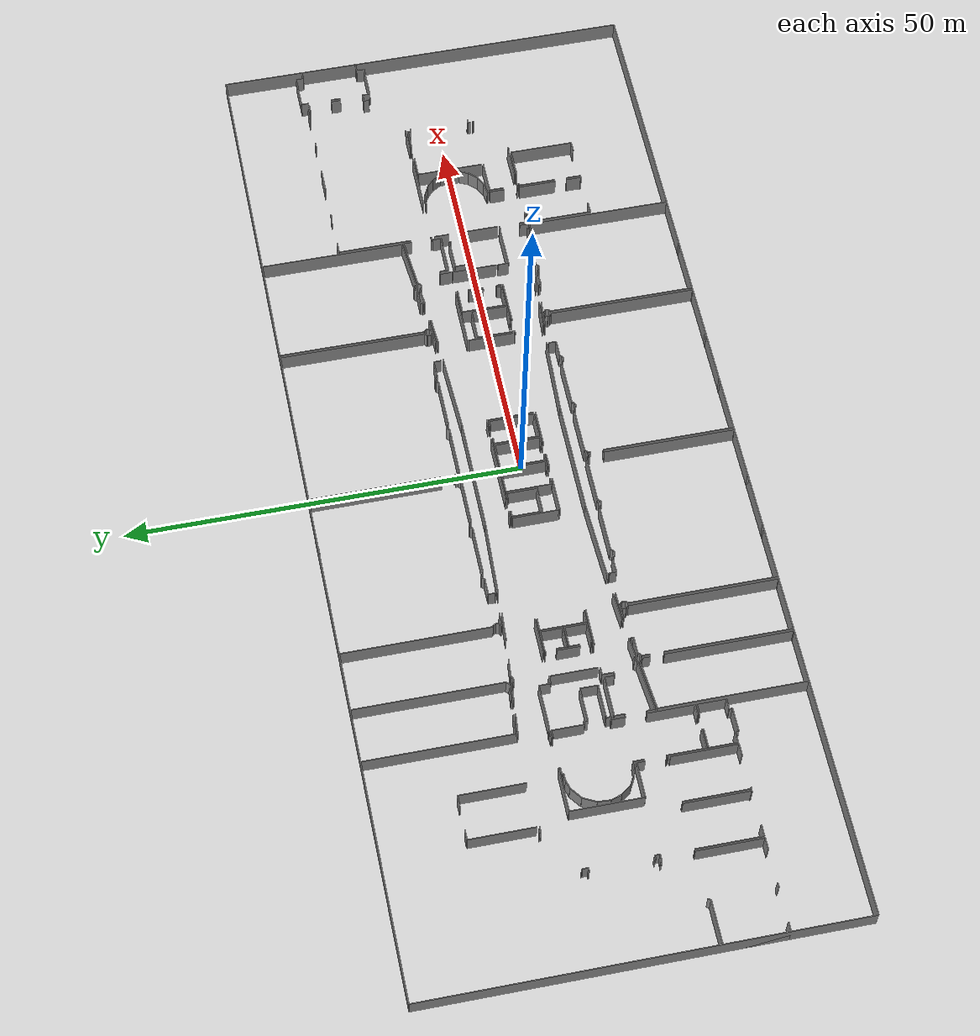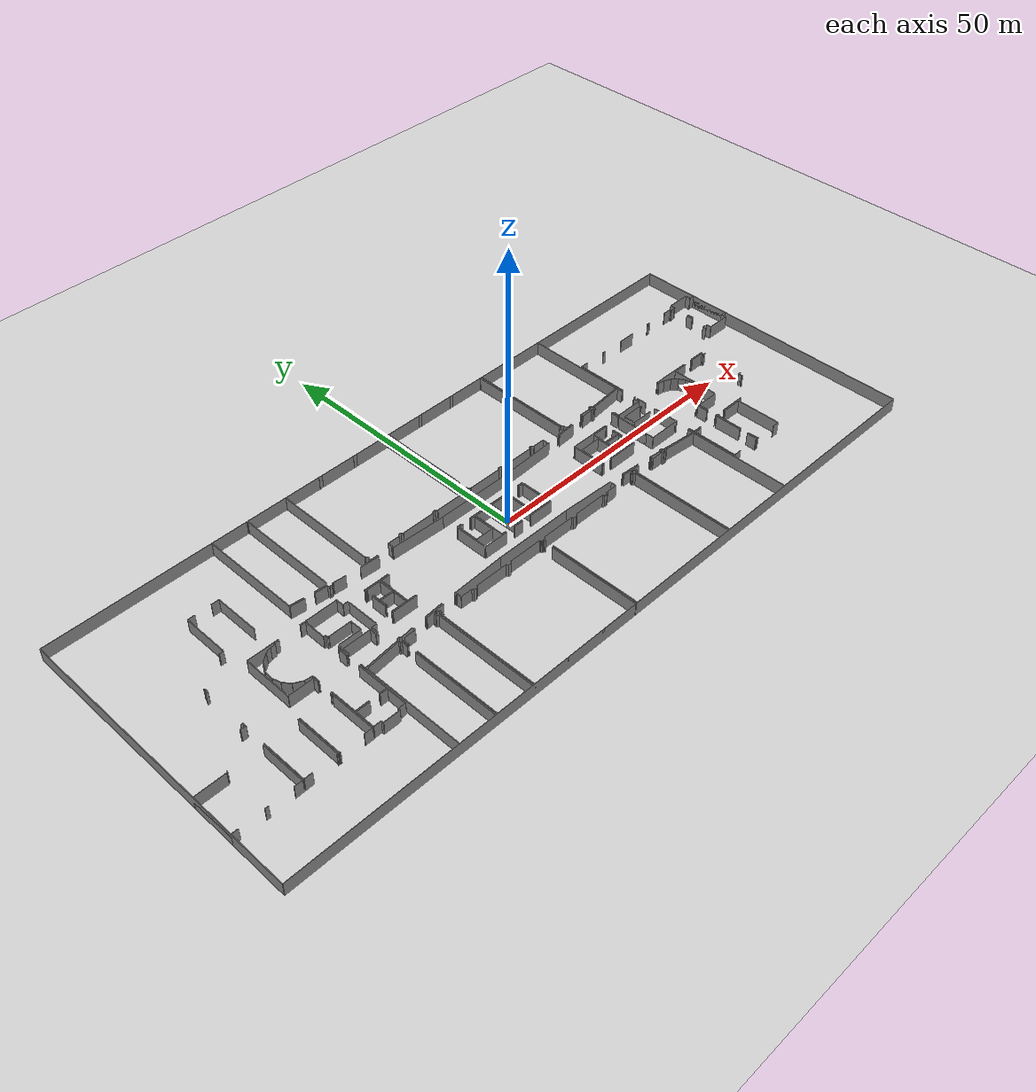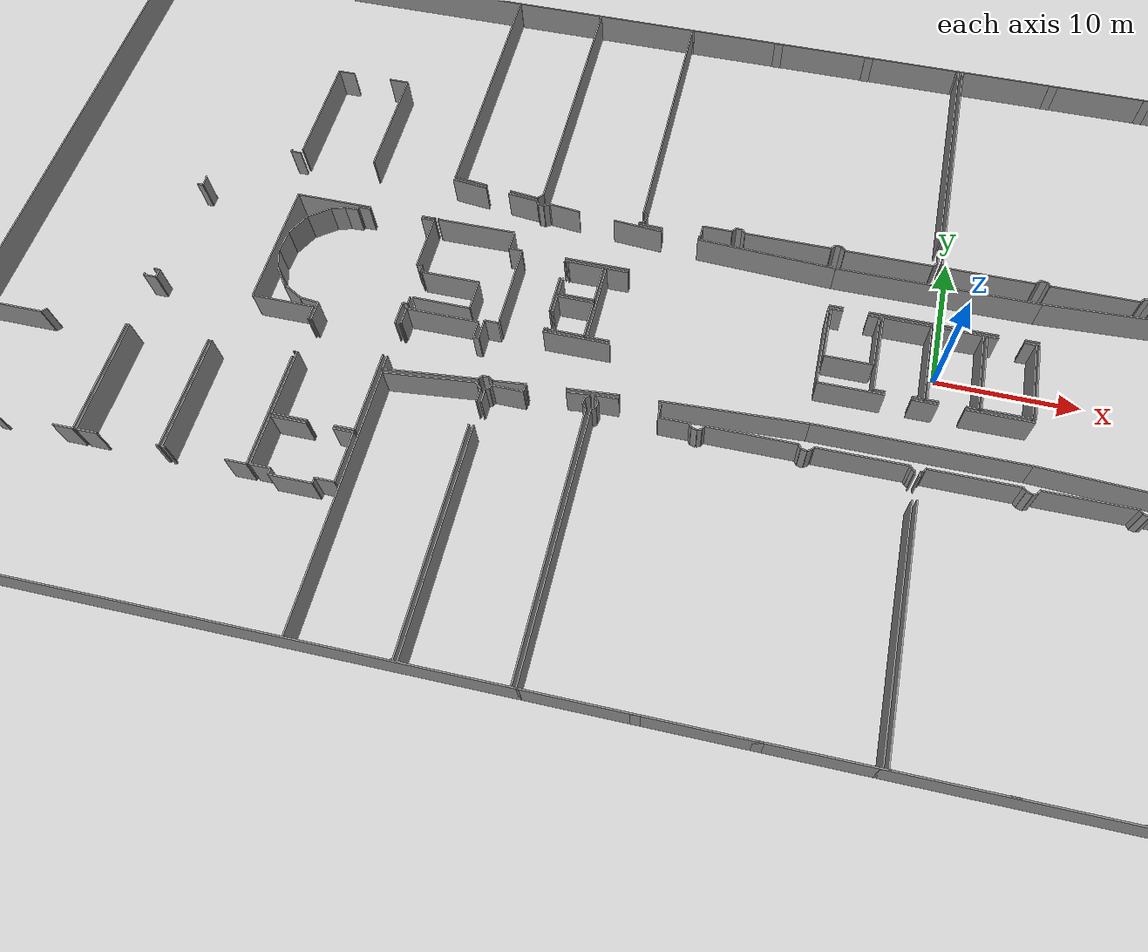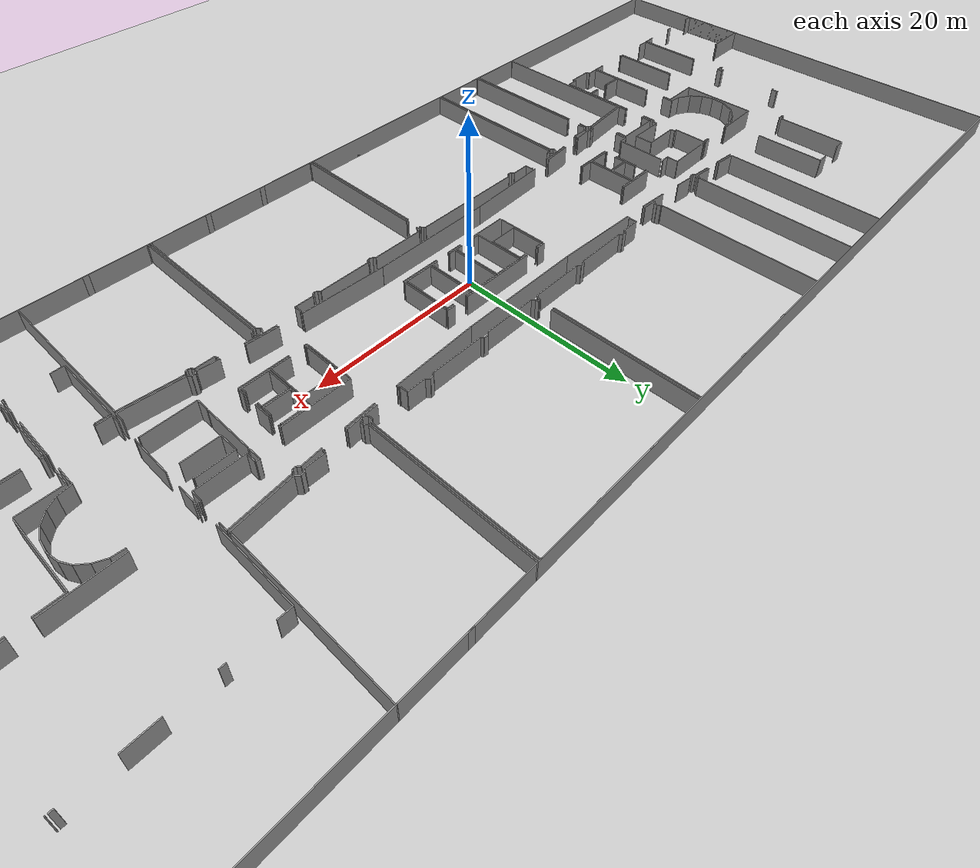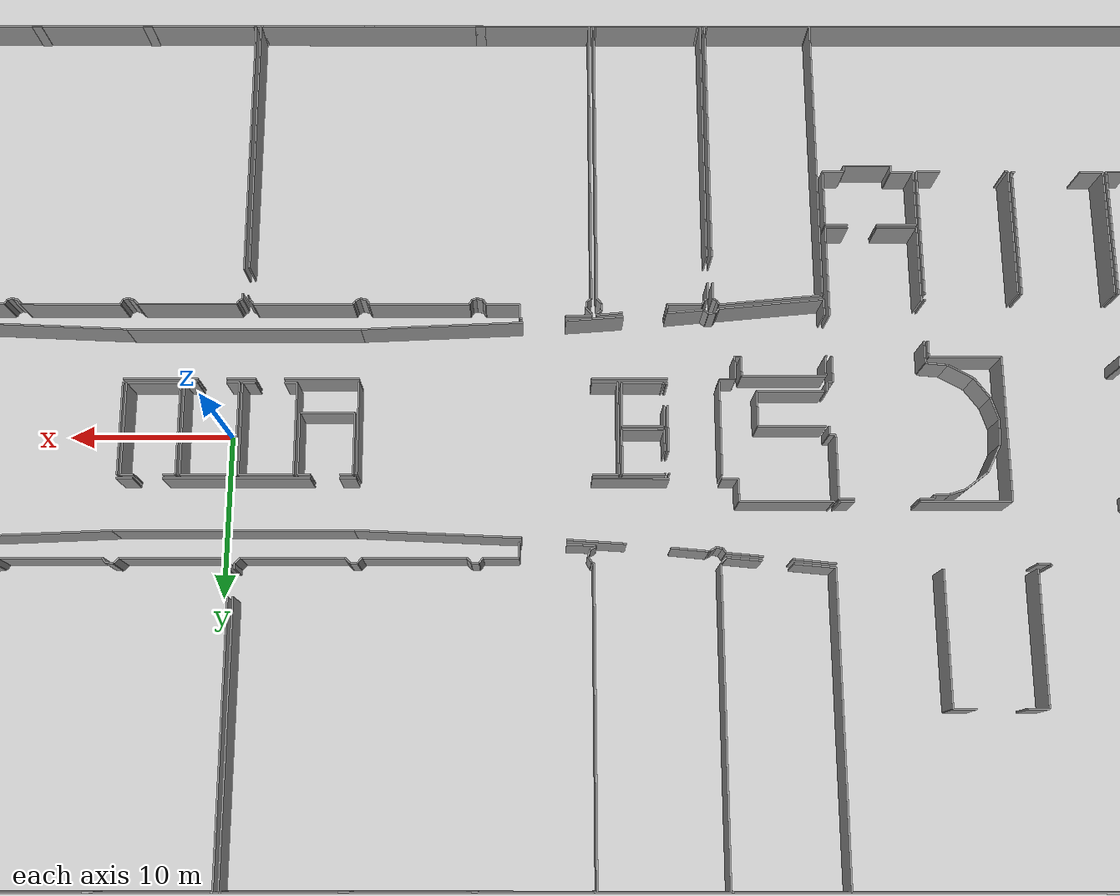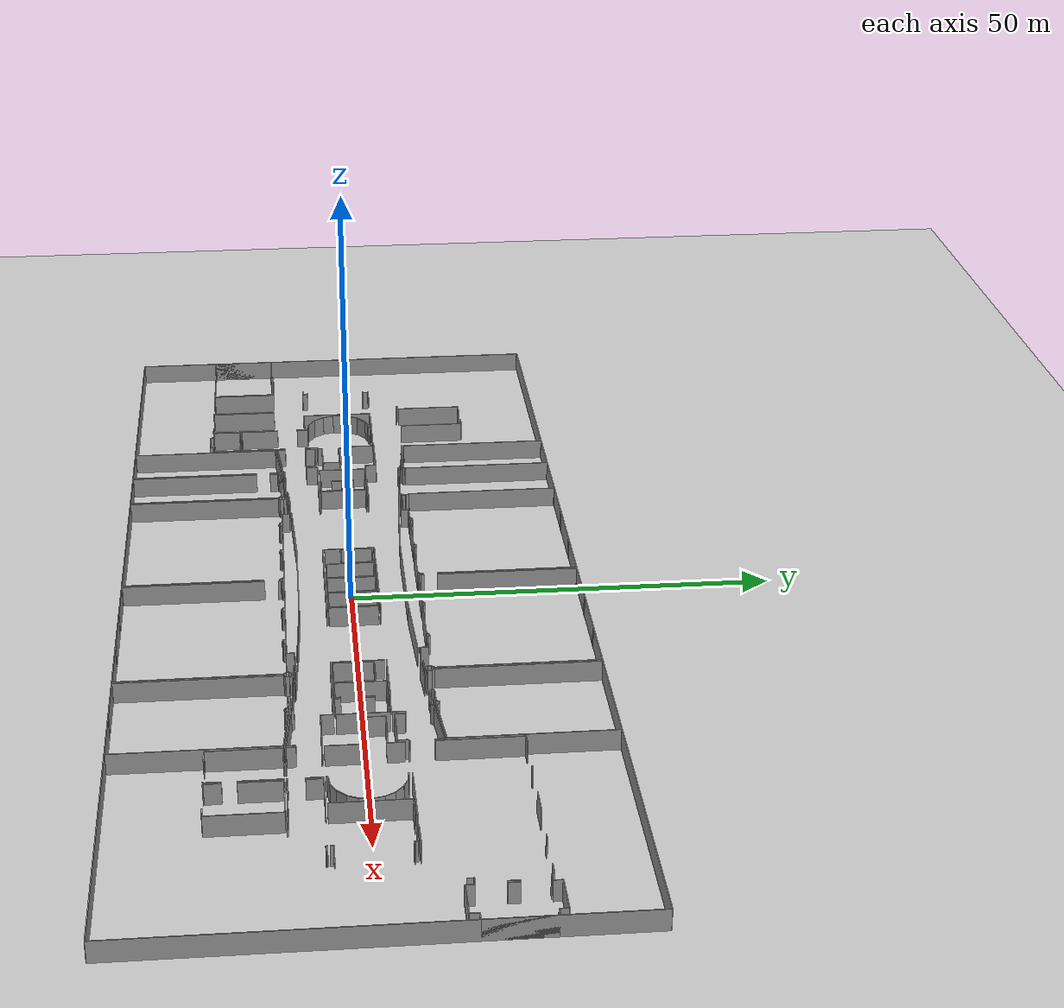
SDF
<sdf version="1.6">
  <world name="default">
    <light name="sun" type="directional">
      <cast_shadows>1</cast_shadows>
      <pose frame="">0 0 10 0 -0 0</pose>
      <diffuse>0.8 0.8 0.8 1</diffuse>
      <specular>0.1 0.1 0.1 1</specular>
      <attenuation>
        <range>1000</range>
        <constant>0.9</constant>
        <linear>0.01</linear>
        <quadratic>0.001</quadratic>
      </attenuation>
      <direction>-0.5 0.5 -1</direction>
    </light>
    <model name="ground_plane">
      <static>1</static>
      <link name="link">
        <collision name="collision">
          <geometry>
            <plane>
              <normal>0 0 1</normal>
              <size>100 100</size>
            </plane>
          </geometry>
          <surface>
            <friction>
              <ode>
                <mu>100</mu>
                <mu2>50</mu2>
              </ode>
              <torsional>
                <ode />
              </torsional>
            </friction>
            <contact>
              <ode />
            </contact>
            <bounce />
          </surface>
          <max_contacts>10</max_contacts>
        </collision>
        <visual name="visual">
          <cast_shadows>0</cast_shadows>
          <geometry>
            <plane>
              <normal>0 0 1</normal>
              <size>100 100</size>
            </plane>
          </geometry>
          <material>
            <script>
              <uri>file://media/materials/scripts/gazebo.material</uri>
              <name>Gazebo/Grey</name>
            </script>
          </material>
        </visual>
        <self_collide>0</self_collide>
        <kinematic>0</kinematic>
        <gravity>1</gravity>
      </link>
    </model>
    <gravity>0 0 -9.8</gravity>
    <magnetic_field>6e-06 2.3e-05 -4.2e-05</magnetic_field>
    <atmosphere type="adiabatic" />
    <physics default="0" name="default_physics" type="ode">
      <max_step_size>0.001</max_step_size>
      <real_time_factor>1</real_time_factor>
      <real_time_update_rate>1000</real_time_update_rate>
    </physics>
    <scene>
      <ambient>0.4 0.4 0.4 1</ambient>
      <background>0.7 0.7 0.7 1</background>
      <shadows>1</shadows>
    </scene>
    <spherical_coordinates>
      <surface_model>EARTH_WGS84</surface_model>
      <latitude_deg>0</latitude_deg>
      <longitude_deg>0</longitude_deg>
      <elevation>0</elevation>
      <heading_deg>0</heading_deg>
    </spherical_coordinates>
  <model name="50041170">
		<static>1</static>
		<link name="Wall_0">
			<collision name="Wall_0_Collision">
				<geometry>
					<box>
						<size>8.18139697249 0.1 2.5</size>
					</box>
				</geometry>
				<pose frame="">4.09069848624 0 1.25 0 0 0</pose>
			</collision>
			<visual name="Wall_0_Visual">
				<pose frame="">4.09069848624 0 1.25 0 0 0</pose>
				<geometry>
					<box>
						<size>8.18139697249 0.1 2.5</size>
					</box>
				</geometry>
				<material>
					<script>
						<uri>file://media/materials/scripts/gazebo.material</uri>
						<name>Gazebo/Grey</name>
					</script>
					<ambient>1 1 1 1</ambient>
				</material>
			</visual>
			<pose frame="">17.9174256609 -18.3893878328 0 0 0 1.57079632679</pose>
		</link>
		<link name="Wall_1">
			<collision name="Wall_1_Collision">
				<geometry>
					<box>
						<size>1.25771952651 0.1 2.5</size>
					</box>
				</geometry>
				<pose frame="">0.628859763257 0 1.25 0 0 0</pose>
			</collision>
			<visual name="Wall_1_Visual">
				<pose frame="">0.628859763257 0 1.25 0 0 0</pose>
				<geometry>
					<box>
						<size>1.25771952651 0.1 2.5</size>
					</box>
				</geometry>
				<material>
					<script>
						<uri>file://media/materials/scripts/gazebo.material</uri>
						<name>Gazebo/Grey</name>
					</script>
					<ambient>1 1 1 1</ambient>
				</material>
			</visual>
			<pose frame="">17.9174256609 -10.2079908603 0 0 0 0.0</pose>
		</link>
		<link name="Wall_2">
			<collision name="Wall_2_Collision">
				<geometry>
					<box>
						<size>1.41918695059 0.1 2.5</size>
					</box>
				</geometry>
				<pose frame="">0.709593475294 0 1.25 0 0 0</pose>
			</collision>
			<visual name="Wall_2_Visual">
				<pose frame="">0.709593475294 0 1.25 0 0 0</pose>
				<geometry>
					<box>
						<size>1.41918695059 0.1 2.5</size>
					</box>
				</geometry>
				<material>
					<script>
						<uri>file://media/materials/scripts/gazebo.material</uri>
						<name>Gazebo/Grey</name>
					</script>
					<ambient>1 1 1 1</ambient>
				</material>
			</visual>
			<pose frame="">22.0923487036 -10.2079908603 0 0 0 0.0</pose>
		</link>
		<link name="Wall_3">
			<collision name="Wall_3_Collision">
				<geometry>
					<box>
						<size>8.18140179789 0.1 2.5</size>
					</box>
				</geometry>
				<pose frame="">4.09070089895 0 1.25 0 0 0</pose>
			</collision>
			<visual name="Wall_3_Visual">
				<pose frame="">4.09070089895 0 1.25 0 0 0</pose>
				<geometry>
					<box>
						<size>8.18140179789 0.1 2.5</size>
					</box>
				</geometry>
				<material>
					<script>
						<uri>file://media/materials/scripts/gazebo.material</uri>
						<name>Gazebo/Grey</name>
					</script>
					<ambient>1 1 1 1</ambient>
				</material>
			</visual>
			<pose frame="">23.5115356542 -10.2079908603 0 0 0 -1.56971023081</pose>
		</link>
		<link name="Wall_4">
			<collision name="Wall_4_Collision">
				<geometry>
					<box>
						<size>0.164513979245 0.1 2.5</size>
					</box>
				</geometry>
				<pose frame="">0.0822569896227 0 1.25 0 0 0</pose>
			</collision>
			<visual name="Wall_4_Visual">
				<pose frame="">0.0822569896227 0 1.25 0 0 0</pose>
				<geometry>
					<box>
						<size>0.164513979245 0.1 2.5</size>
					</box>
				</geometry>
				<material>
					<script>
						<uri>file://media/materials/scripts/gazebo.material</uri>
						<name>Gazebo/Grey</name>
					</script>
					<ambient>1 1 1 1</ambient>
				</material>
			</visual>
			<pose frame="">10.9759766431 -31.3112246517 0 0 0 -1.57079632679</pose>
		</link>
		<link name="Wall_5">
			<collision name="Wall_5_Collision">
				<geometry>
					<box>
						<size>0.927422170036 0.1 2.5</size>
					</box>
				</geometry>
				<pose frame="">0.463711085018 0 1.25 0 0 0</pose>
			</collision>
			<visual name="Wall_5_Visual">
				<pose frame="">0.463711085018 0 1.25 0 0 0</pose>
				<geometry>
					<box>
						<size>0.927422170036 0.1 2.5</size>
					</box>
				</geometry>
				<material>
					<script>
						<uri>file://media/materials/scripts/gazebo.material</uri>
						<name>Gazebo/Grey</name>
					</script>
					<ambient>1 1 1 1</ambient>
				</material>
			</visual>
			<pose frame="">10.9759766431 -31.475738631 0 0 0 0.0</pose>
		</link>
		<link name="Wall_6">
			<collision name="Wall_6_Collision">
				<geometry>
					<box>
						<size>0.631017739837 0.1 2.5</size>
					</box>
				</geometry>
				<pose frame="">0.315508869918 0 1.25 0 0 0</pose>
			</collision>
			<visual name="Wall_6_Visual">
				<pose frame="">0.315508869918 0 1.25 0 0 0</pose>
				<geometry>
					<box>
						<size>0.631017739837 0.1 2.5</size>
					</box>
				</geometry>
				<material>
					<script>
						<uri>file://media/materials/scripts/gazebo.material</uri>
						<name>Gazebo/Grey</name>
					</script>
					<ambient>1 1 1 1</ambient>
				</material>
			</visual>
			<pose frame="">11.9033988131 -31.475738631 0 0 0 1.57079632679</pose>
		</link>
		<link name="Wall_7">
			<collision name="Wall_7_Collision">
				<geometry>
					<box>
						<size>0.428041001555 0.1 2.5</size>
					</box>
				</geometry>
				<pose frame="">0.214020500778 0 1.25 0 0 0</pose>
			</collision>
			<visual name="Wall_7_Visual">
				<pose frame="">0.214020500778 0 1.25 0 0 0</pose>
				<geometry>
					<box>
						<size>0.428041001555 0.1 2.5</size>
					</box>
				</geometry>
				<material>
					<script>
						<uri>file://media/materials/scripts/gazebo.material</uri>
						<name>Gazebo/Grey</name>
					</script>
					<ambient>1 1 1 1</ambient>
				</material>
			</visual>
			<pose frame="">11.9033988131 -30.8447208911 0 0 0 3.14159265359</pose>
		</link>
		<link name="Wall_8">
			<collision name="Wall_8_Collision">
				<geometry>
					<box>
						<size>0.416108660468 0.1 2.5</size>
					</box>
				</geometry>
				<pose frame="">0.208054330234 0 1.25 0 0 0</pose>
			</collision>
			<visual name="Wall_8_Visual">
				<pose frame="">0.208054330234 0 1.25 0 0 0</pose>
				<geometry>
					<box>
						<size>0.416108660468 0.1 2.5</size>
					</box>
				</geometry>
				<material>
					<script>
						<uri>file://media/materials/scripts/gazebo.material</uri>
						<name>Gazebo/Grey</name>
					</script>
					<ambient>1 1 1 1</ambient>
				</material>
			</visual>
			<pose frame="">11.4753578116 -23.0832407731 0 0 0 0.0</pose>
		</link>
		<link name="Wall_9">
			<collision name="Wall_9_Collision">
				<geometry>
					<box>
						<size>0.699692170988 0.1 2.5</size>
					</box>
				</geometry>
				<pose frame="">0.349846085494 0 1.25 0 0 0</pose>
			</collision>
			<visual name="Wall_9_Visual">
				<pose frame="">0.349846085494 0 1.25 0 0 0</pose>
				<geometry>
					<box>
						<size>0.699692170988 0.1 2.5</size>
					</box>
				</geometry>
				<material>
					<script>
						<uri>file://media/materials/scripts/gazebo.material</uri>
						<name>Gazebo/Grey</name>
					</script>
					<ambient>1 1 1 1</ambient>
				</material>
			</visual>
			<pose frame="">11.891466472 -23.0832407731 0 0 0 1.57079632679</pose>
		</link>
		<link name="Wall_10">
			<collision name="Wall_10_Collision">
				<geometry>
					<box>
						<size>0.157453764458 0.1 2.5</size>
					</box>
				</geometry>
				<pose frame="">0.078726882229 0 1.25 0 0 0</pose>
			</collision>
			<visual name="Wall_10_Visual">
				<pose frame="">0.078726882229 0 1.25 0 0 0</pose>
				<geometry>
					<box>
						<size>0.157453764458 0.1 2.5</size>
					</box>
				</geometry>
				<material>
					<script>
						<uri>file://media/materials/scripts/gazebo.material</uri>
						<name>Gazebo/Grey</name>
					</script>
					<ambient>1 1 1 1</ambient>
				</material>
			</visual>
			<pose frame="">11.891466472 -22.3835486021 0 0 0 2.36987664662</pose>
		</link>
		<link name="Wall_11">
			<collision name="Wall_11_Collision">
				<geometry>
					<box>
						<size>0.176827139729 0.1 2.5</size>
					</box>
				</geometry>
				<pose frame="">0.0884135698645 0 1.25 0 0 0</pose>
			</collision>
			<visual name="Wall_11_Visual">
				<pose frame="">0.0884135698645 0 1.25 0 0 0</pose>
				<geometry>
					<box>
						<size>0.176827139729 0.1 2.5</size>
					</box>
				</geometry>
				<material>
					<script>
						<uri>file://media/materials/scripts/gazebo.material</uri>
						<name>Gazebo/Grey</name>
					</script>
					<ambient>1 1 1 1</ambient>
				</material>
			</visual>
			<pose frame="">17.1300180889 -18.517977849 0 0 0 -1.57079632679</pose>
		</link>
		<link name="Wall_12">
			<collision name="Wall_12_Collision">
				<geometry>
					<box>
						<size>0.750595030307 0.1 2.5</size>
					</box>
				</geometry>
				<pose frame="">0.375297515153 0 1.25 0 0 0</pose>
			</collision>
			<visual name="Wall_12_Visual">
				<pose frame="">0.375297515153 0 1.25 0 0 0</pose>
				<geometry>
					<box>
						<size>0.750595030307 0.1 2.5</size>
					</box>
				</geometry>
				<material>
					<script>
						<uri>file://media/materials/scripts/gazebo.material</uri>
						<name>Gazebo/Grey</name>
					</script>
					<ambient>1 1 1 1</ambient>
				</material>
			</visual>
			<pose frame="">17.1300180889 -18.6948049887 0 0 0 0.0</pose>
		</link>
		<link name="Wall_13">
			<collision name="Wall_13_Collision">
				<geometry>
					<box>
						<size>0.108914347371 0.1 2.5</size>
					</box>
				</geometry>
				<pose frame="">0.0544571736854 0 1.25 0 0 0</pose>
			</collision>
			<visual name="Wall_13_Visual">
				<pose frame="">0.0544571736854 0 1.25 0 0 0</pose>
				<geometry>
					<box>
						<size>0.108914347371 0.1 2.5</size>
					</box>
				</geometry>
				<material>
					<script>
						<uri>file://media/materials/scripts/gazebo.material</uri>
						<name>Gazebo/Grey</name>
					</script>
					<ambient>1 1 1 1</ambient>
				</material>
			</visual>
			<pose frame="">29.481387452 -22.3375963949 0 0 0 -1.57079632679</pose>
		</link>
		<link name="Wall_14">
			<collision name="Wall_14_Collision">
				<geometry>
					<box>
						<size>0.909396718606 0.1 2.5</size>
					</box>
				</geometry>
				<pose frame="">0.454698359303 0 1.25 0 0 0</pose>
			</collision>
			<visual name="Wall_14_Visual">
				<pose frame="">0.454698359303 0 1.25 0 0 0</pose>
				<geometry>
					<box>
						<size>0.909396718606 0.1 2.5</size>
					</box>
				</geometry>
				<material>
					<script>
						<uri>file://media/materials/scripts/gazebo.material</uri>
						<name>Gazebo/Grey</name>
					</script>
					<ambient>1 1 1 1</ambient>
				</material>
			</visual>
			<pose frame="">29.481387452 -22.4465107423 0 0 0 3.14159265359</pose>
		</link>
		<link name="Wall_15">
			<collision name="Wall_15_Collision">
				<geometry>
					<box>
						<size>5.53736790327 0.1 2.5</size>
					</box>
				</geometry>
				<pose frame="">2.76868395164 0 1.25 0 0 0</pose>
			</collision>
			<visual name="Wall_15_Visual">
				<pose frame="">2.76868395164 0 1.25 0 0 0</pose>
				<geometry>
					<box>
						<size>5.53736790327 0.1 2.5</size>
					</box>
				</geometry>
				<material>
					<script>
						<uri>file://media/materials/scripts/gazebo.material</uri>
						<name>Gazebo/Grey</name>
					</script>
					<ambient>1 1 1 1</ambient>
				</material>
			</visual>
			<pose frame="">24.6410459839 -22.4465107423 0 0 0 3.14159265359</pose>
		</link>
		<link name="Wall_16">
			<collision name="Wall_16_Collision">
				<geometry>
					<box>
						<size>9.03938307258 0.1 2.5</size>
					</box>
				</geometry>
				<pose frame="">4.51969153629 0 1.25 0 0 0</pose>
			</collision>
			<visual name="Wall_16_Visual">
				<pose frame="">4.51969153629 0 1.25 0 0 0</pose>
				<geometry>
					<box>
						<size>9.03938307258 0.1 2.5</size>
					</box>
				</geometry>
				<material>
					<script>
						<uri>file://media/materials/scripts/gazebo.material</uri>
						<name>Gazebo/Grey</name>
					</script>
					<ambient>1 1 1 1</ambient>
				</material>
			</visual>
			<pose frame="">19.1036780807 -22.4465107423 0 0 0 -1.57079632679</pose>
		</link>
		<link name="Wall_17">
			<collision name="Wall_17_Collision">
				<geometry>
					<box>
						<size>4.44517787439 0.1 2.5</size>
					</box>
				</geometry>
				<pose frame="">2.2225889372 0 1.25 0 0 0</pose>
			</collision>
			<visual name="Wall_17_Visual">
				<pose frame="">2.2225889372 0 1.25 0 0 0</pose>
				<geometry>
					<box>
						<size>4.44517787439 0.1 2.5</size>
					</box>
				</geometry>
				<material>
					<script>
						<uri>file://media/materials/scripts/gazebo.material</uri>
						<name>Gazebo/Grey</name>
					</script>
					<ambient>1 1 1 1</ambient>
				</material>
			</visual>
			<pose frame="">19.1036780807 -31.4858938149 0 0 0 0.0</pose>
		</link>
		<link name="Wall_18">
			<collision name="Wall_18_Collision">
				<geometry>
					<box>
						<size>1.03506711942 0.1 2.5</size>
					</box>
				</geometry>
				<pose frame="">0.517533559709 0 1.25 0 0 0</pose>
			</collision>
			<visual name="Wall_18_Visual">
				<pose frame="">0.517533559709 0 1.25 0 0 0</pose>
				<geometry>
					<box>
						<size>1.03506711942 0.1 2.5</size>
					</box>
				</geometry>
				<material>
					<script>
						<uri>file://media/materials/scripts/gazebo.material</uri>
						<name>Gazebo/Grey</name>
					</script>
					<ambient>1 1 1 1</ambient>
				</material>
			</visual>
			<pose frame="">23.5488559551 -31.4858938149 0 0 0 -1.57079632679</pose>
		</link>
		<link name="Wall_19">
			<collision name="Wall_19_Collision">
				<geometry>
					<box>
						<size>0.117773866952 0.1 2.5</size>
					</box>
				</geometry>
				<pose frame="">0.0588869334759 0 1.25 0 0 0</pose>
			</collision>
			<visual name="Wall_19_Visual">
				<pose frame="">0.0588869334759 0 1.25 0 0 0</pose>
				<geometry>
					<box>
						<size>0.117773866952 0.1 2.5</size>
					</box>
				</geometry>
				<material>
					<script>
						<uri>file://media/materials/scripts/gazebo.material</uri>
						<name>Gazebo/Grey</name>
					</script>
					<ambient>1 1 1 1</ambient>
				</material>
			</visual>
			<pose frame="">23.5488559551 -35.1252578465 0 0 0 -1.44109378964</pose>
		</link>
		<link name="Wall_20">
			<collision name="Wall_20_Collision">
				<geometry>
					<box>
						<size>1.41956776999 0.1 2.5</size>
					</box>
				</geometry>
				<pose frame="">0.709783884993 0 1.25 0 0 0</pose>
			</collision>
			<visual name="Wall_20_Visual">
				<pose frame="">0.709783884993 0 1.25 0 0 0</pose>
				<geometry>
					<box>
						<size>1.41956776999 0.1 2.5</size>
					</box>
				</geometry>
				<material>
					<script>
						<uri>file://media/materials/scripts/gazebo.material</uri>
						<name>Gazebo/Grey</name>
					</script>
					<ambient>1 1 1 1</ambient>
				</material>
			</visual>
			<pose frame="">29.5052521342 -39.9559518898 0 0 0 3.14159265359</pose>
		</link>
		<link name="Wall_21">
			<collision name="Wall_21_Collision">
				<geometry>
					<box>
						<size>2.48941639428 0.1 2.5</size>
					</box>
				</geometry>
				<pose frame="">1.24470819714 0 1.25 0 0 0</pose>
			</collision>
			<visual name="Wall_21_Visual">
				<pose frame="">1.24470819714 0 1.25 0 0 0</pose>
				<geometry>
					<box>
						<size>2.48941639428 0.1 2.5</size>
					</box>
				</geometry>
				<material>
					<script>
						<uri>file://media/materials/scripts/gazebo.material</uri>
						<name>Gazebo/Grey</name>
					</script>
					<ambient>1 1 1 1</ambient>
				</material>
			</visual>
			<pose frame="">26.2639713116 -39.9559518898 0 0 0 3.14159265359</pose>
		</link>
		<link name="Wall_22">
			<collision name="Wall_22_Collision">
				<geometry>
					<box>
						<size>4.81558820729 0.1 2.5</size>
					</box>
				</geometry>
				<pose frame="">2.40779410365 0 1.25 0 0 0</pose>
			</collision>
			<visual name="Wall_22_Visual">
				<pose frame="">2.40779410365 0 1.25 0 0 0</pose>
				<geometry>
					<box>
						<size>4.81558820729 0.1 2.5</size>
					</box>
				</geometry>
				<material>
					<script>
						<uri>file://media/materials/scripts/gazebo.material</uri>
						<name>Gazebo/Grey</name>
					</script>
					<ambient>1 1 1 1</ambient>
				</material>
			</visual>
			<pose frame="">23.7745549173 -39.9559518898 0 0 0 1.57079632679</pose>
		</link>
		<link name="Wall_23">
			<collision name="Wall_23_Collision">
				<geometry>
					<box>
						<size>1.39151407445 0.1 2.5</size>
					</box>
				</geometry>
				<pose frame="">0.695757037225 0 1.25 0 0 0</pose>
			</collision>
			<visual name="Wall_23_Visual">
				<pose frame="">0.695757037225 0 1.25 0 0 0</pose>
				<geometry>
					<box>
						<size>1.39151407445 0.1 2.5</size>
					</box>
				</geometry>
				<material>
					<script>
						<uri>file://media/materials/scripts/gazebo.material</uri>
						<name>Gazebo/Grey</name>
					</script>
					<ambient>1 1 1 1</ambient>
				</material>
			</visual>
			<pose frame="">23.7745549173 -32.4965884929 0 0 0 1.57079632679</pose>
		</link>
		<link name="Wall_24">
			<collision name="Wall_24_Collision">
				<geometry>
					<box>
						<size>1.36351133825 0.1 2.5</size>
					</box>
				</geometry>
				<pose frame="">0.681755669124 0 1.25 0 0 0</pose>
			</collision>
			<visual name="Wall_24_Visual">
				<pose frame="">0.681755669124 0 1.25 0 0 0</pose>
				<geometry>
					<box>
						<size>1.36351133825 0.1 2.5</size>
					</box>
				</geometry>
				<material>
					<script>
						<uri>file://media/materials/scripts/gazebo.material</uri>
						<name>Gazebo/Grey</name>
					</script>
					<ambient>1 1 1 1</ambient>
				</material>
			</visual>
			<pose frame="">23.7745549173 -31.1050744185 0 0 0 3.04564796465</pose>
		</link>
		<link name="Wall_25">
			<collision name="Wall_25_Collision">
				<geometry>
					<box>
						<size>1.7511077054 0.1 2.5</size>
					</box>
				</geometry>
				<pose frame="">0.875553852698 0 1.25 0 0 0</pose>
			</collision>
			<visual name="Wall_25_Visual">
				<pose frame="">0.875553852698 0 1.25 0 0 0</pose>
				<geometry>
					<box>
						<size>1.7511077054 0.1 2.5</size>
					</box>
				</geometry>
				<material>
					<script>
						<uri>file://media/materials/scripts/gazebo.material</uri>
						<name>Gazebo/Grey</name>
					</script>
					<ambient>1 1 1 1</ambient>
				</material>
			</visual>
			<pose frame="">22.4173145886 -30.9744533655 0 0 0 2.63526865512</pose>
		</link>
		<link name="Wall_26">
			<collision name="Wall_26_Collision">
				<geometry>
					<box>
						<size>1.56774744888 0.1 2.5</size>
					</box>
				</geometry>
				<pose frame="">0.783873724441 0 1.25 0 0 0</pose>
			</collision>
			<visual name="Wall_26_Visual">
				<pose frame="">0.783873724441 0 1.25 0 0 0</pose>
				<geometry>
					<box>
						<size>1.56774744888 0.1 2.5</size>
					</box>
				</geometry>
				<material>
					<script>
						<uri>file://media/materials/scripts/gazebo.material</uri>
						<name>Gazebo/Grey</name>
					</script>
					<ambient>1 1 1 1</ambient>
				</material>
			</visual>
			<pose frame="">20.8859128558 -30.1252261115 0 0 0 2.20509916548</pose>
		</link>
		<link name="Wall_27">
			<collision name="Wall_27_Collision">
				<geometry>
					<box>
						<size>1.41627703458 0.1 2.5</size>
					</box>
				</geometry>
				<pose frame="">0.70813851729 0 1.25 0 0 0</pose>
			</collision>
			<visual name="Wall_27_Visual">
				<pose frame="">0.70813851729 0 1.25 0 0 0</pose>
				<geometry>
					<box>
						<size>1.41627703458 0.1 2.5</size>
					</box>
				</geometry>
				<material>
					<script>
						<uri>file://media/materials/scripts/gazebo.material</uri>
						<name>Gazebo/Grey</name>
					</script>
					<ambient>1 1 1 1</ambient>
				</material>
			</visual>
			<pose frame="">19.9568404684 -28.8624289931 0 0 0 1.87792124462</pose>
		</link>
		<link name="Wall_28">
			<collision name="Wall_28_Collision">
				<geometry>
					<box>
						<size>1.62845159122 0.1 2.5</size>
					</box>
				</geometry>
				<pose frame="">0.814225795608 0 1.25 0 0 0</pose>
			</collision>
			<visual name="Wall_28_Visual">
				<pose frame="">0.814225795608 0 1.25 0 0 0</pose>
				<geometry>
					<box>
						<size>1.62845159122 0.1 2.5</size>
					</box>
				</geometry>
				<material>
					<script>
						<uri>file://media/materials/scripts/gazebo.material</uri>
						<name>Gazebo/Grey</name>
					</script>
					<ambient>1 1 1 1</ambient>
				</material>
			</visual>
			<pose frame="">19.5286725271 -27.5124242328 0 0 0 1.51284613601</pose>
		</link>
		<link name="Wall_29">
			<collision name="Wall_29_Collision">
				<geometry>
					<box>
						<size>1.83717637317 0.1 2.5</size>
					</box>
				</geometry>
				<pose frame="">0.918588186587 0 1.25 0 0 0</pose>
			</collision>
			<visual name="Wall_29_Visual">
				<pose frame="">0.918588186587 0 1.25 0 0 0</pose>
				<geometry>
					<box>
						<size>1.83717637317 0.1 2.5</size>
					</box>
				</geometry>
				<material>
					<script>
						<uri>file://media/materials/scripts/gazebo.material</uri>
						<name>Gazebo/Grey</name>
					</script>
					<ambient>1 1 1 1</ambient>
				</material>
			</visual>
			<pose frame="">19.6229887976 -25.8867062296 0 0 0 1.10362608234</pose>
		</link>
		<link name="Wall_30">
			<collision name="Wall_30_Collision">
				<geometry>
					<box>
						<size>1.77817270613 0.1 2.5</size>
					</box>
				</geometry>
				<pose frame="">0.889086353064 0 1.25 0 0 0</pose>
			</collision>
			<visual name="Wall_30_Visual">
				<pose frame="">0.889086353064 0 1.25 0 0 0</pose>
				<geometry>
					<box>
						<size>1.77817270613 0.1 2.5</size>
					</box>
				</geometry>
				<material>
					<script>
						<uri>file://media/materials/scripts/gazebo.material</uri>
						<name>Gazebo/Grey</name>
					</script>
					<ambient>1 1 1 1</ambient>
				</material>
			</visual>
			<pose frame="">20.4503824061 -24.2463901495 0 0 0 0.643429721015</pose>
		</link>
		<link name="Wall_31">
			<collision name="Wall_31_Collision">
				<geometry>
					<box>
						<size>1.02394514756 0.1 2.5</size>
					</box>
				</geometry>
				<pose frame="">0.511972573782 0 1.25 0 0 0</pose>
			</collision>
			<visual name="Wall_31_Visual">
				<pose frame="">0.511972573782 0 1.25 0 0 0</pose>
				<geometry>
					<box>
						<size>1.02394514756 0.1 2.5</size>
					</box>
				</geometry>
				<material>
					<script>
						<uri>file://media/materials/scripts/gazebo.material</uri>
						<name>Gazebo/Grey</name>
					</script>
					<ambient>1 1 1 1</ambient>
				</material>
			</visual>
			<pose frame="">21.8729967313 -23.1795880804 0 0 0 0.29497159328</pose>
		</link>
		<link name="Wall_32">
			<collision name="Wall_32_Collision">
				<geometry>
					<box>
						<size>0.921358730388 0.1 2.5</size>
					</box>
				</geometry>
				<pose frame="">0.460679365194 0 1.25 0 0 0</pose>
			</collision>
			<visual name="Wall_32_Visual">
				<pose frame="">0.460679365194 0 1.25 0 0 0</pose>
				<geometry>
					<box>
						<size>0.921358730388 0.1 2.5</size>
					</box>
				</geometry>
				<material>
					<script>
						<uri>file://media/materials/scripts/gazebo.material</uri>
						<name>Gazebo/Grey</name>
					</script>
					<ambient>1 1 1 1</ambient>
				</material>
			</visual>
			<pose frame="">22.8527180984 -22.8819142522 0 0 0 0.0504468852184</pose>
		</link>
		<link name="Wall_33">
			<collision name="Wall_33_Collision">
				<geometry>
					<box>
						<size>0.220748310114 0.1 2.5</size>
					</box>
				</geometry>
				<pose frame="">0.110374155057 0 1.25 0 0 0</pose>
			</collision>
			<visual name="Wall_33_Visual">
				<pose frame="">0.110374155057 0 1.25 0 0 0</pose>
				<geometry>
					<box>
						<size>0.220748310114 0.1 2.5</size>
					</box>
				</geometry>
				<material>
					<script>
						<uri>file://media/materials/scripts/gazebo.material</uri>
						<name>Gazebo/Grey</name>
					</script>
					<ambient>1 1 1 1</ambient>
				</material>
			</visual>
			<pose frame="">23.7729046999 -22.8354542858 0 0 0 1.57079632679</pose>
		</link>
		<link name="Wall_34">
			<collision name="Wall_34_Collision">
				<geometry>
					<box>
						<size>0.868522103392 0.1 2.5</size>
					</box>
				</geometry>
				<pose frame="">0.434261051696 0 1.25 0 0 0</pose>
			</collision>
			<visual name="Wall_34_Visual">
				<pose frame="">0.434261051696 0 1.25 0 0 0</pose>
				<geometry>
					<box>
						<size>0.868522103392 0.1 2.5</size>
					</box>
				</geometry>
				<material>
					<script>
						<uri>file://media/materials/scripts/gazebo.material</uri>
						<name>Gazebo/Grey</name>
					</script>
					<ambient>1 1 1 1</ambient>
				</material>
			</visual>
			<pose frame="">23.7729046999 -22.6147059757 0 0 0 0.0</pose>
		</link>
		<link name="Wall_35">
			<collision name="Wall_35_Collision">
				<geometry>
					<box>
						<size>0.943543524484 0.1 2.5</size>
					</box>
				</geometry>
				<pose frame="">0.471771762242 0 1.25 0 0 0</pose>
			</collision>
			<visual name="Wall_35_Visual">
				<pose frame="">0.471771762242 0 1.25 0 0 0</pose>
				<geometry>
					<box>
						<size>0.943543524484 0.1 2.5</size>
					</box>
				</geometry>
				<material>
					<script>
						<uri>file://media/materials/scripts/gazebo.material</uri>
						<name>Gazebo/Grey</name>
					</script>
					<ambient>1 1 1 1</ambient>
				</material>
			</visual>
			<pose frame="">28.550157088 -22.6147059757 0 0 0 0.0</pose>
		</link>
		<link name="Wall_36">
			<collision name="Wall_36_Collision">
				<geometry>
					<box>
						<size>3.98324394656 0.1 2.5</size>
					</box>
				</geometry>
				<pose frame="">1.99162197328 0 1.25 0 0 0</pose>
			</collision>
			<visual name="Wall_36_Visual">
				<pose frame="">1.99162197328 0 1.25 0 0 0</pose>
				<geometry>
					<box>
						<size>3.98324394656 0.1 2.5</size>
					</box>
				</geometry>
				<material>
					<script>
						<uri>file://media/materials/scripts/gazebo.material</uri>
						<name>Gazebo/Grey</name>
					</script>
					<ambient>1 1 1 1</ambient>
				</material>
			</visual>
			<pose frame="">29.4937006125 -22.6147059757 0 0 0 -1.57079632679</pose>
		</link>
		<link name="Wall_37">
			<collision name="Wall_37_Collision">
				<geometry>
					<box>
						<size>0.370156453302 0.1 2.5</size>
					</box>
				</geometry>
				<pose frame="">0.185078226651 0 1.25 0 0 0</pose>
			</collision>
			<visual name="Wall_37_Visual">
				<pose frame="">0.185078226651 0 1.25 0 0 0</pose>
				<geometry>
					<box>
						<size>0.370156453302 0.1 2.5</size>
					</box>
				</geometry>
				<material>
					<script>
						<uri>file://media/materials/scripts/gazebo.material</uri>
						<name>Gazebo/Grey</name>
					</script>
					<ambient>1 1 1 1</ambient>
				</material>
			</visual>
			<pose frame="">29.4937006125 -26.5979499222 0 0 0 0.0</pose>
		</link>
		<link name="Wall_38">
			<collision name="Wall_38_Collision">
				<geometry>
					<box>
						<size>0.51537558313 0.1 2.5</size>
					</box>
				</geometry>
				<pose frame="">0.257687791565 0 1.25 0 0 0</pose>
			</collision>
			<visual name="Wall_38_Visual">
				<pose frame="">0.257687791565 0 1.25 0 0 0</pose>
				<geometry>
					<box>
						<size>0.51537558313 0.1 2.5</size>
					</box>
				</geometry>
				<material>
					<script>
						<uri>file://media/materials/scripts/gazebo.material</uri>
						<name>Gazebo/Grey</name>
					</script>
					<ambient>1 1 1 1</ambient>
				</material>
			</visual>
			<pose frame="">29.8638570658 -26.5979499222 0 0 0 -1.57079632679</pose>
		</link>
		<link name="Wall_39">
			<collision name="Wall_39_Collision">
				<geometry>
					<box>
						<size>0.580622639713 0.1 2.5</size>
					</box>
				</geometry>
				<pose frame="">0.290311319857 0 1.25 0 0 0</pose>
			</collision>
			<visual name="Wall_39_Visual">
				<pose frame="">0.290311319857 0 1.25 0 0 0</pose>
				<geometry>
					<box>
						<size>0.580622639713 0.1 2.5</size>
					</box>
				</geometry>
				<material>
					<script>
						<uri>file://media/materials/scripts/gazebo.material</uri>
						<name>Gazebo/Grey</name>
					</script>
					<ambient>1 1 1 1</ambient>
				</material>
			</visual>
			<pose frame="">29.8638570658 -29.3124305798 0 0 0 -1.57079632679</pose>
		</link>
		<link name="Wall_40">
			<collision name="Wall_40_Collision">
				<geometry>
					<box>
						<size>0.36292088477 0.1 2.5</size>
					</box>
				</geometry>
				<pose frame="">0.181460442385 0 1.25 0 0 0</pose>
			</collision>
			<visual name="Wall_40_Visual">
				<pose frame="">0.181460442385 0 1.25 0 0 0</pose>
				<geometry>
					<box>
						<size>0.36292088477 0.1 2.5</size>
					</box>
				</geometry>
				<material>
					<script>
						<uri>file://media/materials/scripts/gazebo.material</uri>
						<name>Gazebo/Grey</name>
					</script>
					<ambient>1 1 1 1</ambient>
				</material>
			</visual>
			<pose frame="">29.8638570658 -29.8930532195 0 0 0 3.14159265359</pose>
		</link>
		<link name="Wall_41">
			<collision name="Wall_41_Collision">
				<geometry>
					<box>
						<size>1.66202278569 0.1 2.5</size>
					</box>
				</geometry>
				<pose frame="">0.831011392847 0 1.25 0 0 0</pose>
			</collision>
			<visual name="Wall_41_Visual">
				<pose frame="">0.831011392847 0 1.25 0 0 0</pose>
				<geometry>
					<box>
						<size>1.66202278569 0.1 2.5</size>
					</box>
				</geometry>
				<material>
					<script>
						<uri>file://media/materials/scripts/gazebo.material</uri>
						<name>Gazebo/Grey</name>
					</script>
					<ambient>1 1 1 1</ambient>
				</material>
			</visual>
			<pose frame="">29.500936181 -29.8930532195 0 0 0 -1.57079632679</pose>
		</link>
		<link name="Wall_42">
			<collision name="Wall_42_Collision">
				<geometry>
					<box>
						<size>5.80038877209 0.1 2.5</size>
					</box>
				</geometry>
				<pose frame="">2.90019438605 0 1.25 0 0 0</pose>
			</collision>
			<visual name="Wall_42_Visual">
				<pose frame="">2.90019438605 0 1.25 0 0 0</pose>
				<geometry>
					<box>
						<size>5.80038877209 0.1 2.5</size>
					</box>
				</geometry>
				<material>
					<script>
						<uri>file://media/materials/scripts/gazebo.material</uri>
						<name>Gazebo/Grey</name>
					</script>
					<ambient>1 1 1 1</ambient>
				</material>
			</visual>
			<pose frame="">29.500936181 -34.1555647234 0 0 0 -1.57005224675</pose>
		</link>
		<link name="Wall_43">
			<collision name="Wall_43_Collision">
				<geometry>
					<box>
						<size>1.4497794421 0.1 2.5</size>
					</box>
				</geometry>
				<pose frame="">0.72488972105 0 1.25 0 0 0</pose>
			</collision>
			<visual name="Wall_43_Visual">
				<pose frame="">0.72488972105 0 1.25 0 0 0</pose>
				<geometry>
					<box>
						<size>1.4497794421 0.1 2.5</size>
					</box>
				</geometry>
				<material>
					<script>
						<uri>file://media/materials/scripts/gazebo.material</uri>
						<name>Gazebo/Grey</name>
					</script>
					<ambient>1 1 1 1</ambient>
				</material>
			</visual>
			<pose frame="">11.536923614 -43.7473898004 0 0 0 3.14159265359</pose>
		</link>
		<link name="Wall_44">
			<collision name="Wall_44_Collision">
				<geometry>
					<box>
						<size>0.62010091714 0.1 2.5</size>
					</box>
				</geometry>
				<pose frame="">0.31005045857 0 1.25 0 0 0</pose>
			</collision>
			<visual name="Wall_44_Visual">
				<pose frame="">0.31005045857 0 1.25 0 0 0</pose>
				<geometry>
					<box>
						<size>0.62010091714 0.1 2.5</size>
					</box>
				</geometry>
				<material>
					<script>
						<uri>file://media/materials/scripts/gazebo.material</uri>
						<name>Gazebo/Grey</name>
					</script>
					<ambient>1 1 1 1</ambient>
				</material>
			</visual>
			<pose frame="">5.95449208213 -43.7473898004 0 0 0 3.14159265359</pose>
		</link>
		<link name="Wall_45">
			<collision name="Wall_45_Collision">
				<geometry>
					<box>
						<size>1.15807178446 0.1 2.5</size>
					</box>
				</geometry>
				<pose frame="">0.579035892228 0 1.25 0 0 0</pose>
			</collision>
			<visual name="Wall_45_Visual">
				<pose frame="">0.579035892228 0 1.25 0 0 0</pose>
				<geometry>
					<box>
						<size>1.15807178446 0.1 2.5</size>
					</box>
				</geometry>
				<material>
					<script>
						<uri>file://media/materials/scripts/gazebo.material</uri>
						<name>Gazebo/Grey</name>
					</script>
					<ambient>1 1 1 1</ambient>
				</material>
			</visual>
			<pose frame="">1.15807178446 -43.7473898004 0 0 0 3.14159265359</pose>
		</link>
		<link name="Wall_46">
			<collision name="Wall_46_Collision">
				<geometry>
					<box>
						<size>7.91456951541 0.1 2.5</size>
					</box>
				</geometry>
				<pose frame="">3.9572847577 0 1.25 0 0 0</pose>
			</collision>
			<visual name="Wall_46_Visual">
				<pose frame="">3.9572847577 0 1.25 0 0 0</pose>
				<geometry>
					<box>
						<size>7.91456951541 0.1 2.5</size>
					</box>
				</geometry>
				<material>
					<script>
						<uri>file://media/materials/scripts/gazebo.material</uri>
						<name>Gazebo/Grey</name>
					</script>
					<ambient>1 1 1 1</ambient>
				</material>
			</visual>
			<pose frame="">0.0 -43.7473898004 0 0 0 1.57079632679</pose>
		</link>
		<link name="Wall_47">
			<collision name="Wall_47_Collision">
				<geometry>
					<box>
						<size>5.35635175018 0.1 2.5</size>
					</box>
				</geometry>
				<pose frame="">2.67817587509 0 1.25 0 0 0</pose>
			</collision>
			<visual name="Wall_47_Visual">
				<pose frame="">2.67817587509 0 1.25 0 0 0</pose>
				<geometry>
					<box>
						<size>5.35635175018 0.1 2.5</size>
					</box>
				</geometry>
				<material>
					<script>
						<uri>file://media/materials/scripts/gazebo.material</uri>
						<name>Gazebo/Grey</name>
					</script>
					<ambient>1 1 1 1</ambient>
				</material>
			</visual>
			<pose frame="">0.0 -35.832820285 0 0 0 0.0</pose>
		</link>
		<link name="Wall_48">
			<collision name="Wall_48_Collision">
				<geometry>
					<box>
						<size>0.426449809548 0.1 2.5</size>
					</box>
				</geometry>
				<pose frame="">0.213224904774 0 1.25 0 0 0</pose>
			</collision>
			<visual name="Wall_48_Visual">
				<pose frame="">0.213224904774 0 1.25 0 0 0</pose>
				<geometry>
					<box>
						<size>0.426449809548 0.1 2.5</size>
					</box>
				</geometry>
				<material>
					<script>
						<uri>file://media/materials/scripts/gazebo.material</uri>
						<name>Gazebo/Grey</name>
					</script>
					<ambient>1 1 1 1</ambient>
				</material>
			</visual>
			<pose frame="">5.35635175018 -35.832820285 0 0 0 0.78476671747</pose>
		</link>
		<link name="Wall_49">
			<collision name="Wall_49_Collision">
				<geometry>
					<box>
						<size>8.21593026193 0.1 2.5</size>
					</box>
				</geometry>
				<pose frame="">4.10796513096 0 1.25 0 0 0</pose>
			</collision>
			<visual name="Wall_49_Visual">
				<pose frame="">4.10796513096 0 1.25 0 0 0</pose>
				<geometry>
					<box>
						<size>8.21593026193 0.1 2.5</size>
					</box>
				</geometry>
				<material>
					<script>
						<uri>file://media/materials/scripts/gazebo.material</uri>
						<name>Gazebo/Grey</name>
					</script>
					<ambient>1 1 1 1</ambient>
				</material>
			</visual>
			<pose frame="">11.5272761893 -35.5314652026 0 0 0 -1.56962209252</pose>
		</link>
		<link name="Wall_50">
			<collision name="Wall_50_Collision">
				<geometry>
					<box>
						<size>0.197645266732 0.1 2.5</size>
					</box>
				</geometry>
				<pose frame="">0.0988226333661 0 1.25 0 0 0</pose>
			</collision>
			<visual name="Wall_50_Visual">
				<pose frame="">0.0988226333661 0 1.25 0 0 0</pose>
				<geometry>
					<box>
						<size>0.197645266732 0.1 2.5</size>
					</box>
				</geometry>
				<material>
					<script>
						<uri>file://media/materials/scripts/gazebo.material</uri>
						<name>Gazebo/Grey</name>
					</script>
					<ambient>1 1 1 1</ambient>
				</material>
			</visual>
			<pose frame="">17.5231506458 -43.7303798673 0 0 0 3.14159265359</pose>
		</link>
		<link name="Wall_51">
			<collision name="Wall_51_Collision">
				<geometry>
					<box>
						<size>1.44889086351 0.1 2.5</size>
					</box>
				</geometry>
				<pose frame="">0.724445431754 0 1.25 0 0 0</pose>
			</collision>
			<visual name="Wall_51_Visual">
				<pose frame="">0.724445431754 0 1.25 0 0 0</pose>
				<geometry>
					<box>
						<size>1.44889086351 0.1 2.5</size>
					</box>
				</geometry>
				<material>
					<script>
						<uri>file://media/materials/scripts/gazebo.material</uri>
						<name>Gazebo/Grey</name>
					</script>
					<ambient>1 1 1 1</ambient>
				</material>
			</visual>
			<pose frame="">13.2096093428 -43.7303798673 0 0 0 3.14159265359</pose>
		</link>
		<link name="Wall_52">
			<collision name="Wall_52_Collision">
				<geometry>
					<box>
						<size>8.19891466472 0.1 2.5</size>
					</box>
				</geometry>
				<pose frame="">4.09945733236 0 1.25 0 0 0</pose>
			</collision>
			<visual name="Wall_52_Visual">
				<pose frame="">4.09945733236 0 1.25 0 0 0</pose>
				<geometry>
					<box>
						<size>8.19891466472 0.1 2.5</size>
					</box>
				</geometry>
				<material>
					<script>
						<uri>file://media/materials/scripts/gazebo.material</uri>
						<name>Gazebo/Grey</name>
					</script>
					<ambient>1 1 1 1</ambient>
				</material>
			</visual>
			<pose frame="">11.7607184793 -43.7303798673 0 0 0 1.57079632679</pose>
		</link>
		<link name="Wall_53">
			<collision name="Wall_53_Collision">
				<geometry>
					<box>
						<size>8.19891527889 0.1 2.5</size>
					</box>
				</geometry>
				<pose frame="">4.09945763945 0 1.25 0 0 0</pose>
			</collision>
			<visual name="Wall_53_Visual">
				<pose frame="">4.09945763945 0 1.25 0 0 0</pose>
				<geometry>
					<box>
						<size>8.19891527889 0.1 2.5</size>
					</box>
				</geometry>
				<material>
					<script>
						<uri>file://media/materials/scripts/gazebo.material</uri>
						<name>Gazebo/Grey</name>
					</script>
					<ambient>1 1 1 1</ambient>
				</material>
			</visual>
			<pose frame="">17.5263241408 -35.5314652026 0 0 0 -1.57118338959</pose>
		</link>
		<link name="Wall_54">
			<collision name="Wall_54_Collision">
				<geometry>
					<box>
						<size>1.48811526134 0.1 2.5</size>
					</box>
				</geometry>
				<pose frame="">0.744057630669 0 1.25 0 0 0</pose>
			</collision>
			<visual name="Wall_54_Visual">
				<pose frame="">0.744057630669 0 1.25 0 0 0</pose>
				<geometry>
					<box>
						<size>1.48811526134 0.1 2.5</size>
					</box>
				</geometry>
				<material>
					<script>
						<uri>file://media/materials/scripts/gazebo.material</uri>
						<name>Gazebo/Grey</name>
					</script>
					<ambient>1 1 1 1</ambient>
				</material>
			</visual>
			<pose frame="">23.554568246 -43.7561486465 0 0 0 3.14159265359</pose>
		</link>
		<link name="Wall_55">
			<collision name="Wall_55_Collision">
				<geometry>
					<box>
						<size>0.203230617879 0.1 2.5</size>
					</box>
				</geometry>
				<pose frame="">0.10161530894 0 1.25 0 0 0</pose>
			</collision>
			<visual name="Wall_55_Visual">
				<pose frame="">0.10161530894 0 1.25 0 0 0</pose>
				<geometry>
					<box>
						<size>0.203230617879 0.1 2.5</size>
					</box>
				</geometry>
				<material>
					<script>
						<uri>file://media/materials/scripts/gazebo.material</uri>
						<name>Gazebo/Grey</name>
					</script>
					<ambient>1 1 1 1</ambient>
				</material>
			</visual>
			<pose frame="">17.9609660119 -43.7561486465 0 0 0 3.14159265359</pose>
		</link>
		<link name="Wall_56">
			<collision name="Wall_56_Collision">
				<geometry>
					<box>
						<size>8.21922503253 0.1 2.5</size>
					</box>
				</geometry>
				<pose frame="">4.10961251626 0 1.25 0 0 0</pose>
			</collision>
			<visual name="Wall_56_Visual">
				<pose frame="">4.10961251626 0 1.25 0 0 0</pose>
				<geometry>
					<box>
						<size>8.21922503253 0.1 2.5</size>
					</box>
				</geometry>
				<material>
					<script>
						<uri>file://media/materials/scripts/gazebo.material</uri>
						<name>Gazebo/Grey</name>
					</script>
					<ambient>1 1 1 1</ambient>
				</material>
			</visual>
			<pose frame="">17.757735394 -43.7561486465 0 0 0 1.57079632679</pose>
		</link>
		<link name="Wall_57">
			<collision name="Wall_57_Collision">
				<geometry>
					<box>
						<size>8.21922511193 0.1 2.5</size>
					</box>
				</geometry>
				<pose frame="">4.10961255596 0 1.25 0 0 0</pose>
			</collision>
			<visual name="Wall_57_Visual">
				<pose frame="">4.10961255596 0 1.25 0 0 0</pose>
				<geometry>
					<box>
						<size>8.21922511193 0.1 2.5</size>
					</box>
				</geometry>
				<material>
					<script>
						<uri>file://media/materials/scripts/gazebo.material</uri>
						<name>Gazebo/Grey</name>
					</script>
					<ambient>1 1 1 1</ambient>
				</material>
			</visual>
			<pose frame="">23.5534257878 -35.536923614 0 0 0 -1.57065732851</pose>
		</link>
		<link name="Wall_58">
			<collision name="Wall_58_Collision">
				<geometry>
					<box>
						<size>2.21725746565 0.1 2.5</size>
					</box>
				</geometry>
				<pose frame="">1.10862873282 0 1.25 0 0 0</pose>
			</collision>
			<visual name="Wall_58_Visual">
				<pose frame="">1.10862873282 0 1.25 0 0 0</pose>
				<geometry>
					<box>
						<size>2.21725746565 0.1 2.5</size>
					</box>
				</geometry>
				<material>
					<script>
						<uri>file://media/materials/scripts/gazebo.material</uri>
						<name>Gazebo/Grey</name>
					</script>
					<ambient>1 1 1 1</ambient>
				</material>
			</visual>
			<pose frame="">34.1700358605 -29.3304560312 0 0 0 1.57079632679</pose>
		</link>
		<link name="Wall_59">
			<collision name="Wall_59_Collision">
				<geometry>
					<box>
						<size>4.13925295928 0.1 2.5</size>
					</box>
				</geometry>
				<pose frame="">2.06962647964 0 1.25 0 0 0</pose>
			</collision>
			<visual name="Wall_59_Visual">
				<pose frame="">2.06962647964 0 1.25 0 0 0</pose>
				<geometry>
					<box>
						<size>4.13925295928 0.1 2.5</size>
					</box>
				</geometry>
				<material>
					<script>
						<uri>file://media/materials/scripts/gazebo.material</uri>
						<name>Gazebo/Grey</name>
					</script>
					<ambient>1 1 1 1</ambient>
				</material>
			</visual>
			<pose frame="">34.1700358605 -27.1131985656 0 0 0 3.14159265359</pose>
		</link>
		<link name="Wall_60">
			<collision name="Wall_60_Collision">
				<geometry>
					<box>
						<size>4.1393488871 0.1 2.5</size>
					</box>
				</geometry>
				<pose frame="">2.06967444355 0 1.25 0 0 0</pose>
			</collision>
			<visual name="Wall_60_Visual">
				<pose frame="">2.06967444355 0 1.25 0 0 0</pose>
				<geometry>
					<box>
						<size>4.1393488871 0.1 2.5</size>
					</box>
				</geometry>
				<material>
					<script>
						<uri>file://media/materials/scripts/gazebo.material</uri>
						<name>Gazebo/Grey</name>
					</script>
					<ambient>1 1 1 1</ambient>
				</material>
			</visual>
			<pose frame="">30.0307829012 -29.3022753959 0 0 0 -0.0068080400556</pose>
		</link>
		<link name="Wall_61">
			<collision name="Wall_61_Collision">
				<geometry>
					<box>
						<size>1.34645044588 0.1 2.5</size>
					</box>
				</geometry>
				<pose frame="">0.673225222938 0 1.25 0 0 0</pose>
			</collision>
			<visual name="Wall_61_Visual">
				<pose frame="">0.673225222938 0 1.25 0 0 0</pose>
				<geometry>
					<box>
						<size>1.34645044588 0.1 2.5</size>
					</box>
				</geometry>
				<material>
					<script>
						<uri>file://media/materials/scripts/gazebo.material</uri>
						<name>Gazebo/Grey</name>
					</script>
					<ambient>1 1 1 1</ambient>
				</material>
			</visual>
			<pose frame="">29.4934467329 -43.7574180445 0 0 0 3.14159265359</pose>
		</link>
		<link name="Wall_62">
			<collision name="Wall_62_Collision">
				<geometry>
					<box>
						<size>0.387801085335 0.1 2.5</size>
					</box>
				</geometry>
				<pose frame="">0.193900542668 0 1.25 0 0 0</pose>
			</collision>
			<visual name="Wall_62_Visual">
				<pose frame="">0.193900542668 0 1.25 0 0 0</pose>
				<geometry>
					<box>
						<size>0.387801085335 0.1 2.5</size>
					</box>
				</geometry>
				<material>
					<script>
						<uri>file://media/materials/scripts/gazebo.material</uri>
						<name>Gazebo/Grey</name>
					</script>
					<ambient>1 1 1 1</ambient>
				</material>
			</visual>
			<pose frame="">28.146996287 -43.7574180445 0 0 0 -1.57079632679</pose>
		</link>
		<link name="Wall_63">
			<collision name="Wall_63_Collision">
				<geometry>
					<box>
						<size>2.98029259624 0.1 2.5</size>
					</box>
				</geometry>
				<pose frame="">1.49014629812 0 1.25 0 0 0</pose>
			</collision>
			<visual name="Wall_63_Visual">
				<pose frame="">1.49014629812 0 1.25 0 0 0</pose>
				<geometry>
					<box>
						<size>2.98029259624 0.1 2.5</size>
					</box>
				</geometry>
				<material>
					<script>
						<uri>file://media/materials/scripts/gazebo.material</uri>
						<name>Gazebo/Grey</name>
					</script>
					<ambient>1 1 1 1</ambient>
				</material>
			</visual>
			<pose frame="">28.146996287 -44.1452191298 0 0 0 3.14159265359</pose>
		</link>
		<link name="Wall_64">
			<collision name="Wall_64_Collision">
				<geometry>
					<box>
						<size>0.430452857732 0.1 2.5</size>
					</box>
				</geometry>
				<pose frame="">0.215226428866 0 1.25 0 0 0</pose>
			</collision>
			<visual name="Wall_64_Visual">
				<pose frame="">0.215226428866 0 1.25 0 0 0</pose>
				<geometry>
					<box>
						<size>0.430452857732 0.1 2.5</size>
					</box>
				</geometry>
				<material>
					<script>
						<uri>file://media/materials/scripts/gazebo.material</uri>
						<name>Gazebo/Grey</name>
					</script>
					<ambient>1 1 1 1</ambient>
				</material>
			</visual>
			<pose frame="">25.1667036908 -44.1452191298 0 0 0 1.57079632679</pose>
		</link>
		<link name="Wall_65">
			<collision name="Wall_65_Collision">
				<geometry>
					<box>
						<size>1.40179619815 0.1 2.5</size>
					</box>
				</geometry>
				<pose frame="">0.700898099077 0 1.25 0 0 0</pose>
			</collision>
			<visual name="Wall_65_Visual">
				<pose frame="">0.700898099077 0 1.25 0 0 0</pose>
				<geometry>
					<box>
						<size>1.40179619815 0.1 2.5</size>
					</box>
				</geometry>
				<material>
					<script>
						<uri>file://media/materials/scripts/gazebo.material</uri>
						<name>Gazebo/Grey</name>
					</script>
					<ambient>1 1 1 1</ambient>
				</material>
			</visual>
			<pose frame="">25.1667036908 -43.7147662721 0 0 0 3.14159265359</pose>
		</link>
		<link name="Wall_66">
			<collision name="Wall_66_Collision">
				<geometry>
					<box>
						<size>3.55723398178 0.1 2.5</size>
					</box>
				</geometry>
				<pose frame="">1.77861699089 0 1.25 0 0 0</pose>
			</collision>
			<visual name="Wall_66_Visual">
				<pose frame="">1.77861699089 0 1.25 0 0 0</pose>
				<geometry>
					<box>
						<size>3.55723398178 0.1 2.5</size>
					</box>
				</geometry>
				<material>
					<script>
						<uri>file://media/materials/scripts/gazebo.material</uri>
						<name>Gazebo/Grey</name>
					</script>
					<ambient>1 1 1 1</ambient>
				</material>
			</visual>
			<pose frame="">23.7649074926 -43.7147662721 0 0 0 1.57079632679</pose>
		</link>
		<link name="Wall_67">
			<collision name="Wall_67_Collision">
				<geometry>
					<box>
						<size>2.50629938752 0.1 2.5</size>
					</box>
				</geometry>
				<pose frame="">1.25314969376 0 1.25 0 0 0</pose>
			</collision>
			<visual name="Wall_67_Visual">
				<pose frame="">1.25314969376 0 1.25 0 0 0</pose>
				<geometry>
					<box>
						<size>2.50629938752 0.1 2.5</size>
					</box>
				</geometry>
				<material>
					<script>
						<uri>file://media/materials/scripts/gazebo.material</uri>
						<name>Gazebo/Grey</name>
					</script>
					<ambient>1 1 1 1</ambient>
				</material>
			</visual>
			<pose frame="">23.7649074926 -40.1575322903 0 0 0 0.0</pose>
		</link>
		<link name="Wall_68">
			<collision name="Wall_68_Collision">
				<geometry>
					<box>
						<size>1.40903176668 0.1 2.5</size>
					</box>
				</geometry>
				<pose frame="">0.704515883342 0 1.25 0 0 0</pose>
			</collision>
			<visual name="Wall_68_Visual">
				<pose frame="">0.704515883342 0 1.25 0 0 0</pose>
				<geometry>
					<box>
						<size>1.40903176668 0.1 2.5</size>
					</box>
				</geometry>
				<material>
					<script>
						<uri>file://media/materials/scripts/gazebo.material</uri>
						<name>Gazebo/Grey</name>
					</script>
					<ambient>1 1 1 1</ambient>
				</material>
			</visual>
			<pose frame="">28.0863190632 -40.1575322903 0 0 0 0.0</pose>
		</link>
		<link name="Wall_69">
			<collision name="Wall_69_Collision">
				<geometry>
					<box>
						<size>3.59988625775 0.1 2.5</size>
					</box>
				</geometry>
				<pose frame="">1.79994312888 0 1.25 0 0 0</pose>
			</collision>
			<visual name="Wall_69_Visual">
				<pose frame="">1.79994312888 0 1.25 0 0 0</pose>
				<geometry>
					<box>
						<size>3.59988625775 0.1 2.5</size>
					</box>
				</geometry>
				<material>
					<script>
						<uri>file://media/materials/scripts/gazebo.material</uri>
						<name>Gazebo/Grey</name>
					</script>
					<ambient>1 1 1 1</ambient>
				</material>
			</visual>
			<pose frame="">29.4953508299 -40.1575322903 0 0 0 -1.57132525936</pose>
		</link>
		<link name="Wall_70">
			<collision name="Wall_70_Collision">
				<geometry>
					<box>
						<size>0.101044079845 0.1 2.5</size>
					</box>
				</geometry>
				<pose frame="">0.0505220399226 0 1.25 0 0 0</pose>
			</collision>
			<visual name="Wall_70_Visual">
				<pose frame="">0.0505220399226 0 1.25 0 0 0</pose>
				<geometry>
					<box>
						<size>0.101044079845 0.1 2.5</size>
					</box>
				</geometry>
				<material>
					<script>
						<uri>file://media/materials/scripts/gazebo.material</uri>
						<name>Gazebo/Grey</name>
					</script>
					<ambient>1 1 1 1</ambient>
				</material>
			</visual>
			<pose frame="">29.7842658119 -22.4673288693 0 0 0 1.57079632679</pose>
		</link>
		<link name="Wall_71">
			<collision name="Wall_71_Collision">
				<geometry>
					<box>
						<size>2.62578556154 0.1 2.5</size>
					</box>
				</geometry>
				<pose frame="">1.31289278077 0 1.25 0 0 0</pose>
			</collision>
			<visual name="Wall_71_Visual">
				<pose frame="">1.31289278077 0 1.25 0 0 0</pose>
				<geometry>
					<box>
						<size>2.62578556154 0.1 2.5</size>
					</box>
				</geometry>
				<material>
					<script>
						<uri>file://media/materials/scripts/gazebo.material</uri>
						<name>Gazebo/Grey</name>
					</script>
					<ambient>1 1 1 1</ambient>
				</material>
			</visual>
			<pose frame="">29.7842658119 -18.6890926978 0 0 0 -0.10189104209</pose>
		</link>
		<link name="Wall_72">
			<collision name="Wall_72_Collision">
				<geometry>
					<box>
						<size>2.22257233107 0.1 2.5</size>
					</box>
				</geometry>
				<pose frame="">1.11128616553 0 1.25 0 0 0</pose>
			</collision>
			<visual name="Wall_72_Visual">
				<pose frame="">1.11128616553 0 1.25 0 0 0</pose>
				<geometry>
					<box>
						<size>2.22257233107 0.1 2.5</size>
					</box>
				</geometry>
				<material>
					<script>
						<uri>file://media/materials/scripts/gazebo.material</uri>
						<name>Gazebo/Grey</name>
					</script>
					<ambient>1 1 1 1</ambient>
				</material>
			</visual>
			<pose frame="">34.13246168 -19.114848783 0 0 0 -0.0949517063428</pose>
		</link>
		<link name="Wall_73">
			<collision name="Wall_73_Collision">
				<geometry>
					<box>
						<size>0.346281394295 0.1 2.5</size>
					</box>
				</geometry>
				<pose frame="">0.173140697147 0 1.25 0 0 0</pose>
			</collision>
			<visual name="Wall_73_Visual">
				<pose frame="">0.173140697147 0 1.25 0 0 0</pose>
				<geometry>
					<box>
						<size>0.346281394295 0.1 2.5</size>
					</box>
				</geometry>
				<material>
					<script>
						<uri>file://media/materials/scripts/gazebo.material</uri>
						<name>Gazebo/Grey</name>
					</script>
					<ambient>1 1 1 1</ambient>
				</material>
			</visual>
			<pose frame="">36.3450223731 -19.325568849 0 0 0 -0.994282795744</pose>
		</link>
		<link name="Wall_74">
			<collision name="Wall_74_Collision">
				<geometry>
					<box>
						<size>0.387981293824 0.1 2.5</size>
					</box>
				</geometry>
				<pose frame="">0.193990646912 0 1.25 0 0 0</pose>
			</collision>
			<visual name="Wall_74_Visual">
				<pose frame="">0.193990646912 0 1.25 0 0 0</pose>
				<geometry>
					<box>
						<size>0.387981293824 0.1 2.5</size>
					</box>
				</geometry>
				<material>
					<script>
						<uri>file://media/materials/scripts/gazebo.material</uri>
						<name>Gazebo/Grey</name>
					</script>
					<ambient>1 1 1 1</ambient>
				</material>
			</visual>
			<pose frame="">36.533781854 -19.6158801688 0 0 0 -0.131578601703</pose>
		</link>
		<link name="Wall_75">
			<collision name="Wall_75_Collision">
				<geometry>
					<box>
						<size>0.400794860855 0.1 2.5</size>
					</box>
				</geometry>
				<pose frame="">0.200397430428 0 1.25 0 0 0</pose>
			</collision>
			<visual name="Wall_75_Visual">
				<pose frame="">0.200397430428 0 1.25 0 0 0</pose>
				<geometry>
					<box>
						<size>0.400794860855 0.1 2.5</size>
					</box>
				</geometry>
				<material>
					<script>
						<uri>file://media/materials/scripts/gazebo.material</uri>
						<name>Gazebo/Grey</name>
					</script>
					<ambient>1 1 1 1</ambient>
				</material>
			</visual>
			<pose frame="">36.9184094443 -19.6667830281 0 0 0 0.552858426288</pose>
		</link>
		<link name="Wall_76">
			<collision name="Wall_76_Collision">
				<geometry>
					<box>
						<size>0.114805802521 0.1 2.5</size>
					</box>
				</geometry>
				<pose frame="">0.0574029012604 0 1.25 0 0 0</pose>
			</collision>
			<visual name="Wall_76_Visual">
				<pose frame="">0.0574029012604 0 1.25 0 0 0</pose>
				<geometry>
					<box>
						<size>0.114805802521 0.1 2.5</size>
					</box>
				</geometry>
				<material>
					<script>
						<uri>file://media/materials/scripts/gazebo.material</uri>
						<name>Gazebo/Grey</name>
					</script>
					<ambient>1 1 1 1</ambient>
				</material>
			</visual>
			<pose frame="">37.2594966837 -19.4563168417 0 0 0 0.321750554397</pose>
		</link>
		<link name="Wall_77">
			<collision name="Wall_77_Collision">
				<geometry>
					<box>
						<size>2.24051099909 0.1 2.5</size>
					</box>
				</geometry>
				<pose frame="">1.12025549955 0 1.25 0 0 0</pose>
			</collision>
			<visual name="Wall_77_Visual">
				<pose frame="">1.12025549955 0 1.25 0 0 0</pose>
				<geometry>
					<box>
						<size>2.24051099909 0.1 2.5</size>
					</box>
				</geometry>
				<material>
					<script>
						<uri>file://media/materials/scripts/gazebo.material</uri>
						<name>Gazebo/Grey</name>
					</script>
					<ambient>1 1 1 1</ambient>
				</material>
			</visual>
			<pose frame="">37.3684110311 -19.4200120593 0 0 0 -0.0982874534732</pose>
		</link>
		<link name="Wall_78">
			<collision name="Wall_78_Collision">
				<geometry>
					<box>
						<size>3.54983821203 0.1 2.5</size>
					</box>
				</geometry>
				<pose frame="">1.77491910601 0 1.25 0 0 0</pose>
			</collision>
			<visual name="Wall_78_Visual">
				<pose frame="">1.77491910601 0 1.25 0 0 0</pose>
				<geometry>
					<box>
						<size>3.54983821203 0.1 2.5</size>
					</box>
				</geometry>
				<material>
					<script>
						<uri>file://media/materials/scripts/gazebo.material</uri>
						<name>Gazebo/Grey</name>
					</script>
					<ambient>1 1 1 1</ambient>
				</material>
			</visual>
			<pose frame="">42.238456412 -19.8772492146 0 0 0 -0.067529148442</pose>
		</link>
		<link name="Wall_79">
			<collision name="Wall_79_Collision">
				<geometry>
					<box>
						<size>9.99218280574 0.1 2.5</size>
					</box>
				</geometry>
				<pose frame="">4.99609140287 0 1.25 0 0 0</pose>
			</collision>
			<visual name="Wall_79_Visual">
				<pose frame="">4.99609140287 0 1.25 0 0 0</pose>
				<geometry>
					<box>
						<size>9.99218280574 0.1 2.5</size>
					</box>
				</geometry>
				<material>
					<script>
						<uri>file://media/materials/scripts/gazebo.material</uri>
						<name>Gazebo/Grey</name>
					</script>
					<ambient>1 1 1 1</ambient>
				</material>
			</visual>
			<pose frame="">48.4621878074 -20.2406778585 0 0 0 -0.0442113070372</pose>
		</link>
		<link name="Wall_80">
			<collision name="Wall_80_Collision">
				<geometry>
					<box>
						<size>14.4006949301 0.1 2.5</size>
					</box>
				</geometry>
				<pose frame="">7.20034746504 0 1.25 0 0 0</pose>
			</collision>
			<visual name="Wall_80_Visual">
				<pose frame="">7.20034746504 0 1.25 0 0 0</pose>
				<geometry>
					<box>
						<size>14.4006949301 0.1 2.5</size>
					</box>
				</geometry>
				<material>
					<script>
						<uri>file://media/materials/scripts/gazebo.material</uri>
						<name>Gazebo/Grey</name>
					</script>
					<ambient>1 1 1 1</ambient>
				</material>
			</visual>
			<pose frame="">58.4446066453 -20.6823014186 0 0 0 0.0011459292441</pose>
		</link>
		<link name="Wall_81">
			<collision name="Wall_81_Collision">
				<geometry>
					<box>
						<size>9.92824075415 0.1 2.5</size>
					</box>
				</geometry>
				<pose frame="">4.96412037707 0 1.25 0 0 0</pose>
			</collision>
			<visual name="Wall_81_Visual">
				<pose frame="">4.96412037707 0 1.25 0 0 0</pose>
				<geometry>
					<box>
						<size>9.92824075415 0.1 2.5</size>
					</box>
				</geometry>
				<material>
					<script>
						<uri>file://media/materials/scripts/gazebo.material</uri>
						<name>Gazebo/Grey</name>
					</script>
					<ambient>1 1 1 1</ambient>
				</material>
			</visual>
			<pose frame="">72.8452921202 -20.6657992447 0 0 0 0.0432676211153</pose>
		</link>
		<link name="Wall_82">
			<collision name="Wall_82_Collision">
				<geometry>
					<box>
						<size>3.57288485013 0.1 2.5</size>
					</box>
				</geometry>
				<pose frame="">1.78644242507 0 1.25 0 0 0</pose>
			</collision>
			<visual name="Wall_82_Visual">
				<pose frame="">1.78644242507 0 1.25 0 0 0</pose>
				<geometry>
					<box>
						<size>3.57288485013 0.1 2.5</size>
					</box>
				</geometry>
				<material>
					<script>
						<uri>file://media/materials/scripts/gazebo.material</uri>
						<name>Gazebo/Grey</name>
					</script>
					<ambient>1 1 1 1</ambient>
				</material>
			</visual>
			<pose frame="">85.4134746596 -20.1150074577 0 0 0 0.064920921268</pose>
		</link>
		<link name="Wall_83">
			<collision name="Wall_83_Collision">
				<geometry>
					<box>
						<size>2.32853490371 0.1 2.5</size>
					</box>
				</geometry>
				<pose frame="">1.16426745185 0 1.25 0 0 0</pose>
			</collision>
			<visual name="Wall_83_Visual">
				<pose frame="">1.16426745185 0 1.25 0 0 0</pose>
				<geometry>
					<box>
						<size>2.32853490371 0.1 2.5</size>
					</box>
				</geometry>
				<material>
					<script>
						<uri>file://media/materials/scripts/gazebo.material</uri>
						<name>Gazebo/Grey</name>
					</script>
					<ambient>1 1 1 1</ambient>
				</material>
			</visual>
			<pose frame="">91.6279394497 -19.618292025 0 0 0 0.0949439535834</pose>
		</link>
		<link name="Wall_84">
			<collision name="Wall_84_Collision">
				<geometry>
					<box>
						<size>0.390588830977 0.1 2.5</size>
					</box>
				</geometry>
				<pose frame="">0.195294415488 0 1.25 0 0 0</pose>
			</collision>
			<visual name="Wall_84_Visual">
				<pose frame="">0.195294415488 0 1.25 0 0 0</pose>
				<geometry>
					<box>
						<size>0.390588830977 0.1 2.5</size>
					</box>
				</geometry>
				<material>
					<script>
						<uri>file://media/materials/scripts/gazebo.material</uri>
						<name>Gazebo/Grey</name>
					</script>
					<ambient>1 1 1 1</ambient>
				</material>
			</visual>
			<pose frame="">93.9459871156 -19.3975437149 0 0 0 -0.745401106415</pose>
		</link>
		<link name="Wall_85">
			<collision name="Wall_85_Collision">
				<geometry>
					<box>
						<size>0.375396528231 0.1 2.5</size>
					</box>
				</geometry>
				<pose frame="">0.187698264115 0 1.25 0 0 0</pose>
			</collision>
			<visual name="Wall_85_Visual">
				<pose frame="">0.187698264115 0 1.25 0 0 0</pose>
				<geometry>
					<box>
						<size>0.375396528231 0.1 2.5</size>
					</box>
				</geometry>
				<material>
					<script>
						<uri>file://media/materials/scripts/gazebo.material</uri>
						<name>Gazebo/Grey</name>
					</script>
					<ambient>1 1 1 1</ambient>
				</material>
			</visual>
			<pose frame="">94.2329980007 -19.662467075 0 0 0 -0.0294231706984</pose>
		</link>
		<link name="Wall_86">
			<collision name="Wall_86_Collision">
				<geometry>
					<box>
						<size>0.476752711838 0.1 2.5</size>
					</box>
				</geometry>
				<pose frame="">0.238376355919 0 1.25 0 0 0</pose>
			</collision>
			<visual name="Wall_86_Visual">
				<pose frame="">0.238376355919 0 1.25 0 0 0</pose>
				<geometry>
					<box>
						<size>0.476752711838 0.1 2.5</size>
					</box>
				</geometry>
				<material>
					<script>
						<uri>file://media/materials/scripts/gazebo.material</uri>
						<name>Gazebo/Grey</name>
					</script>
					<ambient>1 1 1 1</ambient>
				</material>
			</visual>
			<pose frame="">94.608232046 -19.6735108375 0 0 0 0.834557394182</pose>
		</link>
		<link name="Wall_87">
			<collision name="Wall_87_Collision">
				<geometry>
					<box>
						<size>6.57582596534 0.1 2.5</size>
					</box>
				</geometry>
				<pose frame="">3.28791298267 0 1.25 0 0 0</pose>
			</collision>
			<visual name="Wall_87_Visual">
				<pose frame="">3.28791298267 0 1.25 0 0 0</pose>
				<geometry>
					<box>
						<size>6.57582596534 0.1 2.5</size>
					</box>
				</geometry>
				<material>
					<script>
						<uri>file://media/materials/scripts/gazebo.material</uri>
						<name>Gazebo/Grey</name>
					</script>
					<ambient>1 1 1 1</ambient>
				</material>
			</visual>
			<pose frame="">94.9283742185 -19.3202373774 0 0 0 0.0958366059863</pose>
		</link>
		<link name="Wall_88">
			<collision name="Wall_88_Collision">
				<geometry>
					<box>
						<size>1.04864967789 0.1 2.5</size>
					</box>
				</geometry>
				<pose frame="">0.524324838945 0 1.25 0 0 0</pose>
			</collision>
			<visual name="Wall_88_Visual">
				<pose frame="">0.524324838945 0 1.25 0 0 0</pose>
				<geometry>
					<box>
						<size>1.04864967789 0.1 2.5</size>
					</box>
				</geometry>
				<material>
					<script>
						<uri>file://media/materials/scripts/gazebo.material</uri>
						<name>Gazebo/Grey</name>
					</script>
					<ambient>1 1 1 1</ambient>
				</material>
			</visual>
			<pose frame="">101.474024944 -18.6909967948 0 0 0 -1.57079632679</pose>
		</link>
		<link name="Wall_89">
			<collision name="Wall_89_Collision">
				<geometry>
					<box>
						<size>0.105486972803 0.1 2.5</size>
					</box>
				</geometry>
				<pose frame="">0.0527434864016 0 1.25 0 0 0</pose>
			</collision>
			<visual name="Wall_89_Visual">
				<pose frame="">0.0527434864016 0 1.25 0 0 0</pose>
				<geometry>
					<box>
						<size>0.105486972803 0.1 2.5</size>
					</box>
				</geometry>
				<material>
					<script>
						<uri>file://media/materials/scripts/gazebo.material</uri>
						<name>Gazebo/Grey</name>
					</script>
					<ambient>1 1 1 1</ambient>
				</material>
			</visual>
			<pose frame="">101.474024944 -22.323633017 0 0 0 -1.57079632679</pose>
		</link>
		<link name="Wall_90">
			<collision name="Wall_90_Collision">
				<geometry>
					<box>
						<size>0.143441972644 0.1 2.5</size>
					</box>
				</geometry>
				<pose frame="">0.0717209863222 0 1.25 0 0 0</pose>
			</collision>
			<visual name="Wall_90_Visual">
				<pose frame="">0.0717209863222 0 1.25 0 0 0</pose>
				<geometry>
					<box>
						<size>0.143441972644 0.1 2.5</size>
					</box>
				</geometry>
				<material>
					<script>
						<uri>file://media/materials/scripts/gazebo.material</uri>
						<name>Gazebo/Grey</name>
					</script>
					<ambient>1 1 1 1</ambient>
				</material>
			</visual>
			<pose frame="">101.474024944 -22.4291199898 0 0 0 3.14159265359</pose>
		</link>
		<link name="Wall_91">
			<collision name="Wall_91_Collision">
				<geometry>
					<box>
						<size>0.408873091936 0.1 2.5</size>
					</box>
				</geometry>
				<pose frame="">0.204436545968 0 1.25 0 0 0</pose>
			</collision>
			<visual name="Wall_91_Visual">
				<pose frame="">0.204436545968 0 1.25 0 0 0</pose>
				<geometry>
					<box>
						<size>0.408873091936 0.1 2.5</size>
					</box>
				</geometry>
				<material>
					<script>
						<uri>file://media/materials/scripts/gazebo.material</uri>
						<name>Gazebo/Grey</name>
					</script>
					<ambient>1 1 1 1</ambient>
				</material>
			</visual>
			<pose frame="">96.1970105677 -22.4291199898 0 0 0 3.14159265359</pose>
		</link>
		<link name="Wall_92">
			<collision name="Wall_92_Collision">
				<geometry>
					<box>
						<size>1.42642251912 0.1 2.5</size>
					</box>
				</geometry>
				<pose frame="">0.71321125956 0 1.25 0 0 0</pose>
			</collision>
			<visual name="Wall_92_Visual">
				<pose frame="">0.71321125956 0 1.25 0 0 0</pose>
				<geometry>
					<box>
						<size>1.42642251912 0.1 2.5</size>
					</box>
				</geometry>
				<material>
					<script>
						<uri>file://media/materials/scripts/gazebo.material</uri>
						<name>Gazebo/Grey</name>
					</script>
					<ambient>1 1 1 1</ambient>
				</material>
			</visual>
			<pose frame="">95.7881374758 -22.4291199898 0 0 0 -1.57079632679</pose>
		</link>
		<link name="Wall_93">
			<collision name="Wall_93_Collision">
				<geometry>
					<box>
						<size>7.64951921551 0.1 2.5</size>
					</box>
				</geometry>
				<pose frame="">3.82475960776 0 1.25 0 0 0</pose>
			</collision>
			<visual name="Wall_93_Visual">
				<pose frame="">3.82475960776 0 1.25 0 0 0</pose>
				<geometry>
					<box>
						<size>7.64951921551 0.1 2.5</size>
					</box>
				</geometry>
				<material>
					<script>
						<uri>file://media/materials/scripts/gazebo.material</uri>
						<name>Gazebo/Grey</name>
					</script>
					<ambient>1 1 1 1</ambient>
				</material>
			</visual>
			<pose frame="">92.6324140776 -23.855542509 0 0 0 3.14159265359</pose>
		</link>
		<link name="Wall_94">
			<collision name="Wall_94_Collision">
				<geometry>
					<box>
						<size>1.00168195233 0.1 2.5</size>
					</box>
				</geometry>
				<pose frame="">0.500840976167 0 1.25 0 0 0</pose>
			</collision>
			<visual name="Wall_94_Visual">
				<pose frame="">0.500840976167 0 1.25 0 0 0</pose>
				<geometry>
					<box>
						<size>1.00168195233 0.1 2.5</size>
					</box>
				</geometry>
				<material>
					<script>
						<uri>file://media/materials/scripts/gazebo.material</uri>
						<name>Gazebo/Grey</name>
					</script>
					<ambient>1 1 1 1</ambient>
				</material>
			</visual>
			<pose frame="">72.8352638761 -23.855542509 0 0 0 3.14159265359</pose>
		</link>
		<link name="Wall_95">
			<collision name="Wall_95_Collision">
				<geometry>
					<box>
						<size>8.88819777221 0.1 2.5</size>
					</box>
				</geometry>
				<pose frame="">4.4440988861 0 1.25 0 0 0</pose>
			</collision>
			<visual name="Wall_95_Visual">
				<pose frame="">4.4440988861 0 1.25 0 0 0</pose>
				<geometry>
					<box>
						<size>8.88819777221 0.1 2.5</size>
					</box>
				</geometry>
				<material>
					<script>
						<uri>file://media/materials/scripts/gazebo.material</uri>
						<name>Gazebo/Grey</name>
					</script>
					<ambient>1 1 1 1</ambient>
				</material>
			</visual>
			<pose frame="">70.0587096569 -23.855542509 0 0 0 3.14159265359</pose>
		</link>
		<link name="Wall_96">
			<collision name="Wall_96_Collision">
				<geometry>
					<box>
						<size>1.00993303926 0.1 2.5</size>
					</box>
				</geometry>
				<pose frame="">0.504966519628 0 1.25 0 0 0</pose>
			</collision>
			<visual name="Wall_96_Visual">
				<pose frame="">0.504966519628 0 1.25 0 0 0</pose>
				<geometry>
					<box>
						<size>1.00993303926 0.1 2.5</size>
					</box>
				</geometry>
				<material>
					<script>
						<uri>file://media/materials/scripts/gazebo.material</uri>
						<name>Gazebo/Grey</name>
					</script>
					<ambient>1 1 1 1</ambient>
				</material>
			</visual>
			<pose frame="">59.4224239155 -23.855542509 0 0 0 3.14159265359</pose>
		</link>
		<link name="Wall_97">
			<collision name="Wall_97_Collision">
				<geometry>
					<box>
						<size>4.6459966361 0.1 2.5</size>
					</box>
				</geometry>
				<pose frame="">2.32299831805 0 1.25 0 0 0</pose>
			</collision>
			<visual name="Wall_97_Visual">
				<pose frame="">2.32299831805 0 1.25 0 0 0</pose>
				<geometry>
					<box>
						<size>4.6459966361 0.1 2.5</size>
					</box>
				</geometry>
				<material>
					<script>
						<uri>file://media/materials/scripts/gazebo.material</uri>
						<name>Gazebo/Grey</name>
					</script>
					<ambient>1 1 1 1</ambient>
				</material>
			</visual>
			<pose frame="">44.2457554505 -23.855542509 0 0 0 3.14159265359</pose>
		</link>
		<link name="Wall_98">
			<collision name="Wall_98_Collision">
				<geometry>
					<box>
						<size>0.988607153058 0.1 2.5</size>
					</box>
				</geometry>
				<pose frame="">0.494303576529 0 1.25 0 0 0</pose>
			</collision>
			<visual name="Wall_98_Visual">
				<pose frame="">0.494303576529 0 1.25 0 0 0</pose>
				<geometry>
					<box>
						<size>0.988607153058 0.1 2.5</size>
					</box>
				</geometry>
				<material>
					<script>
						<uri>file://media/materials/scripts/gazebo.material</uri>
						<name>Gazebo/Grey</name>
					</script>
					<ambient>1 1 1 1</ambient>
				</material>
			</visual>
			<pose frame="">36.4544444797 -23.855542509 0 0 0 3.14159265359</pose>
		</link>
		<link name="Wall_99">
			<collision name="Wall_99_Collision">
				<geometry>
					<box>
						<size>1.41677509441 0.1 2.5</size>
					</box>
				</geometry>
				<pose frame="">0.708387547206 0 1.25 0 0 0</pose>
			</collision>
			<visual name="Wall_99_Visual">
				<pose frame="">0.708387547206 0 1.25 0 0 0</pose>
				<geometry>
					<box>
						<size>1.41677509441 0.1 2.5</size>
					</box>
				</geometry>
				<material>
					<script>
						<uri>file://media/materials/scripts/gazebo.material</uri>
						<name>Gazebo/Grey</name>
					</script>
					<ambient>1 1 1 1</ambient>
				</material>
			</visual>
			<pose frame="">35.4658373266 -23.855542509 0 0 0 1.57079632679</pose>
		</link>
		<link name="Wall_100">
			<collision name="Wall_100_Collision">
				<geometry>
					<box>
						<size>5.68164330396 0.1 2.5</size>
					</box>
				</geometry>
				<pose frame="">2.84082165198 0 1.25 0 0 0</pose>
			</collision>
			<visual name="Wall_100_Visual">
				<pose frame="">2.84082165198 0 1.25 0 0 0</pose>
				<geometry>
					<box>
						<size>5.68164330396 0.1 2.5</size>
					</box>
				</geometry>
				<material>
					<script>
						<uri>file://media/materials/scripts/gazebo.material</uri>
						<name>Gazebo/Grey</name>
					</script>
					<ambient>1 1 1 1</ambient>
				</material>
			</visual>
			<pose frame="">35.4658373266 -22.4387674146 0 0 0 -3.13656566166</pose>
		</link>
		<link name="Wall_101">
			<collision name="Wall_101_Collision">
				<geometry>
					<box>
						<size>2.11911192681 0.1 2.5</size>
					</box>
				</geometry>
				<pose frame="">1.05955596341 0 1.25 0 0 0</pose>
			</collision>
			<visual name="Wall_101_Visual">
				<pose frame="">1.05955596341 0 1.25 0 0 0</pose>
				<geometry>
					<box>
						<size>2.11911192681 0.1 2.5</size>
					</box>
				</geometry>
				<material>
					<script>
						<uri>file://media/materials/scripts/gazebo.material</uri>
						<name>Gazebo/Grey</name>
					</script>
					<ambient>1 1 1 1</ambient>
				</material>
			</visual>
			<pose frame="">36.3247120053 -19.0663577798 0 0 0 3.04879055945</pose>
		</link>
		<link name="Wall_102">
			<collision name="Wall_102_Collision">
				<geometry>
					<box>
						<size>2.47869027625 0.1 2.5</size>
					</box>
				</geometry>
				<pose frame="">1.23934513813 0 1.25 0 0 0</pose>
			</collision>
			<visual name="Wall_102_Visual">
				<pose frame="">1.23934513813 0 1.25 0 0 0</pose>
				<geometry>
					<box>
						<size>2.47869027625 0.1 2.5</size>
					</box>
				</geometry>
				<material>
					<script>
						<uri>file://media/materials/scripts/gazebo.material</uri>
						<name>Gazebo/Grey</name>
					</script>
					<ambient>1 1 1 1</ambient>
				</material>
			</visual>
			<pose frame="">32.3464187109 -18.6954396877 0 0 0 3.04634719519</pose>
		</link>
		<link name="Wall_103">
			<collision name="Wall_103_Collision">
				<geometry>
					<box>
						<size>18.4537463108 0.1 2.5</size>
					</box>
				</geometry>
				<pose frame="">9.22687315541 0 1.25 0 0 0</pose>
			</collision>
			<visual name="Wall_103_Visual">
				<pose frame="">9.22687315541 0 1.25 0 0 0</pose>
				<geometry>
					<box>
						<size>18.4537463108 0.1 2.5</size>
					</box>
				</geometry>
				<material>
					<script>
						<uri>file://media/materials/scripts/gazebo.material</uri>
						<name>Gazebo/Grey</name>
					</script>
					<ambient>1 1 1 1</ambient>
				</material>
			</visual>
			<pose frame="">29.8789629018 -18.4597124814 0 0 0 1.57079632679</pose>
		</link>
		<link name="Wall_104">
			<collision name="Wall_104_Collision">
				<geometry>
					<box>
						<size>0.0694360699438 0.1 2.5</size>
					</box>
				</geometry>
				<pose frame="">0.0347180349719 0 1.25 0 0 0</pose>
			</collision>
			<visual name="Wall_104_Visual">
				<pose frame="">0.0347180349719 0 1.25 0 0 0</pose>
				<geometry>
					<box>
						<size>0.0694360699438 0.1 2.5</size>
					</box>
				</geometry>
				<material>
					<script>
						<uri>file://media/materials/scripts/gazebo.material</uri>
						<name>Gazebo/Grey</name>
					</script>
					<ambient>1 1 1 1</ambient>
				</material>
			</visual>
			<pose frame="">29.8789629018 -0.00596617054362 0 0 0 0.0</pose>
		</link>
		<link name="Wall_105">
			<collision name="Wall_105_Collision">
				<geometry>
					<box>
						<size>0.0512836787154 0.1 2.5</size>
					</box>
				</geometry>
				<pose frame="">0.0256418393577 0 1.25 0 0 0</pose>
			</collision>
			<visual name="Wall_105_Visual">
				<pose frame="">0.0256418393577 0 1.25 0 0 0</pose>
				<geometry>
					<box>
						<size>0.0512836787154 0.1 2.5</size>
					</box>
				</geometry>
				<material>
					<script>
						<uri>file://media/materials/scripts/gazebo.material</uri>
						<name>Gazebo/Grey</name>
					</script>
					<ambient>1 1 1 1</ambient>
				</material>
			</visual>
			<pose frame="">36.4949382755 -0.00596617054362 0 0 0 -1.57079632679</pose>
		</link>
		<link name="Wall_106">
			<collision name="Wall_106_Collision">
				<geometry>
					<box>
						<size>0.170226270191 0.1 2.5</size>
					</box>
				</geometry>
				<pose frame="">0.0851131350957 0 1.25 0 0 0</pose>
			</collision>
			<visual name="Wall_106_Visual">
				<pose frame="">0.0851131350957 0 1.25 0 0 0</pose>
				<geometry>
					<box>
						<size>0.170226270191 0.1 2.5</size>
					</box>
				</geometry>
				<material>
					<script>
						<uri>file://media/materials/scripts/gazebo.material</uri>
						<name>Gazebo/Grey</name>
					</script>
					<ambient>1 1 1 1</ambient>
				</material>
			</visual>
			<pose frame="">36.4949382755 -0.057249849259 0 0 0 0.0</pose>
		</link>
		<link name="Wall_107">
			<collision name="Wall_107_Collision">
				<geometry>
					<box>
						<size>18.6318428485 0.1 2.5</size>
					</box>
				</geometry>
				<pose frame="">9.31592142426 0 1.25 0 0 0</pose>
			</collision>
			<visual name="Wall_107_Visual">
				<pose frame="">9.31592142426 0 1.25 0 0 0</pose>
				<geometry>
					<box>
						<size>18.6318428485 0.1 2.5</size>
					</box>
				</geometry>
				<material>
					<script>
						<uri>file://media/materials/scripts/gazebo.material</uri>
						<name>Gazebo/Grey</name>
					</script>
					<ambient>1 1 1 1</ambient>
				</material>
			</visual>
			<pose frame="">36.6651645457 -0.057249849259 0 0 0 -1.57079632679</pose>
		</link>
		<link name="Wall_108">
			<collision name="Wall_108_Collision">
				<geometry>
					<box>
						<size>0.508170123458 0.1 2.5</size>
					</box>
				</geometry>
				<pose frame="">0.254085061729 0 1.25 0 0 0</pose>
			</collision>
			<visual name="Wall_108_Visual">
				<pose frame="">0.254085061729 0 1.25 0 0 0</pose>
				<geometry>
					<box>
						<size>0.508170123458 0.1 2.5</size>
					</box>
				</geometry>
				<material>
					<script>
						<uri>file://media/materials/scripts/gazebo.material</uri>
						<name>Gazebo/Grey</name>
					</script>
					<ambient>1 1 1 1</ambient>
				</material>
			</visual>
			<pose frame="">36.6651645457 -18.6890926978 0 0 0 -2.30494827654</pose>
		</link>
		<link name="Wall_109">
			<collision name="Wall_109_Collision">
				<geometry>
					<box>
						<size>6.21839992384 0.1 2.5</size>
					</box>
				</geometry>
				<pose frame="">3.10919996192 0 1.25 0 0 0</pose>
			</collision>
			<visual name="Wall_109_Visual">
				<pose frame="">3.10919996192 0 1.25 0 0 0</pose>
				<geometry>
					<box>
						<size>6.21839992384 0.1 2.5</size>
					</box>
				</geometry>
				<material>
					<script>
						<uri>file://media/materials/scripts/gazebo.material</uri>
						<name>Gazebo/Grey</name>
					</script>
					<ambient>1 1 1 1</ambient>
				</material>
			</visual>
			<pose frame="">65.140046333 -19.0282758402 0 0 0 3.14159265359</pose>
		</link>
		<link name="Wall_110">
			<collision name="Wall_110_Collision">
				<geometry>
					<box>
						<size>0.422968381256 0.1 2.5</size>
					</box>
				</geometry>
				<pose frame="">0.211484190628 0 1.25 0 0 0</pose>
			</collision>
			<visual name="Wall_110_Visual">
				<pose frame="">0.211484190628 0 1.25 0 0 0</pose>
				<geometry>
					<box>
						<size>0.422968381256 0.1 2.5</size>
					</box>
				</geometry>
				<material>
					<script>
						<uri>file://media/materials/scripts/gazebo.material</uri>
						<name>Gazebo/Grey</name>
					</script>
					<ambient>1 1 1 1</ambient>
				</material>
			</visual>
			<pose frame="">58.9216464092 -19.0282758402 0 0 0 2.33348559478</pose>
		</link>
		<link name="Wall_111">
			<collision name="Wall_111_Collision">
				<geometry>
					<box>
						<size>0.442570779755 0.1 2.5</size>
					</box>
				</geometry>
				<pose frame="">0.221285389877 0 1.25 0 0 0</pose>
			</collision>
			<visual name="Wall_111_Visual">
				<pose frame="">0.221285389877 0 1.25 0 0 0</pose>
				<geometry>
					<box>
						<size>0.442570779755 0.1 2.5</size>
					</box>
				</geometry>
				<material>
					<script>
						<uri>file://media/materials/scripts/gazebo.material</uri>
						<name>Gazebo/Grey</name>
					</script>
					<ambient>1 1 1 1</ambient>
				</material>
			</visual>
			<pose frame="">58.6294309924 -18.7224778649 0 0 0 3.10400989911</pose>
		</link>
		<link name="Wall_112">
			<collision name="Wall_112_Collision">
				<geometry>
					<box>
						<size>0.414586626626 0.1 2.5</size>
					</box>
				</geometry>
				<pose frame="">0.207293313313 0 1.25 0 0 0</pose>
			</collision>
			<visual name="Wall_112_Visual">
				<pose frame="">0.207293313313 0 1.25 0 0 0</pose>
				<geometry>
					<box>
						<size>0.414586626626 0.1 2.5</size>
					</box>
				</geometry>
				<material>
					<script>
						<uri>file://media/materials/scripts/gazebo.material</uri>
						<name>Gazebo/Grey</name>
					</script>
					<ambient>1 1 1 1</ambient>
				</material>
			</visual>
			<pose frame="">58.1871727333 -18.7058487512 0 0 0 -2.27078780855</pose>
		</link>
		<link name="Wall_113">
			<collision name="Wall_113_Collision">
				<geometry>
					<box>
						<size>6.20291326838 0.1 2.5</size>
					</box>
				</geometry>
				<pose frame="">3.10145663419 0 1.25 0 0 0</pose>
			</collision>
			<visual name="Wall_113_Visual">
				<pose frame="">3.10145663419 0 1.25 0 0 0</pose>
				<geometry>
					<box>
						<size>6.20291326838 0.1 2.5</size>
					</box>
				</geometry>
				<material>
					<script>
						<uri>file://media/materials/scripts/gazebo.material</uri>
						<name>Gazebo/Grey</name>
					</script>
					<ambient>1 1 1 1</ambient>
				</material>
			</visual>
			<pose frame="">57.9200913967 -19.0229443686 0 0 0 3.14159265359</pose>
		</link>
		<link name="Wall_114">
			<collision name="Wall_114_Collision">
				<geometry>
					<box>
						<size>0.402027481401 0.1 2.5</size>
					</box>
				</geometry>
				<pose frame="">0.2010137407 0 1.25 0 0 0</pose>
			</collision>
			<visual name="Wall_114_Visual">
				<pose frame="">0.2010137407 0 1.25 0 0 0</pose>
				<geometry>
					<box>
						<size>0.402027481401 0.1 2.5</size>
					</box>
				</geometry>
				<material>
					<script>
						<uri>file://media/materials/scripts/gazebo.material</uri>
						<name>Gazebo/Grey</name>
					</script>
					<ambient>1 1 1 1</ambient>
				</material>
			</visual>
			<pose frame="">51.7171781283 -19.0229443686 0 0 0 2.32694217114</pose>
		</link>
		<link name="Wall_115">
			<collision name="Wall_115_Collision">
				<geometry>
					<box>
						<size>0.450234207811 0.1 2.5</size>
					</box>
				</geometry>
				<pose frame="">0.225117103905 0 1.25 0 0 0</pose>
			</collision>
			<visual name="Wall_115_Visual">
				<pose frame="">0.225117103905 0 1.25 0 0 0</pose>
				<geometry>
					<box>
						<size>0.450234207811 0.1 2.5</size>
					</box>
				</geometry>
				<material>
					<script>
						<uri>file://media/materials/scripts/gazebo.material</uri>
						<name>Gazebo/Grey</name>
					</script>
					<ambient>1 1 1 1</ambient>
				</material>
			</visual>
			<pose frame="">51.4413379455 -18.7304750722 0 0 0 3.10944576297</pose>
		</link>
		<link name="Wall_116">
			<collision name="Wall_116_Collision">
				<geometry>
					<box>
						<size>0.403508077177 0.1 2.5</size>
					</box>
				</geometry>
				<pose frame="">0.201754038589 0 1.25 0 0 0</pose>
			</collision>
			<visual name="Wall_116_Visual">
				<pose frame="">0.201754038589 0 1.25 0 0 0</pose>
				<geometry>
					<box>
						<size>0.403508077177 0.1 2.5</size>
					</box>
				</geometry>
				<material>
					<script>
						<uri>file://media/materials/scripts/gazebo.material</uri>
						<name>Gazebo/Grey</name>
					</script>
					<ambient>1 1 1 1</ambient>
				</material>
			</visual>
			<pose frame="">50.9913363587 -18.7160039351 0 0 0 -2.22883202741</pose>
		</link>
		<link name="Wall_117">
			<collision name="Wall_117_Collision">
				<geometry>
					<box>
						<size>2.13373107804 0.1 2.5</size>
					</box>
				</geometry>
				<pose frame="">1.06686553902 0 1.25 0 0 0</pose>
			</collision>
			<visual name="Wall_117_Visual">
				<pose frame="">1.06686553902 0 1.25 0 0 0</pose>
				<geometry>
					<box>
						<size>2.13373107804 0.1 2.5</size>
					</box>
				</geometry>
				<material>
					<script>
						<uri>file://media/materials/scripts/gazebo.material</uri>
						<name>Gazebo/Grey</name>
					</script>
					<ambient>1 1 1 1</ambient>
				</material>
			</visual>
			<pose frame="">50.7445653899 -19.0352575291 0 0 0 3.14159265359</pose>
		</link>
		<link name="Wall_118">
			<collision name="Wall_118_Collision">
				<geometry>
					<box>
						<size>0.921329059693 0.1 2.5</size>
					</box>
				</geometry>
				<pose frame="">0.460664529847 0 1.25 0 0 0</pose>
			</collision>
			<visual name="Wall_118_Visual">
				<pose frame="">0.460664529847 0 1.25 0 0 0</pose>
				<geometry>
					<box>
						<size>0.921329059693 0.1 2.5</size>
					</box>
				</geometry>
				<material>
					<script>
						<uri>file://media/materials/scripts/gazebo.material</uri>
						<name>Gazebo/Grey</name>
					</script>
					<ambient>1 1 1 1</ambient>
				</material>
			</visual>
			<pose frame="">48.6108343118 -19.0352575291 0 0 0 -1.57079632679</pose>
		</link>
		<link name="Wall_119">
			<collision name="Wall_119_Collision">
				<geometry>
					<box>
						<size>0.12477433216 0.1 2.5</size>
					</box>
				</geometry>
				<pose frame="">0.0623871660802 0 1.25 0 0 0</pose>
			</collision>
			<visual name="Wall_119_Visual">
				<pose frame="">0.0623871660802 0 1.25 0 0 0</pose>
				<geometry>
					<box>
						<size>0.12477433216 0.1 2.5</size>
					</box>
				</geometry>
				<material>
					<script>
						<uri>file://media/materials/scripts/gazebo.material</uri>
						<name>Gazebo/Grey</name>
					</script>
					<ambient>1 1 1 1</ambient>
				</material>
			</visual>
			<pose frame="">48.6108343118 -19.9565865888 0 0 0 3.09783242063</pose>
		</link>
		<link name="Wall_120">
			<collision name="Wall_120_Collision">
				<geometry>
					<box>
						<size>1.7570728711 0.1 2.5</size>
					</box>
				</geometry>
				<pose frame="">0.878536435549 0 1.25 0 0 0</pose>
			</collision>
			<visual name="Wall_120_Visual">
				<pose frame="">0.878536435549 0 1.25 0 0 0</pose>
				<geometry>
					<box>
						<size>1.7570728711 0.1 2.5</size>
					</box>
				</geometry>
				<material>
					<script>
						<uri>file://media/materials/scripts/gazebo.material</uri>
						<name>Gazebo/Grey</name>
					</script>
					<ambient>1 1 1 1</ambient>
				</material>
			</visual>
			<pose frame="">45.8165085208 -19.8191107867 0 0 0 3.11269061422</pose>
		</link>
		<link name="Wall_121">
			<collision name="Wall_121_Collision">
				<geometry>
					<box>
						<size>0.0715940465234 0.1 2.5</size>
					</box>
				</geometry>
				<pose frame="">0.0357970232617 0 1.25 0 0 0</pose>
			</collision>
			<visual name="Wall_121_Visual">
				<pose frame="">0.0357970232617 0 1.25 0 0 0</pose>
				<geometry>
					<box>
						<size>0.0715940465234 0.1 2.5</size>
					</box>
				</geometry>
				<material>
					<script>
						<uri>file://media/materials/scripts/gazebo.material</uri>
						<name>Gazebo/Grey</name>
					</script>
					<ambient>1 1 1 1</ambient>
				</material>
			</visual>
			<pose frame="">44.0601694646 -19.7683348672 0 0 0 1.57079632679</pose>
		</link>
		<link name="Wall_122">
			<collision name="Wall_122_Collision">
				<geometry>
					<box>
						<size>0.38965566438 0.1 2.5</size>
					</box>
				</geometry>
				<pose frame="">0.19482783219 0 1.25 0 0 0</pose>
			</collision>
			<visual name="Wall_122_Visual">
				<pose frame="">0.19482783219 0 1.25 0 0 0</pose>
				<geometry>
					<box>
						<size>0.38965566438 0.1 2.5</size>
					</box>
				</geometry>
				<material>
					<script>
						<uri>file://media/materials/scripts/gazebo.material</uri>
						<name>Gazebo/Grey</name>
					</script>
					<ambient>1 1 1 1</ambient>
				</material>
			</visual>
			<pose frame="">44.0601694646 -19.6967408207 0 0 0 0.434796849523</pose>
		</link>
		<link name="Wall_123">
			<collision name="Wall_123_Collision">
				<geometry>
					<box>
						<size>0.433385505246 0.1 2.5</size>
					</box>
				</geometry>
				<pose frame="">0.216692752623 0 1.25 0 0 0</pose>
			</collision>
			<visual name="Wall_123_Visual">
				<pose frame="">0.216692752623 0 1.25 0 0 0</pose>
				<geometry>
					<box>
						<size>0.433385505246 0.1 2.5</size>
					</box>
				</geometry>
				<material>
					<script>
						<uri>file://media/materials/scripts/gazebo.material</uri>
						<name>Gazebo/Grey</name>
					</script>
					<ambient>1 1 1 1</ambient>
				</material>
			</visual>
			<pose frame="">44.4135698645 -19.5326076608 0 0 0 1.29064593564</pose>
		</link>
		<link name="Wall_124">
			<collision name="Wall_124_Collision">
				<geometry>
					<box>
						<size>0.424320008018 0.1 2.5</size>
					</box>
				</geometry>
				<pose frame="">0.212160004009 0 1.25 0 0 0</pose>
			</collision>
			<visual name="Wall_124_Visual">
				<pose frame="">0.212160004009 0 1.25 0 0 0</pose>
				<geometry>
					<box>
						<size>0.424320008018 0.1 2.5</size>
					</box>
				</geometry>
				<material>
					<script>
						<uri>file://media/materials/scripts/gazebo.material</uri>
						<name>Gazebo/Grey</name>
					</script>
					<ambient>1 1 1 1</ambient>
				</material>
			</visual>
			<pose frame="">44.5334010346 -19.116118181 0 0 0 2.10085190877</pose>
		</link>
		<link name="Wall_125">
			<collision name="Wall_125_Collision">
				<geometry>
					<box>
						<size>0.147776682041 0.1 2.5</size>
					</box>
				</geometry>
				<pose frame="">0.0738883410203 0 1.25 0 0 0</pose>
			</collision>
			<visual name="Wall_125_Visual">
				<pose frame="">0.0738883410203 0 1.25 0 0 0</pose>
				<geometry>
					<box>
						<size>0.147776682041 0.1 2.5</size>
					</box>
				</geometry>
				<material>
					<script>
						<uri>file://media/materials/scripts/gazebo.material</uri>
						<name>Gazebo/Grey</name>
					</script>
					<ambient>1 1 1 1</ambient>
				</material>
			</visual>
			<pose frame="">44.3188727746 -18.7500238012 0 0 0 2.79267487179</pose>
		</link>
		<link name="Wall_126">
			<collision name="Wall_126_Collision">
				<geometry>
					<box>
						<size>18.6620545206 0.1 2.5</size>
					</box>
				</geometry>
				<pose frame="">9.33102726032 0 1.25 0 0 0</pose>
			</collision>
			<visual name="Wall_126_Visual">
				<pose frame="">9.33102726032 0 1.25 0 0 0</pose>
				<geometry>
					<box>
						<size>18.6620545206 0.1 2.5</size>
					</box>
				</geometry>
				<material>
					<script>
						<uri>file://media/materials/scripts/gazebo.material</uri>
						<name>Gazebo/Grey</name>
					</script>
					<ambient>1 1 1 1</ambient>
				</material>
			</visual>
			<pose frame="">44.1800006347 -18.6995017613 0 0 0 1.57079632679</pose>
		</link>
		<link name="Wall_127">
			<collision name="Wall_127_Collision">
				<geometry>
					<box>
						<size>0.164133159849 0.1 2.5</size>
					</box>
				</geometry>
				<pose frame="">0.0820665799245 0 1.25 0 0 0</pose>
			</collision>
			<visual name="Wall_127_Visual">
				<pose frame="">0.0820665799245 0 1.25 0 0 0</pose>
				<geometry>
					<box>
						<size>0.164133159849 0.1 2.5</size>
					</box>
				</geometry>
				<material>
					<script>
						<uri>file://media/materials/scripts/gazebo.material</uri>
						<name>Gazebo/Grey</name>
					</script>
					<ambient>1 1 1 1</ambient>
				</material>
			</visual>
			<pose frame="">44.1800006347 -0.0374472406461 0 0 0 0.0</pose>
		</link>
		<link name="Wall_128">
			<collision name="Wall_128_Collision">
				<geometry>
					<box>
						<size>0.664022087525 0.1 2.5</size>
					</box>
				</geometry>
				<pose frame="">0.332011043762 0 1.25 0 0 0</pose>
			</collision>
			<visual name="Wall_128_Visual">
				<pose frame="">0.332011043762 0 1.25 0 0 0</pose>
				<geometry>
					<box>
						<size>0.664022087525 0.1 2.5</size>
					</box>
				</geometry>
				<material>
					<script>
						<uri>file://media/materials/scripts/gazebo.material</uri>
						<name>Gazebo/Grey</name>
					</script>
					<ambient>1 1 1 1</ambient>
				</material>
			</visual>
			<pose frame="">50.8734092856 -0.0374472406461 0 0 0 0.0</pose>
		</link>
		<link name="Wall_129">
			<collision name="Wall_129_Collision">
				<geometry>
					<box>
						<size>0.64764685348 0.1 2.5</size>
					</box>
				</geometry>
				<pose frame="">0.32382342674 0 1.25 0 0 0</pose>
			</collision>
			<visual name="Wall_129_Visual">
				<pose frame="">0.32382342674 0 1.25 0 0 0</pose>
				<geometry>
					<box>
						<size>0.64764685348 0.1 2.5</size>
					</box>
				</geometry>
				<material>
					<script>
						<uri>file://media/materials/scripts/gazebo.material</uri>
						<name>Gazebo/Grey</name>
					</script>
					<ambient>1 1 1 1</ambient>
				</material>
			</visual>
			<pose frame="">58.0900637872 -0.0374472406461 0 0 0 0.0</pose>
		</link>
		<link name="Wall_130">
			<collision name="Wall_130_Collision">
				<geometry>
					<box>
						<size>0.191932975786 0.1 2.5</size>
					</box>
				</geometry>
				<pose frame="">0.0959664878931 0 1.25 0 0 0</pose>
			</collision>
			<visual name="Wall_130_Visual">
				<pose frame="">0.0959664878931 0 1.25 0 0 0</pose>
				<geometry>
					<box>
						<size>0.191932975786 0.1 2.5</size>
					</box>
				</geometry>
				<material>
					<script>
						<uri>file://media/materials/scripts/gazebo.material</uri>
						<name>Gazebo/Grey</name>
					</script>
					<ambient>1 1 1 1</ambient>
				</material>
			</visual>
			<pose frame="">65.2691441084 -0.0374472406461 0 0 0 0.0</pose>
		</link>
		<link name="Wall_131">
			<collision name="Wall_131_Collision">
				<geometry>
					<box>
						<size>16.6680841611 0.1 2.5</size>
					</box>
				</geometry>
				<pose frame="">8.33404208054 0 1.25 0 0 0</pose>
			</collision>
			<visual name="Wall_131_Visual">
				<pose frame="">8.33404208054 0 1.25 0 0 0</pose>
				<geometry>
					<box>
						<size>16.6680841611 0.1 2.5</size>
					</box>
				</geometry>
				<material>
					<script>
						<uri>file://media/materials/scripts/gazebo.material</uri>
						<name>Gazebo/Grey</name>
					</script>
					<ambient>1 1 1 1</ambient>
				</material>
			</visual>
			<pose frame="">65.4610770842 -0.0374472406461 0 0 0 -1.57079632679</pose>
		</link>
		<link name="Wall_132">
			<collision name="Wall_132_Collision">
				<geometry>
					<box>
						<size>0.331058995271 0.1 2.5</size>
					</box>
				</geometry>
				<pose frame="">0.165529497636 0 1.25 0 0 0</pose>
			</collision>
			<visual name="Wall_132_Visual">
				<pose frame="">0.165529497636 0 1.25 0 0 0</pose>
				<geometry>
					<box>
						<size>0.331058995271 0.1 2.5</size>
					</box>
				</geometry>
				<material>
					<script>
						<uri>file://media/materials/scripts/gazebo.material</uri>
						<name>Gazebo/Grey</name>
					</script>
					<ambient>1 1 1 1</ambient>
				</material>
			</visual>
			<pose frame="">65.4610770842 -18.3599377995 0 0 0 -1.57079632679</pose>
		</link>
		<link name="Wall_133">
			<collision name="Wall_133_Collision">
				<geometry>
					<box>
						<size>0.465637087944 0.1 2.5</size>
					</box>
				</geometry>
				<pose frame="">0.232818543972 0 1.25 0 0 0</pose>
			</collision>
			<visual name="Wall_133_Visual">
				<pose frame="">0.232818543972 0 1.25 0 0 0</pose>
				<geometry>
					<box>
						<size>0.465637087944 0.1 2.5</size>
					</box>
				</geometry>
				<material>
					<script>
						<uri>file://media/materials/scripts/gazebo.material</uri>
						<name>Gazebo/Grey</name>
					</script>
					<ambient>1 1 1 1</ambient>
				</material>
			</visual>
			<pose frame="">65.4610770842 -18.6909967948 0 0 0 -2.33151766465</pose>
		</link>
		<link name="Wall_134">
			<collision name="Wall_134_Collision">
				<geometry>
					<box>
						<size>1.77138421845 0.1 2.5</size>
					</box>
				</geometry>
				<pose frame="">0.885692109227 0 1.25 0 0 0</pose>
			</collision>
			<visual name="Wall_134_Visual">
				<pose frame="">0.885692109227 0 1.25 0 0 0</pose>
				<geometry>
					<box>
						<size>1.77138421845 0.1 2.5</size>
					</box>
				</geometry>
				<material>
					<script>
						<uri>file://media/materials/scripts/gazebo.material</uri>
						<name>Gazebo/Grey</name>
					</script>
					<ambient>1 1 1 1</ambient>
				</material>
			</visual>
			<pose frame="">87.1745104884 -19.7574180445 0 0 0 -3.09442198889</pose>
		</link>
		<link name="Wall_135">
			<collision name="Wall_135_Collision">
				<geometry>
					<box>
						<size>0.125162641617 0.1 2.5</size>
					</box>
				</geometry>
				<pose frame="">0.0625813208086 0 1.25 0 0 0</pose>
			</collision>
			<visual name="Wall_135_Visual">
				<pose frame="">0.0625813208086 0 1.25 0 0 0</pose>
				<geometry>
					<box>
						<size>0.125162641617 0.1 2.5</size>
					</box>
				</geometry>
				<material>
					<script>
						<uri>file://media/materials/scripts/gazebo.material</uri>
						<name>Gazebo/Grey</name>
					</script>
					<ambient>1 1 1 1</ambient>
				</material>
			</visual>
			<pose frame="">82.7591634667 -19.9661070737 0 0 0 3.14159265359</pose>
		</link>
		<link name="Wall_136">
			<collision name="Wall_136_Collision">
				<geometry>
					<box>
						<size>0.94319991497 0.1 2.5</size>
					</box>
				</geometry>
				<pose frame="">0.471599957485 0 1.25 0 0 0</pose>
			</collision>
			<visual name="Wall_136_Visual">
				<pose frame="">0.471599957485 0 1.25 0 0 0</pose>
				<geometry>
					<box>
						<size>0.94319991497 0.1 2.5</size>
					</box>
				</geometry>
				<material>
					<script>
						<uri>file://media/materials/scripts/gazebo.material</uri>
						<name>Gazebo/Grey</name>
					</script>
					<ambient>1 1 1 1</ambient>
				</material>
			</visual>
			<pose frame="">82.6340008251 -19.9661070737 0 0 0 1.5796790003</pose>
		</link>
		<link name="Wall_137">
			<collision name="Wall_137_Collision">
				<geometry>
					<box>
						<size>2.13842785059 0.1 2.5</size>
					</box>
				</geometry>
				<pose frame="">1.0692139253 0 1.25 0 0 0</pose>
			</collision>
			<visual name="Wall_137_Visual">
				<pose frame="">1.0692139253 0 1.25 0 0 0</pose>
				<geometry>
					<box>
						<size>2.13842785059 0.1 2.5</size>
					</box>
				</geometry>
				<material>
					<script>
						<uri>file://media/materials/scripts/gazebo.material</uri>
						<name>Gazebo/Grey</name>
					</script>
					<ambient>1 1 1 1</ambient>
				</material>
			</visual>
			<pose frame="">82.6256227984 -19.0229443686 0 0 0 3.14159265359</pose>
		</link>
		<link name="Wall_138">
			<collision name="Wall_138_Collision">
				<geometry>
					<box>
						<size>0.473665938493 0.1 2.5</size>
					</box>
				</geometry>
				<pose frame="">0.236832969247 0 1.25 0 0 0</pose>
			</collision>
			<visual name="Wall_138_Visual">
				<pose frame="">0.236832969247 0 1.25 0 0 0</pose>
				<geometry>
					<box>
						<size>0.473665938493 0.1 2.5</size>
					</box>
				</geometry>
				<material>
					<script>
						<uri>file://media/materials/scripts/gazebo.material</uri>
						<name>Gazebo/Grey</name>
					</script>
					<ambient>1 1 1 1</ambient>
				</material>
			</visual>
			<pose frame="">80.4871949478 -19.0229443686 0 0 0 2.35297297395</pose>
		</link>
		<link name="Wall_139">
			<collision name="Wall_139_Collision">
				<geometry>
					<box>
						<size>0.423304508491 0.1 2.5</size>
					</box>
				</geometry>
				<pose frame="">0.211652254246 0 1.25 0 0 0</pose>
			</collision>
			<visual name="Wall_139_Visual">
				<pose frame="">0.211652254246 0 1.25 0 0 0</pose>
				<geometry>
					<box>
						<size>0.423304508491 0.1 2.5</size>
					</box>
				</geometry>
				<material>
					<script>
						<uri>file://media/materials/scripts/gazebo.material</uri>
						<name>Gazebo/Grey</name>
					</script>
					<ambient>1 1 1 1</ambient>
				</material>
			</visual>
			<pose frame="">80.153343277 -18.6869347212 0 0 0 -3.03855218802</pose>
		</link>
		<link name="Wall_140">
			<collision name="Wall_140_Collision">
				<geometry>
					<box>
						<size>0.381020437133 0.1 2.5</size>
					</box>
				</geometry>
				<pose frame="">0.190510218566 0 1.25 0 0 0</pose>
			</collision>
			<visual name="Wall_140_Visual">
				<pose frame="">0.190510218566 0 1.25 0 0 0</pose>
				<geometry>
					<box>
						<size>0.381020437133 0.1 2.5</size>
					</box>
				</geometry>
				<material>
					<script>
						<uri>file://media/materials/scripts/gazebo.material</uri>
						<name>Gazebo/Grey</name>
					</script>
					<ambient>1 1 1 1</ambient>
				</material>
			</visual>
			<pose frame="">79.7322839643 -18.7304750722 0 0 0 -2.27530308333</pose>
		</link>
		<link name="Wall_141">
			<collision name="Wall_141_Collision">
				<geometry>
					<box>
						<size>6.18285678017 0.1 2.5</size>
					</box>
				</geometry>
				<pose frame="">3.09142839009 0 1.25 0 0 0</pose>
			</collision>
			<visual name="Wall_141_Visual">
				<pose frame="">3.09142839009 0 1.25 0 0 0</pose>
				<geometry>
					<box>
						<size>6.18285678017 0.1 2.5</size>
					</box>
				</geometry>
				<material>
					<script>
						<uri>file://media/materials/scripts/gazebo.material</uri>
						<name>Gazebo/Grey</name>
					</script>
					<ambient>1 1 1 1</ambient>
				</material>
			</visual>
			<pose frame="">79.4855129955 -19.0207863921 0 0 0 3.14159265359</pose>
		</link>
		<link name="Wall_142">
			<collision name="Wall_142_Collision">
				<geometry>
					<box>
						<size>0.314224030328 0.1 2.5</size>
					</box>
				</geometry>
				<pose frame="">0.157112015164 0 1.25 0 0 0</pose>
			</collision>
			<visual name="Wall_142_Visual">
				<pose frame="">0.157112015164 0 1.25 0 0 0</pose>
				<geometry>
					<box>
						<size>0.314224030328 0.1 2.5</size>
					</box>
				</geometry>
				<material>
					<script>
						<uri>file://media/materials/scripts/gazebo.material</uri>
						<name>Gazebo/Grey</name>
					</script>
					<ambient>1 1 1 1</ambient>
				</material>
			</visual>
			<pose frame="">73.3026562153 -19.0207863921 0 0 0 2.16361682024</pose>
		</link>
		<link name="Wall_143">
			<collision name="Wall_143_Collision">
				<geometry>
					<box>
						<size>0.499048203514 0.1 2.5</size>
					</box>
				</geometry>
				<pose frame="">0.249524101757 0 1.25 0 0 0</pose>
			</collision>
			<visual name="Wall_143_Visual">
				<pose frame="">0.249524101757 0 1.25 0 0 0</pose>
				<geometry>
					<box>
						<size>0.499048203514 0.1 2.5</size>
					</box>
				</geometry>
				<material>
					<script>
						<uri>file://media/materials/scripts/gazebo.material</uri>
						<name>Gazebo/Grey</name>
					</script>
					<ambient>1 1 1 1</ambient>
				</material>
			</visual>
			<pose frame="">73.1270984735 -18.7601789851 0 0 0 2.99814878199</pose>
		</link>
		<link name="Wall_144">
			<collision name="Wall_144_Collision">
				<geometry>
					<box>
						<size>0.45402322018 0.1 2.5</size>
					</box>
				</geometry>
				<pose frame="">0.22701161009 0 1.25 0 0 0</pose>
			</collision>
			<visual name="Wall_144_Visual">
				<pose frame="">0.22701161009 0 1.25 0 0 0</pose>
				<geometry>
					<box>
						<size>0.45402322018 0.1 2.5</size>
					</box>
				</geometry>
				<material>
					<script>
						<uri>file://media/materials/scripts/gazebo.material</uri>
						<name>Gazebo/Grey</name>
					</script>
					<ambient>1 1 1 1</ambient>
				</material>
			</visual>
			<pose frame="">72.6331757164 -18.6888388182 0 0 0 -2.34749561906</pose>
		</link>
		<link name="Wall_145">
			<collision name="Wall_145_Collision">
				<geometry>
					<box>
						<size>6.21243375329 0.1 2.5</size>
					</box>
				</geometry>
				<pose frame="">3.10621687665 0 1.25 0 0 0</pose>
			</collision>
			<visual name="Wall_145_Visual">
				<pose frame="">3.10621687665 0 1.25 0 0 0</pose>
				<geometry>
					<box>
						<size>6.21243375329 0.1 2.5</size>
					</box>
				</geometry>
				<material>
					<script>
						<uri>file://media/materials/scripts/gazebo.material</uri>
						<name>Gazebo/Grey</name>
					</script>
					<ambient>1 1 1 1</ambient>
				</material>
			</visual>
			<pose frame="">72.3149376408 -19.0126622449 0 0 0 3.14159265359</pose>
		</link>
		<link name="Wall_146">
			<collision name="Wall_146_Collision">
				<geometry>
					<box>
						<size>0.431104638687 0.1 2.5</size>
					</box>
				</geometry>
				<pose frame="">0.215552319343 0 1.25 0 0 0</pose>
			</collision>
			<visual name="Wall_146_Visual">
				<pose frame="">0.215552319343 0 1.25 0 0 0</pose>
				<geometry>
					<box>
						<size>0.431104638687 0.1 2.5</size>
					</box>
				</geometry>
				<material>
					<script>
						<uri>file://media/materials/scripts/gazebo.material</uri>
						<name>Gazebo/Grey</name>
					</script>
					<ambient>1 1 1 1</ambient>
				</material>
			</visual>
			<pose frame="">66.1025038875 -19.0126622449 0 0 0 2.40118287194</pose>
		</link>
		<link name="Wall_147">
			<collision name="Wall_147_Collision">
				<geometry>
					<box>
						<size>0.422582590207 0.1 2.5</size>
					</box>
				</geometry>
				<pose frame="">0.211291295103 0 1.25 0 0 0</pose>
			</collision>
			<visual name="Wall_147_Visual">
				<pose frame="">0.211291295103 0 1.25 0 0 0</pose>
				<geometry>
					<box>
						<size>0.422582590207 0.1 2.5</size>
					</box>
				</geometry>
				<material>
					<script>
						<uri>file://media/materials/scripts/gazebo.material</uri>
						<name>Gazebo/Grey</name>
					</script>
					<ambient>1 1 1 1</ambient>
				</material>
			</visual>
			<pose frame="">65.7842658119 -18.7218431659 0 0 0 1.57079632679</pose>
		</link>
		<link name="Wall_148">
			<collision name="Wall_148_Collision">
				<geometry>
					<box>
						<size>16.6840785757 0.1 2.5</size>
					</box>
				</geometry>
				<pose frame="">8.34203928787 0 1.25 0 0 0</pose>
			</collision>
			<visual name="Wall_148_Visual">
				<pose frame="">8.34203928787 0 1.25 0 0 0</pose>
				<geometry>
					<box>
						<size>16.6840785757 0.1 2.5</size>
					</box>
				</geometry>
				<material>
					<script>
						<uri>file://media/materials/scripts/gazebo.material</uri>
						<name>Gazebo/Grey</name>
					</script>
					<ambient>1 1 1 1</ambient>
				</material>
			</visual>
			<pose frame="">65.7842658119 -16.7021040272 0 0 0 1.57079632679</pose>
		</link>
		<link name="Wall_149">
			<collision name="Wall_149_Collision">
				<geometry>
					<box>
						<size>0.140014598077 0.1 2.5</size>
					</box>
				</geometry>
				<pose frame="">0.0700072990384 0 1.25 0 0 0</pose>
			</collision>
			<visual name="Wall_149_Visual">
				<pose frame="">0.0700072990384 0 1.25 0 0 0</pose>
				<geometry>
					<box>
						<size>0.140014598077 0.1 2.5</size>
					</box>
				</geometry>
				<material>
					<script>
						<uri>file://media/materials/scripts/gazebo.material</uri>
						<name>Gazebo/Grey</name>
					</script>
					<ambient>1 1 1 1</ambient>
				</material>
			</visual>
			<pose frame="">65.7842658119 -0.0180254514297 0 0 0 0.0</pose>
		</link>
		<link name="Wall_150">
			<collision name="Wall_150_Collision">
				<geometry>
					<box>
						<size>0.658563676177 0.1 2.5</size>
					</box>
				</geometry>
				<pose frame="">0.329281838088 0 1.25 0 0 0</pose>
			</collision>
			<visual name="Wall_150_Visual">
				<pose frame="">0.329281838088 0 1.25 0 0 0</pose>
				<geometry>
					<box>
						<size>0.658563676177 0.1 2.5</size>
					</box>
				</geometry>
				<material>
					<script>
						<uri>file://media/materials/scripts/gazebo.material</uri>
						<name>Gazebo/Grey</name>
					</script>
					<ambient>1 1 1 1</ambient>
				</material>
			</visual>
			<pose frame="">72.4739932087 -0.0180254514297 0 0 0 0.0</pose>
		</link>
		<link name="Wall_151">
			<collision name="Wall_151_Collision">
				<geometry>
					<box>
						<size>0.637491669576 0.1 2.5</size>
					</box>
				</geometry>
				<pose frame="">0.318745834788 0 1.25 0 0 0</pose>
			</collision>
			<visual name="Wall_151_Visual">
				<pose frame="">0.318745834788 0 1.25 0 0 0</pose>
				<geometry>
					<box>
						<size>0.637491669576 0.1 2.5</size>
					</box>
				</geometry>
				<material>
					<script>
						<uri>file://media/materials/scripts/gazebo.material</uri>
						<name>Gazebo/Grey</name>
					</script>
					<ambient>1 1 1 1</ambient>
				</material>
			</visual>
			<pose frame="">79.6802386468 -0.0180254514297 0 0 0 0.0</pose>
		</link>
		<link name="Wall_152">
			<collision name="Wall_152_Collision">
				<geometry>
					<box>
						<size>0.182920250071 0.1 2.5</size>
					</box>
				</geometry>
				<pose frame="">0.0914601250357 0 1.25 0 0 0</pose>
			</collision>
			<visual name="Wall_152_Visual">
				<pose frame="">0.0914601250357 0 1.25 0 0 0</pose>
				<geometry>
					<box>
						<size>0.182920250071 0.1 2.5</size>
					</box>
				</geometry>
				<material>
					<script>
						<uri>file://media/materials/scripts/gazebo.material</uri>
						<name>Gazebo/Grey</name>
					</script>
					<ambient>1 1 1 1</ambient>
				</material>
			</visual>
			<pose frame="">86.8687125131 -0.0180254514297 0 0 0 0.0</pose>
		</link>
		<link name="Wall_153">
			<collision name="Wall_153_Collision">
				<geometry>
					<box>
						<size>18.6677668116 0.1 2.5</size>
					</box>
				</geometry>
				<pose frame="">9.33388340579 0 1.25 0 0 0</pose>
			</collision>
			<visual name="Wall_153_Visual">
				<pose frame="">9.33388340579 0 1.25 0 0 0</pose>
				<geometry>
					<box>
						<size>18.6677668116 0.1 2.5</size>
					</box>
				</geometry>
				<material>
					<script>
						<uri>file://media/materials/scripts/gazebo.material</uri>
						<name>Gazebo/Grey</name>
					</script>
					<ambient>1 1 1 1</ambient>
				</material>
			</visual>
			<pose frame="">87.0516327632 -0.0180254514297 0 0 0 -1.57079632679</pose>
		</link>
		<link name="Wall_154">
			<collision name="Wall_154_Collision">
				<geometry>
					<box>
						<size>0.447329979428 0.1 2.5</size>
					</box>
				</geometry>
				<pose frame="">0.223664989714 0 1.25 0 0 0</pose>
			</collision>
			<visual name="Wall_154_Visual">
				<pose frame="">0.223664989714 0 1.25 0 0 0</pose>
				<geometry>
					<box>
						<size>0.447329979428 0.1 2.5</size>
					</box>
				</geometry>
				<material>
					<script>
						<uri>file://media/materials/scripts/gazebo.material</uri>
						<name>Gazebo/Grey</name>
					</script>
					<ambient>1 1 1 1</ambient>
				</material>
			</visual>
			<pose frame="">87.0516327632 -18.685792263 0 0 0 -2.39432860486</pose>
		</link>
		<link name="Wall_155">
			<collision name="Wall_155_Collision">
				<geometry>
					<box>
						<size>0.474867603504 0.1 2.5</size>
					</box>
				</geometry>
				<pose frame="">0.237433801752 0 1.25 0 0 0</pose>
			</collision>
			<visual name="Wall_155_Visual">
				<pose frame="">0.237433801752 0 1.25 0 0 0</pose>
				<geometry>
					<box>
						<size>0.474867603504 0.1 2.5</size>
					</box>
				</geometry>
				<material>
					<script>
						<uri>file://media/materials/scripts/gazebo.material</uri>
						<name>Gazebo/Grey</name>
					</script>
					<ambient>1 1 1 1</ambient>
				</material>
			</visual>
			<pose frame="">86.7234933833 -18.9898130811 0 0 0 -1.49105160984</pose>
		</link>
		<link name="Wall_156">
			<collision name="Wall_156_Collision">
				<geometry>
					<box>
						<size>0.507253548489 0.1 2.5</size>
					</box>
				</geometry>
				<pose frame="">0.253626774244 0 1.25 0 0 0</pose>
			</collision>
			<visual name="Wall_156_Visual">
				<pose frame="">0.253626774244 0 1.25 0 0 0</pose>
				<geometry>
					<box>
						<size>0.507253548489 0.1 2.5</size>
					</box>
				</geometry>
				<material>
					<script>
						<uri>file://media/materials/scripts/gazebo.material</uri>
						<name>Gazebo/Grey</name>
					</script>
					<ambient>1 1 1 1</ambient>
				</material>
			</visual>
			<pose frame="">86.7613214433 -19.4631715909 0 0 0 -0.618824032403</pose>
		</link>
		<link name="Wall_157">
			<collision name="Wall_157_Collision">
				<geometry>
					<box>
						<size>6.5106853813 0.1 2.5</size>
					</box>
				</geometry>
				<pose frame="">3.25534269065 0 1.25 0 0 0</pose>
			</collision>
			<visual name="Wall_157_Visual">
				<pose frame="">3.25534269065 0 1.25 0 0 0</pose>
				<geometry>
					<box>
						<size>6.5106853813 0.1 2.5</size>
					</box>
				</geometry>
				<material>
					<script>
						<uri>file://media/materials/scripts/gazebo.material</uri>
						<name>Gazebo/Grey</name>
					</script>
					<ambient>1 1 1 1</ambient>
				</material>
			</visual>
			<pose frame="">101.381358891 -18.4570467456 0 0 0 -3.04736001651</pose>
		</link>
		<link name="Wall_158">
			<collision name="Wall_158_Collision">
				<geometry>
					<box>
						<size>0.542868434847 0.1 2.5</size>
					</box>
				</geometry>
				<pose frame="">0.271434217424 0 1.25 0 0 0</pose>
			</collision>
			<visual name="Wall_158_Visual">
				<pose frame="">0.271434217424 0 1.25 0 0 0</pose>
				<geometry>
					<box>
						<size>0.542868434847 0.1 2.5</size>
					</box>
				</geometry>
				<material>
					<script>
						<uri>file://media/materials/scripts/gazebo.material</uri>
						<name>Gazebo/Grey</name>
					</script>
					<ambient>1 1 1 1</ambient>
				</material>
			</visual>
			<pose frame="">94.8995588842 -19.0696582146 0 0 0 2.35619449019</pose>
		</link>
		<link name="Wall_159">
			<collision name="Wall_159_Collision">
				<geometry>
					<box>
						<size>0.404979340821 0.1 2.5</size>
					</box>
				</geometry>
				<pose frame="">0.20248967041 0 1.25 0 0 0</pose>
			</collision>
			<visual name="Wall_159_Visual">
				<pose frame="">0.20248967041 0 1.25 0 0 0</pose>
				<geometry>
					<box>
						<size>0.404979340821 0.1 2.5</size>
					</box>
				</geometry>
				<material>
					<script>
						<uri>file://media/materials/scripts/gazebo.material</uri>
						<name>Gazebo/Grey</name>
					</script>
					<ambient>1 1 1 1</ambient>
				</material>
			</visual>
			<pose frame="">94.5156929326 -18.685792263 0 0 0 -3.04678953566</pose>
		</link>
		<link name="Wall_160">
			<collision name="Wall_160_Collision">
				<geometry>
					<box>
						<size>0.375530750644 0.1 2.5</size>
					</box>
				</geometry>
				<pose frame="">0.187765375322 0 1.25 0 0 0</pose>
			</collision>
			<visual name="Wall_160_Visual">
				<pose frame="">0.187765375322 0 1.25 0 0 0</pose>
				<geometry>
					<box>
						<size>0.375530750644 0.1 2.5</size>
					</box>
				</geometry>
				<material>
					<script>
						<uri>file://media/materials/scripts/gazebo.material</uri>
						<name>Gazebo/Grey</name>
					</script>
					<ambient>1 1 1 1</ambient>
				</material>
			</visual>
			<pose frame="">94.1125321316 -18.7241280823 0 0 0 -2.13742184215</pose>
		</link>
		<link name="Wall_161">
			<collision name="Wall_161_Collision">
				<geometry>
					<box>
						<size>2.16929567412 0.1 2.5</size>
					</box>
				</geometry>
				<pose frame="">1.08464783706 0 1.25 0 0 0</pose>
			</collision>
			<visual name="Wall_161_Visual">
				<pose frame="">1.08464783706 0 1.25 0 0 0</pose>
				<geometry>
					<box>
						<size>2.16929567412 0.1 2.5</size>
					</box>
				</geometry>
				<material>
					<script>
						<uri>file://media/materials/scripts/gazebo.material</uri>
						<name>Gazebo/Grey</name>
					</script>
					<ambient>1 1 1 1</ambient>
				</material>
			</visual>
			<pose frame="">93.9109517311 -19.0409698201 0 0 0 3.13714537763</pose>
		</link>
		<link name="Wall_162">
			<collision name="Wall_162_Collision">
				<geometry>
					<box>
						<size>0.297546888388 0.1 2.5</size>
					</box>
				</geometry>
				<pose frame="">0.148773444194 0 1.25 0 0 0</pose>
			</collision>
			<visual name="Wall_162_Visual">
				<pose frame="">0.148773444194 0 1.25 0 0 0</pose>
				<geometry>
					<box>
						<size>0.297546888388 0.1 2.5</size>
					</box>
				</geometry>
				<material>
					<script>
						<uri>file://media/materials/scripts/gazebo.material</uri>
						<name>Gazebo/Grey</name>
					</script>
					<ambient>1 1 1 1</ambient>
				</material>
			</visual>
			<pose frame="">91.7416775094 -19.0313223954 0 0 0 -1.57079632679</pose>
		</link>
		<link name="Wall_163">
			<collision name="Wall_163_Collision">
				<geometry>
					<box>
						<size>0.154788550155 0.1 2.5</size>
					</box>
				</geometry>
				<pose frame="">0.0773942750773 0 1.25 0 0 0</pose>
			</collision>
			<visual name="Wall_163_Visual">
				<pose frame="">0.0773942750773 0 1.25 0 0 0</pose>
				<geometry>
					<box>
						<size>0.154788550155 0.1 2.5</size>
					</box>
				</geometry>
				<material>
					<script>
						<uri>file://media/materials/scripts/gazebo.material</uri>
						<name>Gazebo/Grey</name>
					</script>
					<ambient>1 1 1 1</ambient>
				</material>
			</visual>
			<pose frame="">91.7416775094 -19.3288692837 0 0 0 -3.01744109714</pose>
		</link>
		<link name="Wall_164">
			<collision name="Wall_164_Collision">
				<geometry>
					<box>
						<size>1.67399017035 0.1 2.5</size>
					</box>
				</geometry>
				<pose frame="">0.836995085173 0 1.25 0 0 0</pose>
			</collision>
			<visual name="Wall_164_Visual">
				<pose frame="">0.836995085173 0 1.25 0 0 0</pose>
				<geometry>
					<box>
						<size>1.67399017035 0.1 2.5</size>
					</box>
				</geometry>
				<material>
					<script>
						<uri>file://media/materials/scripts/gazebo.material</uri>
						<name>Gazebo/Grey</name>
					</script>
					<ambient>1 1 1 1</ambient>
				</material>
			</visual>
			<pose frame="">88.9567452636 -19.5962045 0 0 0 -3.04917522656</pose>
		</link>
		<link name="Wall_165">
			<collision name="Wall_165_Collision">
				<geometry>
					<box>
						<size>0.0771793976707 0.1 2.5</size>
					</box>
				</geometry>
				<pose frame="">0.0385896988353 0 1.25 0 0 0</pose>
			</collision>
			<visual name="Wall_165_Visual">
				<pose frame="">0.0385896988353 0 1.25 0 0 0</pose>
				<geometry>
					<box>
						<size>0.0771793976707 0.1 2.5</size>
					</box>
				</geometry>
				<material>
					<script>
						<uri>file://media/materials/scripts/gazebo.material</uri>
						<name>Gazebo/Grey</name>
					</script>
					<ambient>1 1 1 1</ambient>
				</material>
			</visual>
			<pose frame="">87.2898987655 -19.7506902352 0 0 0 1.57079632679</pose>
		</link>
		<link name="Wall_166">
			<collision name="Wall_166_Collision">
				<geometry>
					<box>
						<size>0.4204239429 0.1 2.5</size>
					</box>
				</geometry>
				<pose frame="">0.21021197145 0 1.25 0 0 0</pose>
			</collision>
			<visual name="Wall_166_Visual">
				<pose frame="">0.21021197145 0 1.25 0 0 0</pose>
				<geometry>
					<box>
						<size>0.4204239429 0.1 2.5</size>
					</box>
				</geometry>
				<material>
					<script>
						<uri>file://media/materials/scripts/gazebo.material</uri>
						<name>Gazebo/Grey</name>
					</script>
					<ambient>1 1 1 1</ambient>
				</material>
			</visual>
			<pose frame="">87.2898987655 -19.6735108375 0 0 0 0.522554085473</pose>
		</link>
		<link name="Wall_167">
			<collision name="Wall_167_Collision">
				<geometry>
					<box>
						<size>0.464110028397 0.1 2.5</size>
					</box>
				</geometry>
				<pose frame="">0.232055014199 0 1.25 0 0 0</pose>
			</collision>
			<visual name="Wall_167_Visual">
				<pose frame="">0.232055014199 0 1.25 0 0 0</pose>
				<geometry>
					<box>
						<size>0.464110028397 0.1 2.5</size>
					</box>
				</geometry>
				<material>
					<script>
						<uri>file://media/materials/scripts/gazebo.material</uri>
						<name>Gazebo/Grey</name>
					</script>
					<ambient>1 1 1 1</ambient>
				</material>
			</visual>
			<pose frame="">87.6542159881 -19.4636793501 0 0 0 1.52318720421</pose>
		</link>
		<link name="Wall_168">
			<collision name="Wall_168_Collision">
				<geometry>
					<box>
						<size>0.429393060097 0.1 2.5</size>
					</box>
				</geometry>
				<pose frame="">0.214696530048 0 1.25 0 0 0</pose>
			</collision>
			<visual name="Wall_168_Visual">
				<pose frame="">0.214696530048 0 1.25 0 0 0</pose>
				<geometry>
					<box>
						<size>0.429393060097 0.1 2.5</size>
					</box>
				</geometry>
				<material>
					<script>
						<uri>file://media/materials/scripts/gazebo.material</uri>
						<name>Gazebo/Grey</name>
					</script>
					<ambient>1 1 1 1</ambient>
				</material>
			</visual>
			<pose frame="">87.6763035131 -19.0000952048 0 0 0 2.37438190544</pose>
		</link>
		<link name="Wall_169">
			<collision name="Wall_169_Collision">
				<geometry>
					<box>
						<size>18.7020405573 0.1 2.5</size>
					</box>
				</geometry>
				<pose frame="">9.35102027863 0 1.25 0 0 0</pose>
			</collision>
			<visual name="Wall_169_Visual">
				<pose frame="">9.35102027863 0 1.25 0 0 0</pose>
				<geometry>
					<box>
						<size>18.7020405573 0.1 2.5</size>
					</box>
				</geometry>
				<material>
					<script>
						<uri>file://media/materials/scripts/gazebo.material</uri>
						<name>Gazebo/Grey</name>
					</script>
					<ambient>1 1 1 1</ambient>
				</material>
			</visual>
			<pose frame="">87.367205103 -18.7020405573 0 0 0 1.57079632679</pose>
		</link>
		<link name="Wall_170">
			<collision name="Wall_170_Collision">
				<geometry>
					<box>
						<size>0.149535082987 0.1 2.5</size>
					</box>
				</geometry>
				<pose frame="">0.0747675414935 0 1.25 0 0 0</pose>
			</collision>
			<visual name="Wall_170_Visual">
				<pose frame="">0.0747675414935 0 1.25 0 0 0</pose>
				<geometry>
					<box>
						<size>0.149535082987 0.1 2.5</size>
					</box>
				</geometry>
				<material>
					<script>
						<uri>file://media/materials/scripts/gazebo.material</uri>
						<name>Gazebo/Grey</name>
					</script>
					<ambient>1 1 1 1</ambient>
				</material>
			</visual>
			<pose frame="">87.367205103 -0.0 0 0 0 0.0</pose>
		</link>
		<link name="Wall_171">
			<collision name="Wall_171_Collision">
				<geometry>
					<box>
						<size>0.653105264828 0.1 2.5</size>
					</box>
				</geometry>
				<pose frame="">0.326552632414 0 1.25 0 0 0</pose>
			</collision>
			<visual name="Wall_171_Visual">
				<pose frame="">0.326552632414 0 1.25 0 0 0</pose>
				<geometry>
					<box>
						<size>0.653105264828 0.1 2.5</size>
					</box>
				</geometry>
				<material>
					<script>
						<uri>file://media/materials/scripts/gazebo.material</uri>
						<name>Gazebo/Grey</name>
					</script>
					<ambient>1 1 1 1</ambient>
				</material>
			</visual>
			<pose frame="">94.0691187204 -0.0 0 0 0 0.0</pose>
		</link>
		<link name="Wall_172">
			<collision name="Wall_172_Collision">
				<geometry>
					<box>
						<size>0.0987591634667 0.1 2.5</size>
					</box>
				</geometry>
				<pose frame="">0.0493795817334 0 1.25 0 0 0</pose>
			</collision>
			<visual name="Wall_172_Visual">
				<pose frame="">0.0493795817334 0 1.25 0 0 0</pose>
				<geometry>
					<box>
						<size>0.0987591634667 0.1 2.5</size>
					</box>
				</geometry>
				<material>
					<script>
						<uri>file://media/materials/scripts/gazebo.material</uri>
						<name>Gazebo/Grey</name>
					</script>
					<ambient>1 1 1 1</ambient>
				</material>
			</visual>
			<pose frame="">101.274856399 -0.0 0 0 0 0.0</pose>
		</link>
		<link name="Wall_173">
			<collision name="Wall_173_Collision">
				<geometry>
					<box>
						<size>18.4570483699 0.1 2.5</size>
					</box>
				</geometry>
				<pose frame="">9.22852418493 0 1.25 0 0 0</pose>
			</collision>
			<visual name="Wall_173_Visual">
				<pose frame="">9.22852418493 0 1.25 0 0 0</pose>
				<geometry>
					<box>
						<size>18.4570483699 0.1 2.5</size>
					</box>
				</geometry>
				<material>
					<script>
						<uri>file://media/materials/scripts/gazebo.material</uri>
						<name>Gazebo/Grey</name>
					</script>
					<ambient>1 1 1 1</ambient>
				</material>
			</visual>
			<pose frame="">101.373615563 -0.0 0 0 0 -1.57037679449</pose>
		</link>
		<link name="Wall_174">
			<collision name="Wall_174_Collision">
				<geometry>
					<box>
						<size>0.403668560185 0.1 2.5</size>
					</box>
				</geometry>
				<pose frame="">0.201834280093 0 1.25 0 0 0</pose>
			</collision>
			<visual name="Wall_174_Visual">
				<pose frame="">0.201834280093 0 1.25 0 0 0</pose>
				<geometry>
					<box>
						<size>0.403668560185 0.1 2.5</size>
					</box>
				</geometry>
				<material>
					<script>
						<uri>file://media/materials/scripts/gazebo.material</uri>
						<name>Gazebo/Grey</name>
					</script>
					<ambient>1 1 1 1</ambient>
				</material>
			</visual>
			<pose frame="">119.692424868 -10.1984703754 0 0 0 3.14159265359</pose>
		</link>
		<link name="Wall_175">
			<collision name="Wall_175_Collision">
				<geometry>
					<box>
						<size>3.1112944686 0.1 2.5</size>
					</box>
				</geometry>
				<pose frame="">1.5556472343 0 1.25 0 0 0</pose>
			</collision>
			<visual name="Wall_175_Visual">
				<pose frame="">1.5556472343 0 1.25 0 0 0</pose>
				<geometry>
					<box>
						<size>3.1112944686 0.1 2.5</size>
					</box>
				</geometry>
				<material>
					<script>
						<uri>file://media/materials/scripts/gazebo.material</uri>
						<name>Gazebo/Grey</name>
					</script>
					<ambient>1 1 1 1</ambient>
				</material>
			</visual>
			<pose frame="">115.174637428 -10.1984703754 0 0 0 3.14159265359</pose>
		</link>
		<link name="Wall_176">
			<collision name="Wall_176_Collision">
				<geometry>
					<box>
						<size>0.637364729777 0.1 2.5</size>
					</box>
				</geometry>
				<pose frame="">0.318682364888 0 1.25 0 0 0</pose>
			</collision>
			<visual name="Wall_176_Visual">
				<pose frame="">0.318682364888 0 1.25 0 0 0</pose>
				<geometry>
					<box>
						<size>0.637364729777 0.1 2.5</size>
					</box>
				</geometry>
				<material>
					<script>
						<uri>file://media/materials/scripts/gazebo.material</uri>
						<name>Gazebo/Grey</name>
					</script>
					<ambient>1 1 1 1</ambient>
				</material>
			</visual>
			<pose frame="">107.916346673 -10.1984703754 0 0 0 3.14159265359</pose>
		</link>
		<link name="Wall_177">
			<collision name="Wall_177_Collision">
				<geometry>
					<box>
						<size>1.4389895592 0.1 2.5</size>
					</box>
				</geometry>
				<pose frame="">0.719494779601 0 1.25 0 0 0</pose>
			</collision>
			<visual name="Wall_177_Visual">
				<pose frame="">0.719494779601 0 1.25 0 0 0</pose>
				<geometry>
					<box>
						<size>1.4389895592 0.1 2.5</size>
					</box>
				</geometry>
				<material>
					<script>
						<uri>file://media/materials/scripts/gazebo.material</uri>
						<name>Gazebo/Grey</name>
					</script>
					<ambient>1 1 1 1</ambient>
				</material>
			</visual>
			<pose frame="">103.183015455 -10.1984703754 0 0 0 3.14159265359</pose>
		</link>
		<link name="Wall_178">
			<collision name="Wall_178_Collision">
				<geometry>
					<box>
						<size>9.5239122846 0.1 2.5</size>
					</box>
				</geometry>
				<pose frame="">4.7619561423 0 1.25 0 0 0</pose>
			</collision>
			<visual name="Wall_178_Visual">
				<pose frame="">4.7619561423 0 1.25 0 0 0</pose>
				<geometry>
					<box>
						<size>9.5239122846 0.1 2.5</size>
					</box>
				</geometry>
				<material>
					<script>
						<uri>file://media/materials/scripts/gazebo.material</uri>
						<name>Gazebo/Grey</name>
					</script>
					<ambient>1 1 1 1</ambient>
				</material>
			</visual>
			<pose frame="">101.744025896 -10.1984703754 0 0 0 -1.57079632679</pose>
		</link>
		<link name="Wall_179">
			<collision name="Wall_179_Collision">
				<geometry>
					<box>
						<size>0.114372758719 0.1 2.5</size>
					</box>
				</geometry>
				<pose frame="">0.0571863793596 0 1.25 0 0 0</pose>
			</collision>
			<visual name="Wall_179_Visual">
				<pose frame="">0.0571863793596 0 1.25 0 0 0</pose>
				<geometry>
					<box>
						<size>0.114372758719 0.1 2.5</size>
					</box>
				</geometry>
				<material>
					<script>
						<uri>file://media/materials/scripts/gazebo.material</uri>
						<name>Gazebo/Grey</name>
					</script>
					<ambient>1 1 1 1</ambient>
				</material>
			</visual>
			<pose frame="">101.744025896 -22.3557487861 0 0 0 -1.57079632679</pose>
		</link>
		<link name="Wall_180">
			<collision name="Wall_180_Collision">
				<geometry>
					<box>
						<size>7.31401732728 0.1 2.5</size>
					</box>
				</geometry>
				<pose frame="">3.65700866364 0 1.25 0 0 0</pose>
			</collision>
			<visual name="Wall_180_Visual">
				<pose frame="">3.65700866364 0 1.25 0 0 0</pose>
				<geometry>
					<box>
						<size>7.31401732728 0.1 2.5</size>
					</box>
				</geometry>
				<material>
					<script>
						<uri>file://media/materials/scripts/gazebo.material</uri>
						<name>Gazebo/Grey</name>
					</script>
					<ambient>1 1 1 1</ambient>
				</material>
			</visual>
			<pose frame="">107.454412745 -22.4701215449 0 0 0 0.0</pose>
		</link>
		<link name="Wall_181">
			<collision name="Wall_181_Collision">
				<geometry>
					<box>
						<size>3.04028567186 0.1 2.5</size>
					</box>
				</geometry>
				<pose frame="">1.52014283593 0 1.25 0 0 0</pose>
			</collision>
			<visual name="Wall_181_Visual">
				<pose frame="">1.52014283593 0 1.25 0 0 0</pose>
				<geometry>
					<box>
						<size>3.04028567186 0.1 2.5</size>
					</box>
				</geometry>
				<material>
					<script>
						<uri>file://media/materials/scripts/gazebo.material</uri>
						<name>Gazebo/Grey</name>
					</script>
					<ambient>1 1 1 1</ambient>
				</material>
			</visual>
			<pose frame="">116.652216686 -22.4701215449 0 0 0 0.00713975341769</pose>
		</link>
		<link name="Wall_182">
			<collision name="Wall_182_Collision">
				<geometry>
					<box>
						<size>0.0774332772682 0.1 2.5</size>
					</box>
				</geometry>
				<pose frame="">0.0387166386341 0 1.25 0 0 0</pose>
			</collision>
			<visual name="Wall_182_Visual">
				<pose frame="">0.0387166386341 0 1.25 0 0 0</pose>
				<geometry>
					<box>
						<size>0.0774332772682 0.1 2.5</size>
					</box>
				</geometry>
				<material>
					<script>
						<uri>file://media/materials/scripts/gazebo.material</uri>
						<name>Gazebo/Grey</name>
					</script>
					<ambient>1 1 1 1</ambient>
				</material>
			</visual>
			<pose frame="">119.834597442 -10.1952968805 0 0 0 0.0</pose>
		</link>
		<link name="Wall_183">
			<collision name="Wall_183_Collision">
				<geometry>
					<box>
						<size>1.67941353813 0.1 2.5</size>
					</box>
				</geometry>
				<pose frame="">0.839706769065 0 1.25 0 0 0</pose>
			</collision>
			<visual name="Wall_183_Visual">
				<pose frame="">0.839706769065 0 1.25 0 0 0</pose>
				<geometry>
					<box>
						<size>1.67941353813 0.1 2.5</size>
					</box>
				</geometry>
				<material>
					<script>
						<uri>file://media/materials/scripts/gazebo.material</uri>
						<name>Gazebo/Grey</name>
					</script>
					<ambient>1 1 1 1</ambient>
				</material>
			</visual>
			<pose frame="">124.012186221 -10.1952968805 0 0 0 0.0</pose>
		</link>
		<link name="Wall_184">
			<collision name="Wall_184_Collision">
				<geometry>
					<box>
						<size>0.283837390118 0.1 2.5</size>
					</box>
				</geometry>
				<pose frame="">0.141918695059 0 1.25 0 0 0</pose>
			</collision>
			<visual name="Wall_184_Visual">
				<pose frame="">0.141918695059 0 1.25 0 0 0</pose>
				<geometry>
					<box>
						<size>0.283837390118 0.1 2.5</size>
					</box>
				</geometry>
				<material>
					<script>
						<uri>file://media/materials/scripts/gazebo.material</uri>
						<name>Gazebo/Grey</name>
					</script>
					<ambient>1 1 1 1</ambient>
				</material>
			</visual>
			<pose frame="">125.691599759 -10.1952968805 0 0 0 -1.57079632679</pose>
		</link>
		<link name="Wall_185">
			<collision name="Wall_185_Collision">
				<geometry>
					<box>
						<size>0.721018057186 0.1 2.5</size>
					</box>
				</geometry>
				<pose frame="">0.360509028593 0 1.25 0 0 0</pose>
			</collision>
			<visual name="Wall_185_Visual">
				<pose frame="">0.360509028593 0 1.25 0 0 0</pose>
				<geometry>
					<box>
						<size>0.721018057186 0.1 2.5</size>
					</box>
				</geometry>
				<material>
					<script>
						<uri>file://media/materials/scripts/gazebo.material</uri>
						<name>Gazebo/Grey</name>
					</script>
					<ambient>1 1 1 1</ambient>
				</material>
			</visual>
			<pose frame="">125.691599759 -10.4791342706 0 0 0 0.0</pose>
		</link>
		<link name="Wall_186">
			<collision name="Wall_186_Collision">
				<geometry>
					<box>
						<size>1.26051220209 0.1 2.5</size>
					</box>
				</geometry>
				<pose frame="">0.630256101044 0 1.25 0 0 0</pose>
			</collision>
			<visual name="Wall_186_Visual">
				<pose frame="">0.630256101044 0 1.25 0 0 0</pose>
				<geometry>
					<box>
						<size>1.26051220209 0.1 2.5</size>
					</box>
				</geometry>
				<material>
					<script>
						<uri>file://media/materials/scripts/gazebo.material</uri>
						<name>Gazebo/Grey</name>
					</script>
					<ambient>1 1 1 1</ambient>
				</material>
			</visual>
			<pose frame="">126.412617816 -13.5141379201 0 0 0 -1.57079632679</pose>
		</link>
		<link name="Wall_187">
			<collision name="Wall_187_Collision">
				<geometry>
					<box>
						<size>0.709593475294 0.1 2.5</size>
					</box>
				</geometry>
				<pose frame="">0.354796737647 0 1.25 0 0 0</pose>
			</collision>
			<visual name="Wall_187_Visual">
				<pose frame="">0.354796737647 0 1.25 0 0 0</pose>
				<geometry>
					<box>
						<size>0.709593475294 0.1 2.5</size>
					</box>
				</geometry>
				<material>
					<script>
						<uri>file://media/materials/scripts/gazebo.material</uri>
						<name>Gazebo/Grey</name>
					</script>
					<ambient>1 1 1 1</ambient>
				</material>
			</visual>
			<pose frame="">126.412617816 -17.8304718987 0 0 0 3.14159265359</pose>
		</link>
		<link name="Wall_188">
			<collision name="Wall_188_Collision">
				<geometry>
					<box>
						<size>0.708673882969 0.1 2.5</size>
					</box>
				</geometry>
				<pose frame="">0.354336941485 0 1.25 0 0 0</pose>
			</collision>
			<visual name="Wall_188_Visual">
				<pose frame="">0.354336941485 0 1.25 0 0 0</pose>
				<geometry>
					<box>
						<size>0.708673882969 0.1 2.5</size>
					</box>
				</geometry>
				<material>
					<script>
						<uri>file://media/materials/scripts/gazebo.material</uri>
						<name>Gazebo/Grey</name>
					</script>
					<ambient>1 1 1 1</ambient>
				</material>
			</visual>
			<pose frame="">125.703024341 -17.8304718987 0 0 0 -1.59587617727</pose>
		</link>
		<link name="Wall_189">
			<collision name="Wall_189_Collision">
				<geometry>
					<box>
						<size>4.33372473105 0.1 2.5</size>
					</box>
				</geometry>
				<pose frame="">2.16686236552 0 1.25 0 0 0</pose>
			</collision>
			<visual name="Wall_189_Visual">
				<pose frame="">2.16686236552 0 1.25 0 0 0</pose>
				<geometry>
					<box>
						<size>4.33372473105 0.1 2.5</size>
					</box>
				</geometry>
				<material>
					<script>
						<uri>file://media/materials/scripts/gazebo.material</uri>
						<name>Gazebo/Grey</name>
					</script>
					<ambient>1 1 1 1</ambient>
				</material>
			</visual>
			<pose frame="">131.038304084 -18.8247913427 0 0 0 3.14159265359</pose>
		</link>
		<link name="Wall_190">
			<collision name="Wall_190_Collision">
				<geometry>
					<box>
						<size>0.986956935673 0.1 2.5</size>
					</box>
				</geometry>
				<pose frame="">0.493478467837 0 1.25 0 0 0</pose>
			</collision>
			<visual name="Wall_190_Visual">
				<pose frame="">0.493478467837 0 1.25 0 0 0</pose>
				<geometry>
					<box>
						<size>0.986956935673 0.1 2.5</size>
					</box>
				</geometry>
				<material>
					<script>
						<uri>file://media/materials/scripts/gazebo.material</uri>
						<name>Gazebo/Grey</name>
					</script>
					<ambient>1 1 1 1</ambient>
				</material>
			</visual>
			<pose frame="">126.704579353 -18.8247913427 0 0 0 1.57079632679</pose>
		</link>
		<link name="Wall_191">
			<collision name="Wall_191_Collision">
				<geometry>
					<box>
						<size>1.24718352321 0.1 2.5</size>
					</box>
				</geometry>
				<pose frame="">0.623591761607 0 1.25 0 0 0</pose>
			</collision>
			<visual name="Wall_191_Visual">
				<pose frame="">0.623591761607 0 1.25 0 0 0</pose>
				<geometry>
					<box>
						<size>1.24718352321 0.1 2.5</size>
					</box>
				</geometry>
				<material>
					<script>
						<uri>file://media/materials/scripts/gazebo.material</uri>
						<name>Gazebo/Grey</name>
					</script>
					<ambient>1 1 1 1</ambient>
				</material>
			</visual>
			<pose frame="">126.704579353 -14.7614483831 0 0 0 1.57079632679</pose>
		</link>
		<link name="Wall_192">
			<collision name="Wall_192_Collision">
				<geometry>
					<box>
						<size>0.962584494304 0.1 2.5</size>
					</box>
				</geometry>
				<pose frame="">0.481292247152 0 1.25 0 0 0</pose>
			</collision>
			<visual name="Wall_192_Visual">
				<pose frame="">0.481292247152 0 1.25 0 0 0</pose>
				<geometry>
					<box>
						<size>0.962584494304 0.1 2.5</size>
					</box>
				</geometry>
				<material>
					<script>
						<uri>file://media/materials/scripts/gazebo.material</uri>
						<name>Gazebo/Grey</name>
					</script>
					<ambient>1 1 1 1</ambient>
				</material>
			</visual>
			<pose frame="">126.704579353 -10.4454952239 0 0 0 1.57079632679</pose>
		</link>
		<link name="Wall_193">
			<collision name="Wall_193_Collision">
				<geometry>
					<box>
						<size>4.37307606867 0.1 2.5</size>
					</box>
				</geometry>
				<pose frame="">2.18653803434 0 1.25 0 0 0</pose>
			</collision>
			<visual name="Wall_193_Visual">
				<pose frame="">2.18653803434 0 1.25 0 0 0</pose>
				<geometry>
					<box>
						<size>4.37307606867 0.1 2.5</size>
					</box>
				</geometry>
				<material>
					<script>
						<uri>file://media/materials/scripts/gazebo.material</uri>
						<name>Gazebo/Grey</name>
					</script>
					<ambient>1 1 1 1</ambient>
				</material>
			</visual>
			<pose frame="">126.704579353 -9.48291072959 0 0 0 0.0</pose>
		</link>
		<link name="Wall_194">
			<collision name="Wall_194_Collision">
				<geometry>
					<box>
						<size>0.959918758529 0.1 2.5</size>
					</box>
				</geometry>
				<pose frame="">0.479959379264 0 1.25 0 0 0</pose>
			</collision>
			<visual name="Wall_194_Visual">
				<pose frame="">0.479959379264 0 1.25 0 0 0</pose>
				<geometry>
					<box>
						<size>0.959918758529 0.1 2.5</size>
					</box>
				</geometry>
				<material>
					<script>
						<uri>file://media/materials/scripts/gazebo.material</uri>
						<name>Gazebo/Grey</name>
					</script>
					<ambient>1 1 1 1</ambient>
				</material>
			</visual>
			<pose frame="">131.077655422 -9.48291072959 0 0 0 -1.57079632679</pose>
		</link>
		<link name="Wall_195">
			<collision name="Wall_195_Collision">
				<geometry>
					<box>
						<size>0.976167052775 0.1 2.5</size>
					</box>
				</geometry>
				<pose frame="">0.488083526388 0 1.25 0 0 0</pose>
			</collision>
			<visual name="Wall_195_Visual">
				<pose frame="">0.488083526388 0 1.25 0 0 0</pose>
				<geometry>
					<box>
						<size>0.976167052775 0.1 2.5</size>
					</box>
				</geometry>
				<material>
					<script>
						<uri>file://media/materials/scripts/gazebo.material</uri>
						<name>Gazebo/Grey</name>
					</script>
					<ambient>1 1 1 1</ambient>
				</material>
			</visual>
			<pose frame="">131.077655422 -10.4428294881 0 0 0 0.0</pose>
		</link>
		<link name="Wall_196">
			<collision name="Wall_196_Collision">
				<geometry>
					<box>
						<size>7.36987083875 0.1 2.5</size>
					</box>
				</geometry>
				<pose frame="">3.68493541938 0 1.25 0 0 0</pose>
			</collision>
			<visual name="Wall_196_Visual">
				<pose frame="">3.68493541938 0 1.25 0 0 0</pose>
				<geometry>
					<box>
						<size>7.36987083875 0.1 2.5</size>
					</box>
				</geometry>
				<material>
					<script>
						<uri>file://media/materials/scripts/gazebo.material</uri>
						<name>Gazebo/Grey</name>
					</script>
					<ambient>1 1 1 1</ambient>
				</material>
			</visual>
			<pose frame="">132.053822475 -10.4428294881 0 0 0 -1.57079632679</pose>
		</link>
		<link name="Wall_197">
			<collision name="Wall_197_Collision">
				<geometry>
					<box>
						<size>0.993938624607 0.1 2.5</size>
					</box>
				</geometry>
				<pose frame="">0.496969312304 0 1.25 0 0 0</pose>
			</collision>
			<visual name="Wall_197_Visual">
				<pose frame="">0.496969312304 0 1.25 0 0 0</pose>
				<geometry>
					<box>
						<size>0.993938624607 0.1 2.5</size>
					</box>
				</geometry>
				<material>
					<script>
						<uri>file://media/materials/scripts/gazebo.material</uri>
						<name>Gazebo/Grey</name>
					</script>
					<ambient>1 1 1 1</ambient>
				</material>
			</visual>
			<pose frame="">132.053822475 -17.8127003269 0 0 0 3.14159265359</pose>
		</link>
		<link name="Wall_198">
			<collision name="Wall_198_Collision">
				<geometry>
					<box>
						<size>1.01232105116 0.1 2.5</size>
					</box>
				</geometry>
				<pose frame="">0.506160525581 0 1.25 0 0 0</pose>
			</collision>
			<visual name="Wall_198_Visual">
				<pose frame="">0.506160525581 0 1.25 0 0 0</pose>
				<geometry>
					<box>
						<size>1.01232105116 0.1 2.5</size>
					</box>
				</geometry>
				<material>
					<script>
						<uri>file://media/materials/scripts/gazebo.material</uri>
						<name>Gazebo/Grey</name>
					</script>
					<ambient>1 1 1 1</ambient>
				</material>
			</visual>
			<pose frame="">131.05988385 -17.8127003269 0 0 0 -1.59211505812</pose>
		</link>
		<link name="Wall_199">
			<collision name="Wall_199_Collision">
				<geometry>
					<box>
						<size>8.57656056615 0.1 2.5</size>
					</box>
				</geometry>
				<pose frame="">4.28828028308 0 1.25 0 0 0</pose>
			</collision>
			<visual name="Wall_199_Visual">
				<pose frame="">4.28828028308 0 1.25 0 0 0</pose>
				<geometry>
					<box>
						<size>8.57656056615 0.1 2.5</size>
					</box>
				</geometry>
				<material>
					<script>
						<uri>file://media/materials/scripts/gazebo.material</uri>
						<name>Gazebo/Grey</name>
					</script>
					<ambient>1 1 1 1</ambient>
				</material>
			</visual>
			<pose frame="">112.129351655 -31.2636222272 0 0 0 1.57079632679</pose>
		</link>
		<link name="Wall_200">
			<collision name="Wall_200_Collision">
				<geometry>
					<box>
						<size>2.66319697883 0.1 2.5</size>
					</box>
				</geometry>
				<pose frame="">1.33159848942 0 1.25 0 0 0</pose>
			</collision>
			<visual name="Wall_200_Visual">
				<pose frame="">1.33159848942 0 1.25 0 0 0</pose>
				<geometry>
					<box>
						<size>2.66319697883 0.1 2.5</size>
					</box>
				</geometry>
				<material>
					<script>
						<uri>file://media/materials/scripts/gazebo.material</uri>
						<name>Gazebo/Grey</name>
					</script>
					<ambient>1 1 1 1</ambient>
				</material>
			</visual>
			<pose frame="">112.129351655 -22.687061661 0 0 0 0.0</pose>
		</link>
		<link name="Wall_201">
			<collision name="Wall_201_Collision">
				<geometry>
					<box>
						<size>2.6670051728 0.1 2.5</size>
					</box>
				</geometry>
				<pose frame="">1.3335025864 0 1.25 0 0 0</pose>
			</collision>
			<visual name="Wall_201_Visual">
				<pose frame="">1.3335025864 0 1.25 0 0 0</pose>
				<geometry>
					<box>
						<size>2.6670051728 0.1 2.5</size>
					</box>
				</geometry>
				<material>
					<script>
						<uri>file://media/materials/scripts/gazebo.material</uri>
						<name>Gazebo/Grey</name>
					</script>
					<ambient>1 1 1 1</ambient>
				</material>
			</visual>
			<pose frame="">116.671257656 -22.687061661 0 0 0 0.0</pose>
		</link>
		<link name="Wall_202">
			<collision name="Wall_202_Collision">
				<geometry>
					<box>
						<size>0.376376503443 0.1 2.5</size>
					</box>
				</geometry>
				<pose frame="">0.188188251722 0 1.25 0 0 0</pose>
			</collision>
			<visual name="Wall_202_Visual">
				<pose frame="">0.188188251722 0 1.25 0 0 0</pose>
				<geometry>
					<box>
						<size>0.376376503443 0.1 2.5</size>
					</box>
				</geometry>
				<material>
					<script>
						<uri>file://media/materials/scripts/gazebo.material</uri>
						<name>Gazebo/Grey</name>
					</script>
					<ambient>1 1 1 1</ambient>
				</material>
			</visual>
			<pose frame="">119.338262829 -22.687061661 0 0 0 -1.57079632679</pose>
		</link>
		<link name="Wall_203">
			<collision name="Wall_203_Collision">
				<geometry>
					<box>
						<size>0.421440132017 0.1 2.5</size>
					</box>
				</geometry>
				<pose frame="">0.210720066009 0 1.25 0 0 0</pose>
			</collision>
			<visual name="Wall_203_Visual">
				<pose frame="">0.210720066009 0 1.25 0 0 0</pose>
				<geometry>
					<box>
						<size>0.421440132017 0.1 2.5</size>
					</box>
				</geometry>
				<material>
					<script>
						<uri>file://media/materials/scripts/gazebo.material</uri>
						<name>Gazebo/Grey</name>
					</script>
					<ambient>1 1 1 1</ambient>
				</material>
			</visual>
			<pose frame="">119.338262829 -23.0634381645 0 0 0 0.0</pose>
		</link>
		<link name="Wall_204">
			<collision name="Wall_204_Collision">
				<geometry>
					<box>
						<size>0.422709530005 0.1 2.5</size>
					</box>
				</geometry>
				<pose frame="">0.211354765003 0 1.25 0 0 0</pose>
			</collision>
			<visual name="Wall_204_Visual">
				<pose frame="">0.211354765003 0 1.25 0 0 0</pose>
				<geometry>
					<box>
						<size>0.422709530005 0.1 2.5</size>
					</box>
				</geometry>
				<material>
					<script>
						<uri>file://media/materials/scripts/gazebo.material</uri>
						<name>Gazebo/Grey</name>
					</script>
					<ambient>1 1 1 1</ambient>
				</material>
			</visual>
			<pose frame="">119.759702961 -30.8758211418 0 0 0 3.14159265359</pose>
		</link>
		<link name="Wall_205">
			<collision name="Wall_205_Collision">
				<geometry>
					<box>
						<size>0.388052390417 0.1 2.5</size>
					</box>
				</geometry>
				<pose frame="">0.194026195209 0 1.25 0 0 0</pose>
			</collision>
			<visual name="Wall_205_Visual">
				<pose frame="">0.194026195209 0 1.25 0 0 0</pose>
				<geometry>
					<box>
						<size>0.388052390417 0.1 2.5</size>
					</box>
				</geometry>
				<material>
					<script>
						<uri>file://media/materials/scripts/gazebo.material</uri>
						<name>Gazebo/Grey</name>
					</script>
					<ambient>1 1 1 1</ambient>
				</material>
			</visual>
			<pose frame="">119.336993431 -30.8758211418 0 0 0 -1.60678732505</pose>
		</link>
		<link name="Wall_206">
			<collision name="Wall_206_Collision">
				<geometry>
					<box>
						<size>4.54406397766 0.1 2.5</size>
					</box>
				</geometry>
				<pose frame="">2.27203198883 0 1.25 0 0 0</pose>
			</collision>
			<visual name="Wall_206_Visual">
				<pose frame="">2.27203198883 0 1.25 0 0 0</pose>
				<geometry>
					<box>
						<size>4.54406397766 0.1 2.5</size>
					</box>
				</geometry>
				<material>
					<script>
						<uri>file://media/materials/scripts/gazebo.material</uri>
						<name>Gazebo/Grey</name>
					</script>
					<ambient>1 1 1 1</ambient>
				</material>
			</visual>
			<pose frame="">101.764209324 -31.2792358224 0 0 0 1.57079632679</pose>
		</link>
		<link name="Wall_207">
			<collision name="Wall_207_Collision">
				<geometry>
					<box>
						<size>1.95246104535 0.1 2.5</size>
					</box>
				</geometry>
				<pose frame="">0.976230522675 0 1.25 0 0 0</pose>
			</collision>
			<visual name="Wall_207_Visual">
				<pose frame="">0.976230522675 0 1.25 0 0 0</pose>
				<geometry>
					<box>
						<size>1.95246104535 0.1 2.5</size>
					</box>
				</geometry>
				<material>
					<script>
						<uri>file://media/materials/scripts/gazebo.material</uri>
						<name>Gazebo/Grey</name>
					</script>
					<ambient>1 1 1 1</ambient>
				</material>
			</visual>
			<pose frame="">101.764209324 -24.7980705151 0 0 0 1.57079632679</pose>
		</link>
		<link name="Wall_208">
			<collision name="Wall_208_Collision">
				<geometry>
					<box>
						<size>1.27187879195 0.1 2.5</size>
					</box>
				</geometry>
				<pose frame="">0.635939395973 0 1.25 0 0 0</pose>
			</collision>
			<visual name="Wall_208_Visual">
				<pose frame="">0.635939395973 0 1.25 0 0 0</pose>
				<geometry>
					<box>
						<size>1.27187879195 0.1 2.5</size>
					</box>
				</geometry>
				<material>
					<script>
						<uri>file://media/materials/scripts/gazebo.material</uri>
						<name>Gazebo/Grey</name>
					</script>
					<ambient>1 1 1 1</ambient>
				</material>
			</visual>
			<pose frame="">107.44476532 -22.8456094697 0 0 0 -0.0877412823261</pose>
		</link>
		<link name="Wall_209">
			<collision name="Wall_209_Collision">
				<geometry>
					<box>
						<size>1.29644548704 0.1 2.5</size>
					</box>
				</geometry>
				<pose frame="">0.648222743522 0 1.25 0 0 0</pose>
			</collision>
			<visual name="Wall_209_Visual">
				<pose frame="">0.648222743522 0 1.25 0 0 0</pose>
				<geometry>
					<box>
						<size>1.29644548704 0.1 2.5</size>
					</box>
				</geometry>
				<material>
					<script>
						<uri>file://media/materials/scripts/gazebo.material</uri>
						<name>Gazebo/Grey</name>
					</script>
					<ambient>1 1 1 1</ambient>
				</material>
			</visual>
			<pose frame="">108.711751452 -22.9570626131 0 0 0 -0.460319688546</pose>
		</link>
		<link name="Wall_210">
			<collision name="Wall_210_Collision">
				<geometry>
					<box>
						<size>1.32644896499 0.1 2.5</size>
					</box>
				</geometry>
				<pose frame="">0.663224482493 0 1.25 0 0 0</pose>
			</collision>
			<visual name="Wall_210_Visual">
				<pose frame="">0.663224482493 0 1.25 0 0 0</pose>
				<geometry>
					<box>
						<size>1.32644896499 0.1 2.5</size>
					</box>
				</geometry>
				<material>
					<script>
						<uri>file://media/materials/scripts/gazebo.material</uri>
						<name>Gazebo/Grey</name>
					</script>
					<ambient>1 1 1 1</ambient>
				</material>
			</visual>
			<pose frame="">109.873250611 -23.5329884802 0 0 0 -0.718829999622</pose>
		</link>
		<link name="Wall_211">
			<collision name="Wall_211_Collision">
				<geometry>
					<box>
						<size>1.2203384676 0.1 2.5</size>
					</box>
				</geometry>
				<pose frame="">0.610169233802 0 1.25 0 0 0</pose>
			</collision>
			<visual name="Wall_211_Visual">
				<pose frame="">0.610169233802 0 1.25 0 0 0</pose>
				<geometry>
					<box>
						<size>1.2203384676 0.1 2.5</size>
					</box>
				</geometry>
				<material>
					<script>
						<uri>file://media/materials/scripts/gazebo.material</uri>
						<name>Gazebo/Grey</name>
					</script>
					<ambient>1 1 1 1</ambient>
				</material>
			</visual>
			<pose frame="">110.871505189 -24.4064612358 0 0 0 -1.06140436431</pose>
		</link>
		<link name="Wall_212">
			<collision name="Wall_212_Collision">
				<geometry>
					<box>
						<size>1.38549827264 0.1 2.5</size>
					</box>
				</geometry>
				<pose frame="">0.692749136319 0 1.25 0 0 0</pose>
			</collision>
			<visual name="Wall_212_Visual">
				<pose frame="">0.692749136319 0 1.25 0 0 0</pose>
				<geometry>
					<box>
						<size>1.38549827264 0.1 2.5</size>
					</box>
				</geometry>
				<material>
					<script>
						<uri>file://media/materials/scripts/gazebo.material</uri>
						<name>Gazebo/Grey</name>
					</script>
					<ambient>1 1 1 1</ambient>
				</material>
			</visual>
			<pose frame="">111.466598965 -25.4718669671 0 0 0 -1.39014793415</pose>
		</link>
		<link name="Wall_213">
			<collision name="Wall_213_Collision">
				<geometry>
					<box>
						<size>1.30487299236 0.1 2.5</size>
					</box>
				</geometry>
				<pose frame="">0.65243649618 0 1.25 0 0 0</pose>
			</collision>
			<visual name="Wall_213_Visual">
				<pose frame="">0.65243649618 0 1.25 0 0 0</pose>
				<geometry>
					<box>
						<size>1.30487299236 0.1 2.5</size>
					</box>
				</geometry>
				<material>
					<script>
						<uri>file://media/materials/scripts/gazebo.material</uri>
						<name>Gazebo/Grey</name>
					</script>
					<ambient>1 1 1 1</ambient>
				</material>
			</visual>
			<pose frame="">111.715527911 -26.8348195868 0 0 0 -1.68878028994</pose>
		</link>
		<link name="Wall_214">
			<collision name="Wall_214_Collision">
				<geometry>
					<box>
						<size>1.27491107722 0.1 2.5</size>
					</box>
				</geometry>
				<pose frame="">0.637455538609 0 1.25 0 0 0</pose>
			</collision>
			<visual name="Wall_214_Visual">
				<pose frame="">0.637455538609 0 1.25 0 0 0</pose>
				<geometry>
					<box>
						<size>1.27491107722 0.1 2.5</size>
					</box>
				</geometry>
				<material>
					<script>
						<uri>file://media/materials/scripts/gazebo.material</uri>
						<name>Gazebo/Grey</name>
					</script>
					<ambient>1 1 1 1</ambient>
				</material>
			</visual>
			<pose frame="">111.561930754 -28.130621053 0 0 0 -2.01378148689</pose>
		</link>
		<link name="Wall_215">
			<collision name="Wall_215_Collision">
				<geometry>
					<box>
						<size>1.41200539007 0.1 2.5</size>
					</box>
				</geometry>
				<pose frame="">0.706002695034 0 1.25 0 0 0</pose>
			</collision>
			<visual name="Wall_215_Visual">
				<pose frame="">0.706002695034 0 1.25 0 0 0</pose>
				<geometry>
					<box>
						<size>1.41200539007 0.1 2.5</size>
					</box>
				</geometry>
				<material>
					<script>
						<uri>file://media/materials/scripts/gazebo.material</uri>
						<name>Gazebo/Grey</name>
					</script>
					<ambient>1 1 1 1</ambient>
				</material>
			</visual>
			<pose frame="">111.015454921 -29.2824727873 0 0 0 -2.33699542528</pose>
		</link>
		<link name="Wall_216">
			<collision name="Wall_216_Collision">
				<geometry>
					<box>
						<size>1.29241734964 0.1 2.5</size>
					</box>
				</geometry>
				<pose frame="">0.646208674821 0 1.25 0 0 0</pose>
			</collision>
			<visual name="Wall_216_Visual">
				<pose frame="">0.646208674821 0 1.25 0 0 0</pose>
				<geometry>
					<box>
						<size>1.29241734964 0.1 2.5</size>
					</box>
				</geometry>
				<material>
					<script>
						<uri>file://media/materials/scripts/gazebo.material</uri>
						<name>Gazebo/Grey</name>
					</script>
					<ambient>1 1 1 1</ambient>
				</material>
			</visual>
			<pose frame="">110.036368252 -30.2998952747 0 0 0 -2.65466278484</pose>
		</link>
		<link name="Wall_217">
			<collision name="Wall_217_Collision">
				<geometry>
					<box>
						<size>1.43852142054 0.1 2.5</size>
					</box>
				</geometry>
				<pose frame="">0.71926071027 0 1.25 0 0 0</pose>
			</collision>
			<visual name="Wall_217_Visual">
				<pose frame="">0.71926071027 0 1.25 0 0 0</pose>
				<geometry>
					<box>
						<size>1.43852142054 0.1 2.5</size>
					</box>
				</geometry>
				<material>
					<script>
						<uri>file://media/materials/scripts/gazebo.material</uri>
						<name>Gazebo/Grey</name>
					</script>
					<ambient>1 1 1 1</ambient>
				</material>
			</visual>
			<pose frame="">108.894163943 -30.9046364762 0 0 0 -3.00910526535</pose>
		</link>
		<link name="Wall_218">
			<collision name="Wall_218_Collision">
				<geometry>
					<box>
						<size>0.18547342505 0.1 2.5</size>
					</box>
				</geometry>
				<pose frame="">0.0927367125248 0 1.25 0 0 0</pose>
			</collision>
			<visual name="Wall_218_Visual">
				<pose frame="">0.0927367125248 0 1.25 0 0 0</pose>
				<geometry>
					<box>
						<size>0.18547342505 0.1 2.5</size>
					</box>
				</geometry>
				<material>
					<script>
						<uri>file://media/materials/scripts/gazebo.material</uri>
						<name>Gazebo/Grey</name>
					</script>
					<ambient>1 1 1 1</ambient>
				</material>
			</visual>
			<pose frame="">107.468249183 -31.094665355 0 0 0 -1.66951156089</pose>
		</link>
		<link name="Wall_219">
			<collision name="Wall_219_Collision">
				<geometry>
					<box>
						<size>3.98502110374 0.1 2.5</size>
					</box>
				</geometry>
				<pose frame="">1.99251055187 0 1.25 0 0 0</pose>
			</collision>
			<visual name="Wall_219_Visual">
				<pose frame="">1.99251055187 0 1.25 0 0 0</pose>
				<geometry>
					<box>
						<size>3.98502110374 0.1 2.5</size>
					</box>
				</geometry>
				<material>
					<script>
						<uri>file://media/materials/scripts/gazebo.material</uri>
						<name>Gazebo/Grey</name>
					</script>
					<ambient>1 1 1 1</ambient>
				</material>
			</visual>
			<pose frame="">100.562724128 -26.7358065437 0 0 0 3.14159265359</pose>
		</link>
		<link name="Wall_220">
			<collision name="Wall_220_Collision">
				<geometry>
					<box>
						<size>2.13639681381 0.1 2.5</size>
					</box>
				</geometry>
				<pose frame="">1.06819840691 0 1.25 0 0 0</pose>
			</collision>
			<visual name="Wall_220_Visual">
				<pose frame="">1.06819840691 0 1.25 0 0 0</pose>
				<geometry>
					<box>
						<size>2.13639681381 0.1 2.5</size>
					</box>
				</geometry>
				<material>
					<script>
						<uri>file://media/materials/scripts/gazebo.material</uri>
						<name>Gazebo/Grey</name>
					</script>
					<ambient>1 1 1 1</ambient>
				</material>
			</visual>
			<pose frame="">96.5777030243 -26.7358065437 0 0 0 1.57079632679</pose>
		</link>
		<link name="Wall_221">
			<collision name="Wall_221_Collision">
				<geometry>
					<box>
						<size>3.9681381105 0.1 2.5</size>
					</box>
				</geometry>
				<pose frame="">1.98406905525 0 1.25 0 0 0</pose>
			</collision>
			<visual name="Wall_221_Visual">
				<pose frame="">1.98406905525 0 1.25 0 0 0</pose>
				<geometry>
					<box>
						<size>3.9681381105 0.1 2.5</size>
					</box>
				</geometry>
				<material>
					<script>
						<uri>file://media/materials/scripts/gazebo.material</uri>
						<name>Gazebo/Grey</name>
					</script>
					<ambient>1 1 1 1</ambient>
				</material>
			</visual>
			<pose frame="">96.5777030243 -24.5994097299 0 0 0 0.0</pose>
		</link>
		<link name="Wall_222">
			<collision name="Wall_222_Collision">
				<geometry>
					<box>
						<size>0.191788939098 0.1 2.5</size>
					</box>
				</geometry>
				<pose frame="">0.0958944695488 0 1.25 0 0 0</pose>
			</collision>
			<visual name="Wall_222_Visual">
				<pose frame="">0.0958944695488 0 1.25 0 0 0</pose>
				<geometry>
					<box>
						<size>0.191788939098 0.1 2.5</size>
					</box>
				</geometry>
				<material>
					<script>
						<uri>file://media/materials/scripts/gazebo.material</uri>
						<name>Gazebo/Grey</name>
					</script>
					<ambient>1 1 1 1</ambient>
				</material>
			</visual>
			<pose frame="">100.545841135 -24.5994097299 0 0 0 -1.4826532128</pose>
		</link>
		<link name="Wall_223">
			<collision name="Wall_223_Collision">
				<geometry>
					<box>
						<size>5.12557519596 0.1 2.5</size>
					</box>
				</geometry>
				<pose frame="">2.56278759798 0 1.25 0 0 0</pose>
			</collision>
			<visual name="Wall_223_Visual">
				<pose frame="">2.56278759798 0 1.25 0 0 0</pose>
				<geometry>
					<box>
						<size>5.12557519596 0.1 2.5</size>
					</box>
				</geometry>
				<material>
					<script>
						<uri>file://media/materials/scripts/gazebo.material</uri>
						<name>Gazebo/Grey</name>
					</script>
					<ambient>1 1 1 1</ambient>
				</material>
			</visual>
			<pose frame="">101.330582971 -23.6412681286 0 0 0 3.14159265359</pose>
		</link>
		<link name="Wall_224">
			<collision name="Wall_224_Collision">
				<geometry>
					<box>
						<size>1.14487004538 0.1 2.5</size>
					</box>
				</geometry>
				<pose frame="">0.57243502269 0 1.25 0 0 0</pose>
			</collision>
			<visual name="Wall_224_Visual">
				<pose frame="">0.57243502269 0 1.25 0 0 0</pose>
				<geometry>
					<box>
						<size>1.14487004538 0.1 2.5</size>
					</box>
				</geometry>
				<material>
					<script>
						<uri>file://media/materials/scripts/gazebo.material</uri>
						<name>Gazebo/Grey</name>
					</script>
					<ambient>1 1 1 1</ambient>
				</material>
			</visual>
			<pose frame="">96.2050077751 -23.6412681286 0 0 0 1.57079632679</pose>
		</link>
		<link name="Wall_225">
			<collision name="Wall_225_Collision">
				<geometry>
					<box>
						<size>1.14490354974 0.1 2.5</size>
					</box>
				</geometry>
				<pose frame="">0.572451774868 0 1.25 0 0 0</pose>
			</collision>
			<visual name="Wall_225_Visual">
				<pose frame="">0.572451774868 0 1.25 0 0 0</pose>
				<geometry>
					<box>
						<size>1.14490354974 0.1 2.5</size>
					</box>
				</geometry>
				<material>
					<script>
						<uri>file://media/materials/scripts/gazebo.material</uri>
						<name>Gazebo/Grey</name>
					</script>
					<ambient>1 1 1 1</ambient>
				</material>
			</visual>
			<pose frame="">101.321824125 -22.4963980832 0 0 0 -1.56314596047</pose>
		</link>
		<link name="Wall_226">
			<collision name="Wall_226_Collision">
				<geometry>
					<box>
						<size>1.61086604678 0.1 2.5</size>
					</box>
				</geometry>
				<pose frame="">0.805433023389 0 1.25 0 0 0</pose>
			</collision>
			<visual name="Wall_226_Visual">
				<pose frame="">0.805433023389 0 1.25 0 0 0</pose>
				<geometry>
					<box>
						<size>1.61086604678 0.1 2.5</size>
					</box>
				</geometry>
				<material>
					<script>
						<uri>file://media/materials/scripts/gazebo.material</uri>
						<name>Gazebo/Grey</name>
					</script>
					<ambient>1 1 1 1</ambient>
				</material>
			</visual>
			<pose frame="">103.358319317 -35.2623528292 0 0 0 3.14159265359</pose>
		</link>
		<link name="Wall_227">
			<collision name="Wall_227_Collision">
				<geometry>
					<box>
						<size>1.05715464441 0.1 2.5</size>
					</box>
				</geometry>
				<pose frame="">0.528577322205 0 1.25 0 0 0</pose>
			</collision>
			<visual name="Wall_227_Visual">
				<pose frame="">0.528577322205 0 1.25 0 0 0</pose>
				<geometry>
					<box>
						<size>1.05715464441 0.1 2.5</size>
					</box>
				</geometry>
				<material>
					<script>
						<uri>file://media/materials/scripts/gazebo.material</uri>
						<name>Gazebo/Grey</name>
					</script>
					<ambient>1 1 1 1</ambient>
				</material>
			</visual>
			<pose frame="">101.74745327 -35.2623528292 0 0 0 1.57079632679</pose>
		</link>
		<link name="Wall_228">
			<collision name="Wall_228_Collision">
				<geometry>
					<box>
						<size>0.108406588176 0.1 2.5</size>
					</box>
				</geometry>
				<pose frame="">0.0542032940878 0 1.25 0 0 0</pose>
			</collision>
			<visual name="Wall_228_Visual">
				<pose frame="">0.0542032940878 0 1.25 0 0 0</pose>
				<geometry>
					<box>
						<size>0.108406588176 0.1 2.5</size>
					</box>
				</geometry>
				<material>
					<script>
						<uri>file://media/materials/scripts/gazebo.material</uri>
						<name>Gazebo/Grey</name>
					</script>
					<ambient>1 1 1 1</ambient>
				</material>
			</visual>
			<pose frame="">101.74745327 -31.5843990987 0 0 0 1.57079632679</pose>
		</link>
		<link name="Wall_229">
			<collision name="Wall_229_Collision">
				<geometry>
					<box>
						<size>1.87388530989 0.1 2.5</size>
					</box>
				</geometry>
				<pose frame="">0.936942654946 0 1.25 0 0 0</pose>
			</collision>
			<visual name="Wall_229_Visual">
				<pose frame="">0.936942654946 0 1.25 0 0 0</pose>
				<geometry>
					<box>
						<size>1.87388530989 0.1 2.5</size>
					</box>
				</geometry>
				<material>
					<script>
						<uri>file://media/materials/scripts/gazebo.material</uri>
						<name>Gazebo/Grey</name>
					</script>
					<ambient>1 1 1 1</ambient>
				</material>
			</visual>
			<pose frame="">107.489828949 -31.4759925106 0 0 0 -1.57079632679</pose>
		</link>
		<link name="Wall_230">
			<collision name="Wall_230_Collision">
				<geometry>
					<box>
						<size>0.123066481893 0.1 2.5</size>
					</box>
				</geometry>
				<pose frame="">0.0615332409467 0 1.25 0 0 0</pose>
			</collision>
			<visual name="Wall_230_Visual">
				<pose frame="">0.0615332409467 0 1.25 0 0 0</pose>
				<geometry>
					<box>
						<size>0.123066481893 0.1 2.5</size>
					</box>
				</geometry>
				<material>
					<script>
						<uri>file://media/materials/scripts/gazebo.material</uri>
						<name>Gazebo/Grey</name>
					</script>
					<ambient>1 1 1 1</ambient>
				</material>
			</visual>
			<pose frame="">107.489828949 -35.1403636825 0 0 0 -1.70321153573</pose>
		</link>
		<link name="Wall_231">
			<collision name="Wall_231_Collision">
				<geometry>
					<box>
						<size>0.182412490876 0.1 2.5</size>
					</box>
				</geometry>
				<pose frame="">0.0912062454381 0 1.25 0 0 0</pose>
			</collision>
			<visual name="Wall_231_Visual">
				<pose frame="">0.0912062454381 0 1.25 0 0 0</pose>
				<geometry>
					<box>
						<size>0.182412490876 0.1 2.5</size>
					</box>
				</geometry>
				<material>
					<script>
						<uri>file://media/materials/scripts/gazebo.material</uri>
						<name>Gazebo/Grey</name>
					</script>
					<ambient>1 1 1 1</ambient>
				</material>
			</visual>
			<pose frame="">107.483228079 -43.7282218908 0 0 0 3.14159265359</pose>
		</link>
		<link name="Wall_232">
			<collision name="Wall_232_Collision">
				<geometry>
					<box>
						<size>1.40141537876 0.1 2.5</size>
					</box>
				</geometry>
				<pose frame="">0.700707689378 0 1.25 0 0 0</pose>
			</collision>
			<visual name="Wall_232_Visual">
				<pose frame="">0.700707689378 0 1.25 0 0 0</pose>
				<geometry>
					<box>
						<size>1.40141537876 0.1 2.5</size>
					</box>
				</geometry>
				<material>
					<script>
						<uri>file://media/materials/scripts/gazebo.material</uri>
						<name>Gazebo/Grey</name>
					</script>
					<ambient>1 1 1 1</ambient>
				</material>
			</visual>
			<pose frame="">103.15432706 -43.7282218908 0 0 0 3.14159265359</pose>
		</link>
		<link name="Wall_233">
			<collision name="Wall_233_Collision">
				<geometry>
					<box>
						<size>8.21262416299 0.1 2.5</size>
					</box>
				</geometry>
				<pose frame="">4.1063120815 0 1.25 0 0 0</pose>
			</collision>
			<visual name="Wall_233_Visual">
				<pose frame="">4.1063120815 0 1.25 0 0 0</pose>
				<geometry>
					<box>
						<size>8.21262416299 0.1 2.5</size>
					</box>
				</geometry>
				<material>
					<script>
						<uri>file://media/materials/scripts/gazebo.material</uri>
						<name>Gazebo/Grey</name>
					</script>
					<ambient>1 1 1 1</ambient>
				</material>
			</visual>
			<pose frame="">101.752911682 -43.7282218908 0 0 0 1.57079632679</pose>
		</link>
		<link name="Wall_234">
			<collision name="Wall_234_Collision">
				<geometry>
					<box>
						<size>1.47427882327 0.1 2.5</size>
					</box>
				</geometry>
				<pose frame="">0.737139411634 0 1.25 0 0 0</pose>
			</collision>
			<visual name="Wall_234_Visual">
				<pose frame="">0.737139411634 0 1.25 0 0 0</pose>
				<geometry>
					<box>
						<size>1.47427882327 0.1 2.5</size>
					</box>
				</geometry>
				<material>
					<script>
						<uri>file://media/materials/scripts/gazebo.material</uri>
						<name>Gazebo/Grey</name>
					</script>
					<ambient>1 1 1 1</ambient>
				</material>
			</visual>
			<pose frame="">101.752911682 -35.5155977278 0 0 0 0.0</pose>
		</link>
		<link name="Wall_235">
			<collision name="Wall_235_Collision">
				<geometry>
					<box>
						<size>0.0726095649138 0.1 2.5</size>
					</box>
				</geometry>
				<pose frame="">0.0363047824569 0 1.25 0 0 0</pose>
			</collision>
			<visual name="Wall_235_Visual">
				<pose frame="">0.0363047824569 0 1.25 0 0 0</pose>
				<geometry>
					<box>
						<size>0.0726095649138 0.1 2.5</size>
					</box>
				</geometry>
				<material>
					<script>
						<uri>file://media/materials/scripts/gazebo.material</uri>
						<name>Gazebo/Grey</name>
					</script>
					<ambient>1 1 1 1</ambient>
				</material>
			</visual>
			<pose frame="">103.227190505 -35.5155977278 0 0 0 1.57079632679</pose>
		</link>
		<link name="Wall_236">
			<collision name="Wall_236_Collision">
				<geometry>
					<box>
						<size>0.119831170068 0.1 2.5</size>
					</box>
				</geometry>
				<pose frame="">0.0599155850338 0 1.25 0 0 0</pose>
			</collision>
			<visual name="Wall_236_Visual">
				<pose frame="">0.0599155850338 0 1.25 0 0 0</pose>
				<geometry>
					<box>
						<size>0.119831170068 0.1 2.5</size>
					</box>
				</geometry>
				<material>
					<script>
						<uri>file://media/materials/scripts/gazebo.material</uri>
						<name>Gazebo/Grey</name>
					</script>
					<ambient>1 1 1 1</ambient>
				</material>
			</visual>
			<pose frame="">103.227190505 -35.4429881629 0 0 0 0.0</pose>
		</link>
		<link name="Wall_237">
			<collision name="Wall_237_Collision">
				<geometry>
					<box>
						<size>4.8360255149 0.1 2.5</size>
					</box>
				</geometry>
				<pose frame="">2.41801275745 0 1.25 0 0 0</pose>
			</collision>
			<visual name="Wall_237_Visual">
				<pose frame="">2.41801275745 0 1.25 0 0 0</pose>
				<geometry>
					<box>
						<size>4.8360255149 0.1 2.5</size>
					</box>
				</geometry>
				<material>
					<script>
						<uri>file://media/materials/scripts/gazebo.material</uri>
						<name>Gazebo/Grey</name>
					</script>
					<ambient>1 1 1 1</ambient>
				</material>
			</visual>
			<pose frame="">107.498206975 -35.4429881629 0 0 0 -1.57079632679</pose>
		</link>
		<link name="Wall_238">
			<collision name="Wall_238_Collision">
				<geometry>
					<box>
						<size>1.91101043589 0.1 2.5</size>
					</box>
				</geometry>
				<pose frame="">0.955505217946 0 1.25 0 0 0</pose>
			</collision>
			<visual name="Wall_238_Visual">
				<pose frame="">0.955505217946 0 1.25 0 0 0</pose>
				<geometry>
					<box>
						<size>1.91101043589 0.1 2.5</size>
					</box>
				</geometry>
				<material>
					<script>
						<uri>file://media/materials/scripts/gazebo.material</uri>
						<name>Gazebo/Grey</name>
					</script>
					<ambient>1 1 1 1</ambient>
				</material>
			</visual>
			<pose frame="">107.498206975 -41.8172701596 0 0 0 -1.57863461452</pose>
		</link>
		<link name="Wall_239">
			<collision name="Wall_239_Collision">
				<geometry>
					<box>
						<size>0.100155501254 0.1 2.5</size>
					</box>
				</geometry>
				<pose frame="">0.0500777506268 0 1.25 0 0 0</pose>
			</collision>
			<visual name="Wall_239_Visual">
				<pose frame="">0.0500777506268 0 1.25 0 0 0</pose>
				<geometry>
					<box>
						<size>0.100155501254 0.1 2.5</size>
					</box>
				</geometry>
				<material>
					<script>
						<uri>file://media/materials/scripts/gazebo.material</uri>
						<name>Gazebo/Grey</name>
					</script>
					<ambient>1 1 1 1</ambient>
				</material>
			</visual>
			<pose frame="">107.765288312 -35.2568944178 0 0 0 1.57079632679</pose>
		</link>
		<link name="Wall_240">
			<collision name="Wall_240_Collision">
				<geometry>
					<box>
						<size>1.8620799086 0.1 2.5</size>
					</box>
				</geometry>
				<pose frame="">0.931039954302 0 1.25 0 0 0</pose>
			</collision>
			<visual name="Wall_240_Visual">
				<pose frame="">0.931039954302 0 1.25 0 0 0</pose>
				<geometry>
					<box>
						<size>1.8620799086 0.1 2.5</size>
					</box>
				</geometry>
				<material>
					<script>
						<uri>file://media/materials/scripts/gazebo.material</uri>
						<name>Gazebo/Grey</name>
					</script>
					<ambient>1 1 1 1</ambient>
				</material>
			</visual>
			<pose frame="">107.765288312 -33.3426422519 0 0 0 1.57079632679</pose>
		</link>
		<link name="Wall_241">
			<collision name="Wall_241_Collision">
				<geometry>
					<box>
						<size>4.34502237314 0.1 2.5</size>
					</box>
				</geometry>
				<pose frame="">2.17251118657 0 1.25 0 0 0</pose>
			</collision>
			<visual name="Wall_241_Visual">
				<pose frame="">2.17251118657 0 1.25 0 0 0</pose>
				<geometry>
					<box>
						<size>4.34502237314 0.1 2.5</size>
					</box>
				</geometry>
				<material>
					<script>
						<uri>file://media/materials/scripts/gazebo.material</uri>
						<name>Gazebo/Grey</name>
					</script>
					<ambient>1 1 1 1</ambient>
				</material>
			</visual>
			<pose frame="">107.765288312 -31.4805623433 0 0 0 0.0</pose>
		</link>
		<link name="Wall_242">
			<collision name="Wall_242_Collision">
				<geometry>
					<box>
						<size>0.0666433943702 0.1 2.5</size>
					</box>
				</geometry>
				<pose frame="">0.0333216971851 0 1.25 0 0 0</pose>
			</collision>
			<visual name="Wall_242_Visual">
				<pose frame="">0.0333216971851 0 1.25 0 0 0</pose>
				<geometry>
					<box>
						<size>0.0666433943702 0.1 2.5</size>
					</box>
				</geometry>
				<material>
					<script>
						<uri>file://media/materials/scripts/gazebo.material</uri>
						<name>Gazebo/Grey</name>
					</script>
					<ambient>1 1 1 1</ambient>
				</material>
			</visual>
			<pose frame="">119.330646441 -31.4805623433 0 0 0 -1.57079632679</pose>
		</link>
		<link name="Wall_243">
			<collision name="Wall_243_Collision">
				<geometry>
					<box>
						<size>0.174259310674 0.1 2.5</size>
					</box>
				</geometry>
				<pose frame="">0.0871296553372 0 1.25 0 0 0</pose>
			</collision>
			<visual name="Wall_243_Visual">
				<pose frame="">0.0871296553372 0 1.25 0 0 0</pose>
				<geometry>
					<box>
						<size>0.174259310674 0.1 2.5</size>
					</box>
				</geometry>
				<material>
					<script>
						<uri>file://media/materials/scripts/gazebo.material</uri>
						<name>Gazebo/Grey</name>
					</script>
					<ambient>1 1 1 1</ambient>
				</material>
			</visual>
			<pose frame="">119.330646441 -31.5472057377 0 0 0 -0.765308130973</pose>
		</link>
		<link name="Wall_244">
			<collision name="Wall_244_Collision">
				<geometry>
					<box>
						<size>0.14077623687 0.1 2.5</size>
					</box>
				</geometry>
				<pose frame="">0.0703881184348 0 1.25 0 0 0</pose>
			</collision>
			<visual name="Wall_244_Visual">
				<pose frame="">0.0703881184348 0 1.25 0 0 0</pose>
				<geometry>
					<box>
						<size>0.14077623687 0.1 2.5</size>
					</box>
				</geometry>
				<material>
					<script>
						<uri>file://media/materials/scripts/gazebo.material</uri>
						<name>Gazebo/Grey</name>
					</script>
					<ambient>1 1 1 1</ambient>
				</material>
			</visual>
			<pose frame="">114.099457332 -35.3837072768 0 0 0 1.57079632679</pose>
		</link>
		<link name="Wall_245">
			<collision name="Wall_245_Collision">
				<geometry>
					<box>
						<size>4.44593951319 0.1 2.5</size>
					</box>
				</geometry>
				<pose frame="">2.22296975659 0 1.25 0 0 0</pose>
			</collision>
			<visual name="Wall_245_Visual">
				<pose frame="">2.22296975659 0 1.25 0 0 0</pose>
				<geometry>
					<box>
						<size>4.44593951319 0.1 2.5</size>
					</box>
				</geometry>
				<material>
					<script>
						<uri>file://media/materials/scripts/gazebo.material</uri>
						<name>Gazebo/Grey</name>
					</script>
					<ambient>1 1 1 1</ambient>
				</material>
			</visual>
			<pose frame="">114.099457332 -35.24293104 0 0 0 3.14159265359</pose>
		</link>
		<link name="Wall_246">
			<collision name="Wall_246_Collision">
				<geometry>
					<box>
						<size>0.353295627078 0.1 2.5</size>
					</box>
				</geometry>
				<pose frame="">0.176647813539 0 1.25 0 0 0</pose>
			</collision>
			<visual name="Wall_246_Visual">
				<pose frame="">0.176647813539 0 1.25 0 0 0</pose>
				<geometry>
					<box>
						<size>0.353295627078 0.1 2.5</size>
					</box>
				</geometry>
				<material>
					<script>
						<uri>file://media/materials/scripts/gazebo.material</uri>
						<name>Gazebo/Grey</name>
					</script>
					<ambient>1 1 1 1</ambient>
				</material>
			</visual>
			<pose frame="">108.118307892 -35.24293104 0 0 0 -3.10205914487</pose>
		</link>
		<link name="Wall_247">
			<collision name="Wall_247_Collision">
				<geometry>
					<box>
						<size>1.27066738599 0.1 2.5</size>
					</box>
				</geometry>
				<pose frame="">0.635333692996 0 1.25 0 0 0</pose>
			</collision>
			<visual name="Wall_247_Visual">
				<pose frame="">0.635333692996 0 1.25 0 0 0</pose>
				<geometry>
					<box>
						<size>1.27066738599 0.1 2.5</size>
					</box>
				</geometry>
				<material>
					<script>
						<uri>file://media/materials/scripts/gazebo.material</uri>
						<name>Gazebo/Grey</name>
					</script>
					<ambient>1 1 1 1</ambient>
				</material>
			</visual>
			<pose frame="">113.328932754 -43.7282218908 0 0 0 3.14159265359</pose>
		</link>
		<link name="Wall_248">
			<collision name="Wall_248_Collision">
				<geometry>
					<box>
						<size>0.145219129828 0.1 2.5</size>
					</box>
				</geometry>
				<pose frame="">0.0726095649138 0 1.25 0 0 0</pose>
			</collision>
			<visual name="Wall_248_Visual">
				<pose frame="">0.0726095649138 0 1.25 0 0 0</pose>
				<geometry>
					<box>
						<size>0.145219129828 0.1 2.5</size>
					</box>
				</geometry>
				<material>
					<script>
						<uri>file://media/materials/scripts/gazebo.material</uri>
						<name>Gazebo/Grey</name>
					</script>
					<ambient>1 1 1 1</ambient>
				</material>
			</visual>
			<pose frame="">107.907207007 -43.7282218908 0 0 0 3.14159265359</pose>
		</link>
		<link name="Wall_249">
			<collision name="Wall_249_Collision">
				<geometry>
					<box>
						<size>1.88886420615 0.1 2.5</size>
					</box>
				</geometry>
				<pose frame="">0.944432103075 0 1.25 0 0 0</pose>
			</collision>
			<visual name="Wall_249_Visual">
				<pose frame="">0.944432103075 0 1.25 0 0 0</pose>
				<geometry>
					<box>
						<size>1.88886420615 0.1 2.5</size>
					</box>
				</geometry>
				<material>
					<script>
						<uri>file://media/materials/scripts/gazebo.material</uri>
						<name>Gazebo/Grey</name>
					</script>
					<ambient>1 1 1 1</ambient>
				</material>
			</visual>
			<pose frame="">107.761987877 -43.7282218908 0 0 0 1.57079632679</pose>
		</link>
		<link name="Wall_250">
			<collision name="Wall_250_Collision">
				<geometry>
					<box>
						<size>4.74742153534 0.1 2.5</size>
					</box>
				</geometry>
				<pose frame="">2.37371076767 0 1.25 0 0 0</pose>
			</collision>
			<visual name="Wall_250_Visual">
				<pose frame="">2.37371076767 0 1.25 0 0 0</pose>
				<geometry>
					<box>
						<size>4.74742153534 0.1 2.5</size>
					</box>
				</geometry>
				<material>
					<script>
						<uri>file://media/materials/scripts/gazebo.material</uri>
						<name>Gazebo/Grey</name>
					</script>
					<ambient>1 1 1 1</ambient>
				</material>
			</visual>
			<pose frame="">107.761987877 -40.2598457681 0 0 0 1.57079632679</pose>
		</link>
		<link name="Wall_251">
			<collision name="Wall_251_Collision">
				<geometry>
					<box>
						<size>0.34603789153 0.1 2.5</size>
					</box>
				</geometry>
				<pose frame="">0.173018945765 0 1.25 0 0 0</pose>
			</collision>
			<visual name="Wall_251_Visual">
				<pose frame="">0.173018945765 0 1.25 0 0 0</pose>
				<geometry>
					<box>
						<size>0.34603789153 0.1 2.5</size>
					</box>
				</geometry>
				<material>
					<script>
						<uri>file://media/materials/scripts/gazebo.material</uri>
						<name>Gazebo/Grey</name>
					</script>
					<ambient>1 1 1 1</ambient>
				</material>
			</visual>
			<pose frame="">107.761987877 -35.5124242328 0 0 0 0.0</pose>
		</link>
		<link name="Wall_252">
			<collision name="Wall_252_Collision">
				<geometry>
					<box>
						<size>3.68607787757 0.1 2.5</size>
					</box>
				</geometry>
				<pose frame="">1.84303893878 0 1.25 0 0 0</pose>
			</collision>
			<visual name="Wall_252_Visual">
				<pose frame="">1.84303893878 0 1.25 0 0 0</pose>
				<geometry>
					<box>
						<size>3.68607787757 0.1 2.5</size>
					</box>
				</geometry>
				<material>
					<script>
						<uri>file://media/materials/scripts/gazebo.material</uri>
						<name>Gazebo/Grey</name>
					</script>
					<ambient>1 1 1 1</ambient>
				</material>
			</visual>
			<pose frame="">109.642854876 -35.5124242328 0 0 0 0.0</pose>
		</link>
		<link name="Wall_253">
			<collision name="Wall_253_Collision">
				<geometry>
					<box>
						<size>8.21579765796 0.1 2.5</size>
					</box>
				</geometry>
				<pose frame="">4.10789882898 0 1.25 0 0 0</pose>
			</collision>
			<visual name="Wall_253_Visual">
				<pose frame="">4.10789882898 0 1.25 0 0 0</pose>
				<geometry>
					<box>
						<size>8.21579765796 0.1 2.5</size>
					</box>
				</geometry>
				<material>
					<script>
						<uri>file://media/materials/scripts/gazebo.material</uri>
						<name>Gazebo/Grey</name>
					</script>
					<ambient>1 1 1 1</ambient>
				</material>
			</visual>
			<pose frame="">113.328932754 -35.5124242328 0 0 0 -1.57079632679</pose>
		</link>
		<link name="Wall_254">
			<collision name="Wall_254_Collision">
				<geometry>
					<box>
						<size>1.04090635016 0.1 2.5</size>
					</box>
				</geometry>
				<pose frame="">0.520453175082 0 1.25 0 0 0</pose>
			</collision>
			<visual name="Wall_254_Visual">
				<pose frame="">0.520453175082 0 1.25 0 0 0</pose>
				<geometry>
					<box>
						<size>1.04090635016 0.1 2.5</size>
					</box>
				</geometry>
				<material>
					<script>
						<uri>file://media/materials/scripts/gazebo.material</uri>
						<name>Gazebo/Grey</name>
					</script>
					<ambient>1 1 1 1</ambient>
				</material>
			</visual>
			<pose frame="">29.8127003269 -35.2257941671 0 0 0 1.57079632679</pose>
		</link>
		<link name="Wall_255">
			<collision name="Wall_255_Collision">
				<geometry>
					<box>
						<size>0.0882231601663 0.1 2.5</size>
					</box>
				</geometry>
				<pose frame="">0.0441115800831 0 1.25 0 0 0</pose>
			</collision>
			<visual name="Wall_255_Visual">
				<pose frame="">0.0441115800831 0 1.25 0 0 0</pose>
				<geometry>
					<box>
						<size>0.0882231601663 0.1 2.5</size>
					</box>
				</geometry>
				<material>
					<script>
						<uri>file://media/materials/scripts/gazebo.material</uri>
						<name>Gazebo/Grey</name>
					</script>
					<ambient>1 1 1 1</ambient>
				</material>
			</visual>
			<pose frame="">29.8127003269 -31.6058519247 0 0 0 1.57079632679</pose>
		</link>
		<link name="Wall_256">
			<collision name="Wall_256_Collision">
				<geometry>
					<box>
						<size>0.0880962203675 0.1 2.5</size>
					</box>
				</geometry>
				<pose frame="">0.0440481101837 0 1.25 0 0 0</pose>
			</collision>
			<visual name="Wall_256_Visual">
				<pose frame="">0.0440481101837 0 1.25 0 0 0</pose>
				<geometry>
					<box>
						<size>0.0880962203675 0.1 2.5</size>
					</box>
				</geometry>
				<material>
					<script>
						<uri>file://media/materials/scripts/gazebo.material</uri>
						<name>Gazebo/Grey</name>
					</script>
					<ambient>1 1 1 1</ambient>
				</material>
			</visual>
			<pose frame="">29.8127003269 -31.5176287646 0 0 0 0.0</pose>
		</link>
		<link name="Wall_257">
			<collision name="Wall_257_Collision">
				<geometry>
					<box>
						<size>0.410269429723 0.1 2.5</size>
					</box>
				</geometry>
				<pose frame="">0.205134714861 0 1.25 0 0 0</pose>
			</collision>
			<visual name="Wall_257_Visual">
				<pose frame="">0.205134714861 0 1.25 0 0 0</pose>
				<geometry>
					<box>
						<size>0.410269429723 0.1 2.5</size>
					</box>
				</geometry>
				<material>
					<script>
						<uri>file://media/materials/scripts/gazebo.material</uri>
						<name>Gazebo/Grey</name>
					</script>
					<ambient>1 1 1 1</ambient>
				</material>
			</visual>
			<pose frame="">35.0351305893 -31.5176287646 0 0 0 0.0</pose>
		</link>
		<link name="Wall_258">
			<collision name="Wall_258_Collision">
				<geometry>
					<box>
						<size>1.439116499 0.1 2.5</size>
					</box>
				</geometry>
				<pose frame="">0.7195582495 0 1.25 0 0 0</pose>
			</collision>
			<visual name="Wall_258_Visual">
				<pose frame="">0.7195582495 0 1.25 0 0 0</pose>
				<geometry>
					<box>
						<size>1.439116499 0.1 2.5</size>
					</box>
				</geometry>
				<material>
					<script>
						<uri>file://media/materials/scripts/gazebo.material</uri>
						<name>Gazebo/Grey</name>
					</script>
					<ambient>1 1 1 1</ambient>
				</material>
			</visual>
			<pose frame="">35.445400019 -31.5176287646 0 0 0 1.57079632679</pose>
		</link>
		<link name="Wall_259">
			<collision name="Wall_259_Collision">
				<geometry>
					<box>
						<size>0.978198089556 0.1 2.5</size>
					</box>
				</geometry>
				<pose frame="">0.489099044778 0 1.25 0 0 0</pose>
			</collision>
			<visual name="Wall_259_Visual">
				<pose frame="">0.489099044778 0 1.25 0 0 0</pose>
				<geometry>
					<box>
						<size>0.978198089556 0.1 2.5</size>
					</box>
				</geometry>
				<material>
					<script>
						<uri>file://media/materials/scripts/gazebo.material</uri>
						<name>Gazebo/Grey</name>
					</script>
					<ambient>1 1 1 1</ambient>
				</material>
			</visual>
			<pose frame="">35.445400019 -30.0785122656 0 0 0 0.0</pose>
		</link>
		<link name="Wall_260">
			<collision name="Wall_260_Collision">
				<geometry>
					<box>
						<size>4.66478372632 0.1 2.5</size>
					</box>
				</geometry>
				<pose frame="">2.33239186316 0 1.25 0 0 0</pose>
			</collision>
			<visual name="Wall_260_Visual">
				<pose frame="">2.33239186316 0 1.25 0 0 0</pose>
				<geometry>
					<box>
						<size>4.66478372632 0.1 2.5</size>
					</box>
				</geometry>
				<material>
					<script>
						<uri>file://media/materials/scripts/gazebo.material</uri>
						<name>Gazebo/Grey</name>
					</script>
					<ambient>1 1 1 1</ambient>
				</material>
			</visual>
			<pose frame="">39.5836374599 -30.0785122656 0 0 0 0.0</pose>
		</link>
		<link name="Wall_261">
			<collision name="Wall_261_Collision">
				<geometry>
					<box>
						<size>4.55713877694 0.1 2.5</size>
					</box>
				</geometry>
				<pose frame="">2.27856938847 0 1.25 0 0 0</pose>
			</collision>
			<visual name="Wall_261_Visual">
				<pose frame="">2.27856938847 0 1.25 0 0 0</pose>
				<geometry>
					<box>
						<size>4.55713877694 0.1 2.5</size>
					</box>
				</geometry>
				<material>
					<script>
						<uri>file://media/materials/scripts/gazebo.material</uri>
						<name>Gazebo/Grey</name>
					</script>
					<ambient>1 1 1 1</ambient>
				</material>
			</visual>
			<pose frame="">58.4122369966 -30.0785122656 0 0 0 0.0</pose>
		</link>
		<link name="Wall_262">
			<collision name="Wall_262_Collision">
				<geometry>
					<box>
						<size>1.7671289391 0.1 2.5</size>
					</box>
				</geometry>
				<pose frame="">0.88356446955 0 1.25 0 0 0</pose>
			</collision>
			<visual name="Wall_262_Visual">
				<pose frame="">0.88356446955 0 1.25 0 0 0</pose>
				<geometry>
					<box>
						<size>1.7671289391 0.1 2.5</size>
					</box>
				</geometry>
				<material>
					<script>
						<uri>file://media/materials/scripts/gazebo.material</uri>
						<name>Gazebo/Grey</name>
					</script>
					<ambient>1 1 1 1</ambient>
				</material>
			</visual>
			<pose frame="">64.7291422043 -30.0785122656 0 0 0 0.0</pose>
		</link>
		<link name="Wall_263">
			<collision name="Wall_263_Collision">
				<geometry>
					<box>
						<size>4.56894417822 0.1 2.5</size>
					</box>
				</geometry>
				<pose frame="">2.28447208911 0 1.25 0 0 0</pose>
			</collision>
			<visual name="Wall_263_Visual">
				<pose frame="">2.28447208911 0 1.25 0 0 0</pose>
				<geometry>
					<box>
						<size>4.56894417822 0.1 2.5</size>
					</box>
				</geometry>
				<material>
					<script>
						<uri>file://media/materials/scripts/gazebo.material</uri>
						<name>Gazebo/Grey</name>
					</script>
					<ambient>1 1 1 1</ambient>
				</material>
			</visual>
			<pose frame="">68.2446129923 -30.0785122656 0 0 0 0.0</pose>
		</link>
		<link name="Wall_264">
			<collision name="Wall_264_Collision">
				<geometry>
					<box>
						<size>0.350480784488 0.1 2.5</size>
					</box>
				</geometry>
				<pose frame="">0.175240392244 0 1.25 0 0 0</pose>
			</collision>
			<visual name="Wall_264_Visual">
				<pose frame="">0.175240392244 0 1.25 0 0 0</pose>
				<geometry>
					<box>
						<size>0.350480784488 0.1 2.5</size>
					</box>
				</geometry>
				<material>
					<script>
						<uri>file://media/materials/scripts/gazebo.material</uri>
						<name>Gazebo/Grey</name>
					</script>
					<ambient>1 1 1 1</ambient>
				</material>
			</visual>
			<pose frame="">84.9710894608 -30.0785122656 0 0 0 0.0</pose>
		</link>
		<link name="Wall_265">
			<collision name="Wall_265_Collision">
				<geometry>
					<box>
						<size>5.55374313732 0.1 2.5</size>
					</box>
				</geometry>
				<pose frame="">2.77687156866 0 1.25 0 0 0</pose>
			</collision>
			<visual name="Wall_265_Visual">
				<pose frame="">2.77687156866 0 1.25 0 0 0</pose>
				<geometry>
					<box>
						<size>5.55374313732 0.1 2.5</size>
					</box>
				</geometry>
				<material>
					<script>
						<uri>file://media/materials/scripts/gazebo.material</uri>
						<name>Gazebo/Grey</name>
					</script>
					<ambient>1 1 1 1</ambient>
				</material>
			</visual>
			<pose frame="">87.064326743 -30.0785122656 0 0 0 0.0</pose>
		</link>
		<link name="Wall_266">
			<collision name="Wall_266_Collision">
				<geometry>
					<box>
						<size>1.40573133192 0.1 2.5</size>
					</box>
				</geometry>
				<pose frame="">0.702865665958 0 1.25 0 0 0</pose>
			</collision>
			<visual name="Wall_266_Visual">
				<pose frame="">0.702865665958 0 1.25 0 0 0</pose>
				<geometry>
					<box>
						<size>1.40573133192 0.1 2.5</size>
					</box>
				</geometry>
				<material>
					<script>
						<uri>file://media/materials/scripts/gazebo.material</uri>
						<name>Gazebo/Grey</name>
					</script>
					<ambient>1 1 1 1</ambient>
				</material>
			</visual>
			<pose frame="">95.7730316397 -30.0785122656 0 0 0 -1.57079632679</pose>
		</link>
		<link name="Wall_267">
			<collision name="Wall_267_Collision">
				<geometry>
					<box>
						<size>5.64996350481 0.1 2.5</size>
					</box>
				</geometry>
				<pose frame="">2.8249817524 0 1.25 0 0 0</pose>
			</collision>
			<visual name="Wall_267_Visual">
				<pose frame="">2.8249817524 0 1.25 0 0 0</pose>
				<geometry>
					<box>
						<size>5.64996350481 0.1 2.5</size>
					</box>
				</geometry>
				<material>
					<script>
						<uri>file://media/materials/scripts/gazebo.material</uri>
						<name>Gazebo/Grey</name>
					</script>
					<ambient>1 1 1 1</ambient>
				</material>
			</visual>
			<pose frame="">95.7730316397 -31.4842435975 0 0 0 0.0</pose>
		</link>
		<link name="Wall_268">
			<collision name="Wall_268_Collision">
				<geometry>
					<box>
						<size>0.0958395480943 0.1 2.5</size>
					</box>
				</geometry>
				<pose frame="">0.0479197740472 0 1.25 0 0 0</pose>
			</collision>
			<visual name="Wall_268_Visual">
				<pose frame="">0.0479197740472 0 1.25 0 0 0</pose>
				<geometry>
					<box>
						<size>0.0958395480943 0.1 2.5</size>
					</box>
				</geometry>
				<material>
					<script>
						<uri>file://media/materials/scripts/gazebo.material</uri>
						<name>Gazebo/Grey</name>
					</script>
					<ambient>1 1 1 1</ambient>
				</material>
			</visual>
			<pose frame="">101.422995145 -31.4842435975 0 0 0 -1.57079632679</pose>
		</link>
		<link name="Wall_269">
			<collision name="Wall_269_Collision">
				<geometry>
					<box>
						<size>1.07073720288 0.1 2.5</size>
					</box>
				</geometry>
				<pose frame="">0.535368601441 0 1.25 0 0 0</pose>
			</collision>
			<visual name="Wall_269_Visual">
				<pose frame="">0.535368601441 0 1.25 0 0 0</pose>
				<geometry>
					<box>
						<size>1.07073720288 0.1 2.5</size>
					</box>
				</geometry>
				<material>
					<script>
						<uri>file://media/materials/scripts/gazebo.material</uri>
						<name>Gazebo/Grey</name>
					</script>
					<ambient>1 1 1 1</ambient>
				</material>
			</visual>
			<pose frame="">101.422995145 -34.1776522484 0 0 0 -1.57079632679</pose>
		</link>
		<link name="Wall_270">
			<collision name="Wall_270_Collision">
				<geometry>
					<box>
						<size>6.57532959388 0.1 2.5</size>
					</box>
				</geometry>
				<pose frame="">3.28766479694 0 1.25 0 0 0</pose>
			</collision>
			<visual name="Wall_270_Visual">
				<pose frame="">3.28766479694 0 1.25 0 0 0</pose>
				<geometry>
					<box>
						<size>6.57532959388 0.1 2.5</size>
					</box>
				</geometry>
				<material>
					<script>
						<uri>file://media/materials/scripts/gazebo.material</uri>
						<name>Gazebo/Grey</name>
					</script>
					<ambient>1 1 1 1</ambient>
				</material>
			</visual>
			<pose frame="">101.422995145 -35.2483894513 0 0 0 3.04334359517</pose>
		</link>
		<link name="Wall_271">
			<collision name="Wall_271_Collision">
				<geometry>
					<box>
						<size>0.431117253486 0.1 2.5</size>
					</box>
				</geometry>
				<pose frame="">0.215558626743 0 1.25 0 0 0</pose>
			</collision>
			<visual name="Wall_271_Visual">
				<pose frame="">0.215558626743 0 1.25 0 0 0</pose>
				<geometry>
					<box>
						<size>0.431117253486 0.1 2.5</size>
					</box>
				</geometry>
				<material>
					<script>
						<uri>file://media/materials/scripts/gazebo.material</uri>
						<name>Gazebo/Grey</name>
					</script>
					<ambient>1 1 1 1</ambient>
				</material>
			</visual>
			<pose frame="">94.8793754562 -34.6034083336 0 0 0 2.35598628699</pose>
		</link>
		<link name="Wall_272">
			<collision name="Wall_272_Collision">
				<geometry>
					<box>
						<size>0.377461377621 0.1 2.5</size>
					</box>
				</geometry>
				<pose frame="">0.188730688811 0 1.25 0 0 0</pose>
			</collision>
			<visual name="Wall_272_Visual">
				<pose frame="">0.188730688811 0 1.25 0 0 0</pose>
				<geometry>
					<box>
						<size>0.377461377621 0.1 2.5</size>
					</box>
				</geometry>
				<material>
					<script>
						<uri>file://media/materials/scripts/gazebo.material</uri>
						<name>Gazebo/Grey</name>
					</script>
					<ambient>1 1 1 1</ambient>
				</material>
			</visual>
			<pose frame="">94.5745929993 -34.2984989369 0 0 0 3.12242244929</pose>
		</link>
		<link name="Wall_273">
			<collision name="Wall_273_Collision">
				<geometry>
					<box>
						<size>0.323683892277 0.1 2.5</size>
					</box>
				</geometry>
				<pose frame="">0.161841946138 0 1.25 0 0 0</pose>
			</collision>
			<visual name="Wall_273_Visual">
				<pose frame="">0.161841946138 0 1.25 0 0 0</pose>
				<geometry>
					<box>
						<size>0.323683892277 0.1 2.5</size>
					</box>
				</geometry>
				<material>
					<script>
						<uri>file://media/materials/scripts/gazebo.material</uri>
						<name>Gazebo/Grey</name>
					</script>
					<ambient>1 1 1 1</ambient>
				</material>
			</visual>
			<pose frame="">94.1972009774 -34.2912633683 0 0 0 -2.30847948516</pose>
		</link>
		<link name="Wall_274">
			<collision name="Wall_274_Collision">
				<geometry>
					<box>
						<size>2.3775336341 0.1 2.5</size>
					</box>
				</geometry>
				<pose frame="">1.18876681705 0 1.25 0 0 0</pose>
			</collision>
			<visual name="Wall_274_Visual">
				<pose frame="">1.18876681705 0 1.25 0 0 0</pose>
				<geometry>
					<box>
						<size>2.3775336341 0.1 2.5</size>
					</box>
				</geometry>
				<material>
					<script>
						<uri>file://media/materials/scripts/gazebo.material</uri>
						<name>Gazebo/Grey</name>
					</script>
					<ambient>1 1 1 1</ambient>
				</material>
			</visual>
			<pose frame="">93.9794992225 -34.5307987687 0 0 0 3.04373029994</pose>
		</link>
		<link name="Wall_275">
			<collision name="Wall_275_Collision">
				<geometry>
					<box>
						<size>3.61053177595 0.1 2.5</size>
					</box>
				</geometry>
				<pose frame="">1.80526588798 0 1.25 0 0 0</pose>
			</collision>
			<visual name="Wall_275_Visual">
				<pose frame="">1.80526588798 0 1.25 0 0 0</pose>
				<geometry>
					<box>
						<size>3.61053177595 0.1 2.5</size>
					</box>
				</geometry>
				<material>
					<script>
						<uri>file://media/materials/scripts/gazebo.material</uri>
						<name>Gazebo/Grey</name>
					</script>
					<ambient>1 1 1 1</ambient>
				</material>
			</visual>
			<pose frame="">88.9827679223 -34.0773698074 0 0 0 3.07456610682</pose>
		</link>
		<link name="Wall_276">
			<collision name="Wall_276_Collision">
				<geometry>
					<box>
						<size>9.93431141562 0.1 2.5</size>
					</box>
				</geometry>
				<pose frame="">4.96715570781 0 1.25 0 0 0</pose>
			</collision>
			<visual name="Wall_276_Visual">
				<pose frame="">4.96715570781 0 1.25 0 0 0</pose>
				<geometry>
					<box>
						<size>9.93431141562 0.1 2.5</size>
					</box>
				</geometry>
				<material>
					<script>
						<uri>file://media/materials/scripts/gazebo.material</uri>
						<name>Gazebo/Grey</name>
					</script>
					<ambient>1 1 1 1</ambient>
				</material>
			</visual>
			<pose frame="">82.7479927644 -33.697819809 0 0 0 3.09809569011</pose>
		</link>
		<link name="Wall_277">
			<collision name="Wall_277_Collision">
				<geometry>
					<box>
						<size>14.4254394199 0.1 2.5</size>
					</box>
				</geometry>
				<pose frame="">7.21271970993 0 1.25 0 0 0</pose>
			</collision>
			<visual name="Wall_277_Visual">
				<pose frame="">7.21271970993 0 1.25 0 0 0</pose>
				<geometry>
					<box>
						<size>14.4254394199 0.1 2.5</size>
					</box>
				</geometry>
				<material>
					<script>
						<uri>file://media/materials/scripts/gazebo.material</uri>
						<name>Gazebo/Grey</name>
					</script>
					<ambient>1 1 1 1</ambient>
				</material>
			</visual>
			<pose frame="">72.8230776554 -33.2658436736 0 0 0 3.14128466346</pose>
		</link>
		<link name="Wall_278">
			<collision name="Wall_278_Collision">
				<geometry>
					<box>
						<size>9.99468395729 0.1 2.5</size>
					</box>
				</geometry>
				<pose frame="">4.99734197864 0 1.25 0 0 0</pose>
			</collision>
			<visual name="Wall_278_Visual">
				<pose frame="">4.99734197864 0 1.25 0 0 0</pose>
				<geometry>
					<box>
						<size>9.99468395729 0.1 2.5</size>
					</box>
				</geometry>
				<material>
					<script>
						<uri>file://media/materials/scripts/gazebo.material</uri>
						<name>Gazebo/Grey</name>
					</script>
					<ambient>1 1 1 1</ambient>
				</material>
			</visual>
			<pose frame="">58.3976389197 -33.2614007807 0 0 0 -3.09776109586</pose>
		</link>
		<link name="Wall_279">
			<collision name="Wall_279_Collision">
				<geometry>
					<box>
						<size>3.58961421551 0.1 2.5</size>
					</box>
				</geometry>
				<pose frame="">1.79480710776 0 1.25 0 0 0</pose>
			</collision>
			<visual name="Wall_279_Visual">
				<pose frame="">1.79480710776 0 1.25 0 0 0</pose>
				<geometry>
					<box>
						<size>3.58961421551 0.1 2.5</size>
					</box>
				</geometry>
				<material>
					<script>
						<uri>file://media/materials/scripts/gazebo.material</uri>
						<name>Gazebo/Grey</name>
					</script>
					<ambient>1 1 1 1</ambient>
				</material>
			</visual>
			<pose frame="">45.7944209958 -33.8167624004 0 0 0 -3.06726176642</pose>
		</link>
		<link name="Wall_280">
			<collision name="Wall_280_Collision">
				<geometry>
					<box>
						<size>2.30417107276 0.1 2.5</size>
					</box>
				</geometry>
				<pose frame="">1.15208553638 0 1.25 0 0 0</pose>
			</collision>
			<visual name="Wall_280_Visual">
				<pose frame="">1.15208553638 0 1.25 0 0 0</pose>
				<geometry>
					<box>
						<size>2.30417107276 0.1 2.5</size>
					</box>
				</geometry>
				<material>
					<script>
						<uri>file://media/materials/scripts/gazebo.material</uri>
						<name>Gazebo/Grey</name>
					</script>
					<ambient>1 1 1 1</ambient>
				</material>
			</visual>
			<pose frame="">39.5743708546 -34.3118276158 0 0 0 -3.04326155827</pose>
		</link>
		<link name="Wall_281">
			<collision name="Wall_281_Collision">
				<geometry>
					<box>
						<size>0.396578967902 0.1 2.5</size>
					</box>
				</geometry>
				<pose frame="">0.198289483951 0 1.25 0 0 0</pose>
			</collision>
			<visual name="Wall_281_Visual">
				<pose frame="">0.198289483951 0 1.25 0 0 0</pose>
				<geometry>
					<box>
						<size>0.396578967902 0.1 2.5</size>
					</box>
				</geometry>
				<material>
					<script>
						<uri>file://media/materials/scripts/gazebo.material</uri>
						<name>Gazebo/Grey</name>
					</script>
					<ambient>1 1 1 1</ambient>
				</material>
			</visual>
			<pose frame="">37.2813303291 -34.5380343372 0 0 0 2.53849752656</pose>
		</link>
		<link name="Wall_282">
			<collision name="Wall_282_Collision">
				<geometry>
					<box>
						<size>0.435590548628 0.1 2.5</size>
					</box>
				</geometry>
				<pose frame="">0.217795274314 0 1.25 0 0 0</pose>
			</collision>
			<visual name="Wall_282_Visual">
				<pose frame="">0.217795274314 0 1.25 0 0 0</pose>
				<geometry>
					<box>
						<size>0.435590548628 0.1 2.5</size>
					</box>
				</geometry>
				<material>
					<script>
						<uri>file://media/materials/scripts/gazebo.material</uri>
						<name>Gazebo/Grey</name>
					</script>
					<ambient>1 1 1 1</ambient>
				</material>
			</visual>
			<pose frame="">36.9547142268 -34.3130970137 0 0 0 -3.12498094946</pose>
		</link>
		<link name="Wall_283">
			<collision name="Wall_283_Collision">
				<geometry>
					<box>
						<size>0.354304623857 0.1 2.5</size>
					</box>
				</geometry>
				<pose frame="">0.177152311929 0 1.25 0 0 0</pose>
			</collision>
			<visual name="Wall_283_Visual">
				<pose frame="">0.177152311929 0 1.25 0 0 0</pose>
				<geometry>
					<box>
						<size>0.354304623857 0.1 2.5</size>
					</box>
				</geometry>
				<material>
					<script>
						<uri>file://media/materials/scripts/gazebo.material</uri>
						<name>Gazebo/Grey</name>
					</script>
					<ambient>1 1 1 1</ambient>
				</material>
			</visual>
			<pose frame="">36.5191837771 -34.3203325823 0 0 0 -2.18125812917</pose>
		</link>
		<link name="Wall_284">
			<collision name="Wall_284_Collision">
				<geometry>
					<box>
						<size>6.53240830852 0.1 2.5</size>
					</box>
				</geometry>
				<pose frame="">3.26620415426 0 1.25 0 0 0</pose>
			</collision>
			<visual name="Wall_284_Visual">
				<pose frame="">3.26620415426 0 1.25 0 0 0</pose>
				<geometry>
					<box>
						<size>6.53240830852 0.1 2.5</size>
					</box>
				</geometry>
				<material>
					<script>
						<uri>file://media/materials/scripts/gazebo.material</uri>
						<name>Gazebo/Grey</name>
					</script>
					<ambient>1 1 1 1</ambient>
				</material>
			</visual>
			<pose frame="">36.316080099 -34.6106439021 0 0 0 -3.0472839309</pose>
		</link>
		<link name="Wall_285">
			<collision name="Wall_285_Collision">
				<geometry>
					<box>
						<size>0.0694360699438 0.1 2.5</size>
					</box>
				</geometry>
				<pose frame="">0.0347180349719 0 1.25 0 0 0</pose>
			</collision>
			<visual name="Wall_285_Visual">
				<pose frame="">0.0347180349719 0 1.25 0 0 0</pose>
				<geometry>
					<box>
						<size>0.0694360699438 0.1 2.5</size>
					</box>
				</geometry>
				<material>
					<script>
						<uri>file://media/materials/scripts/gazebo.material</uri>
						<name>Gazebo/Grey</name>
					</script>
					<ambient>1 1 1 1</ambient>
				</material>
			</visual>
			<pose frame="">101.365364476 -53.9346894735 0 0 0 3.14159265359</pose>
		</link>
		<link name="Wall_286">
			<collision name="Wall_286_Collision">
				<geometry>
					<box>
						<size>0.656405699597 0.1 2.5</size>
					</box>
				</geometry>
				<pose frame="">0.328202849798 0 1.25 0 0 0</pose>
			</collision>
			<visual name="Wall_286_Visual">
				<pose frame="">0.328202849798 0 1.25 0 0 0</pose>
				<geometry>
					<box>
						<size>0.656405699597 0.1 2.5</size>
					</box>
				</geometry>
				<material>
					<script>
						<uri>file://media/materials/scripts/gazebo.material</uri>
						<name>Gazebo/Grey</name>
					</script>
					<ambient>1 1 1 1</ambient>
				</material>
			</visual>
			<pose frame="">94.7387261591 -53.9346894735 0 0 0 3.14159265359</pose>
		</link>
		<link name="Wall_287">
			<collision name="Wall_287_Collision">
				<geometry>
					<box>
						<size>0.171749547777 0.1 2.5</size>
					</box>
				</geometry>
				<pose frame="">0.0858747738885 0 1.25 0 0 0</pose>
			</collision>
			<visual name="Wall_287_Visual">
				<pose frame="">0.0858747738885 0 1.25 0 0 0</pose>
				<geometry>
					<box>
						<size>0.171749547777 0.1 2.5</size>
					</box>
				</geometry>
				<material>
					<script>
						<uri>file://media/materials/scripts/gazebo.material</uri>
						<name>Gazebo/Grey</name>
					</script>
					<ambient>1 1 1 1</ambient>
				</material>
			</visual>
			<pose frame="">87.5430167243 -53.9346894735 0 0 0 3.14159265359</pose>
		</link>
		<link name="Wall_288">
			<collision name="Wall_288_Collision">
				<geometry>
					<box>
						<size>18.6973437847 0.1 2.5</size>
					</box>
				</geometry>
				<pose frame="">9.34867189236 0 1.25 0 0 0</pose>
			</collision>
			<visual name="Wall_288_Visual">
				<pose frame="">9.34867189236 0 1.25 0 0 0</pose>
				<geometry>
					<box>
						<size>18.6973437847 0.1 2.5</size>
					</box>
				</geometry>
				<material>
					<script>
						<uri>file://media/materials/scripts/gazebo.material</uri>
						<name>Gazebo/Grey</name>
					</script>
					<ambient>1 1 1 1</ambient>
				</material>
			</visual>
			<pose frame="">87.3712671765 -53.9346894735 0 0 0 1.57079632679</pose>
		</link>
		<link name="Wall_289">
			<collision name="Wall_289_Collision">
				<geometry>
					<box>
						<size>0.328451645632 0.1 2.5</size>
					</box>
				</geometry>
				<pose frame="">0.164225822816 0 1.25 0 0 0</pose>
			</collision>
			<visual name="Wall_289_Visual">
				<pose frame="">0.164225822816 0 1.25 0 0 0</pose>
				<geometry>
					<box>
						<size>0.328451645632 0.1 2.5</size>
					</box>
				</geometry>
				<material>
					<script>
						<uri>file://media/materials/scripts/gazebo.material</uri>
						<name>Gazebo/Grey</name>
					</script>
					<ambient>1 1 1 1</ambient>
				</material>
			</visual>
			<pose frame="">87.3712671765 -35.2373456888 0 0 0 0.594862823935</pose>
		</link>
		<link name="Wall_290">
			<collision name="Wall_290_Collision">
				<geometry>
					<box>
						<size>0.424928393124 0.1 2.5</size>
					</box>
				</geometry>
				<pose frame="">0.212464196562 0 1.25 0 0 0</pose>
			</collision>
			<visual name="Wall_290_Visual">
				<pose frame="">0.212464196562 0 1.25 0 0 0</pose>
				<geometry>
					<box>
						<size>0.424928393124 0.1 2.5</size>
					</box>
				</geometry>
				<material>
					<script>
						<uri>file://media/materials/scripts/gazebo.material</uri>
						<name>Gazebo/Grey</name>
					</script>
					<ambient>1 1 1 1</ambient>
				</material>
			</visual>
			<pose frame="">87.6432991654 -35.0532829805 0 0 0 1.43354647152</pose>
		</link>
		<link name="Wall_291">
			<collision name="Wall_291_Collision">
				<geometry>
					<box>
						<size>0.45158253136 0.1 2.5</size>
					</box>
				</geometry>
				<pose frame="">0.22579126568 0 1.25 0 0 0</pose>
			</collision>
			<visual name="Wall_291_Visual">
				<pose frame="">0.22579126568 0 1.25 0 0 0</pose>
				<geometry>
					<box>
						<size>0.45158253136 0.1 2.5</size>
					</box>
				</geometry>
				<material>
					<script>
						<uri>file://media/materials/scripts/gazebo.material</uri>
						<name>Gazebo/Grey</name>
					</script>
					<ambient>1 1 1 1</ambient>
				</material>
			</visual>
			<pose frame="">87.7014375932 -34.6323506077 0 0 0 2.35639325783</pose>
		</link>
		<link name="Wall_292">
			<collision name="Wall_292_Collision">
				<geometry>
					<box>
						<size>0.162314511175 0.1 2.5</size>
					</box>
				</geometry>
				<pose frame="">0.0811572555874 0 1.25 0 0 0</pose>
			</collision>
			<visual name="Wall_292_Visual">
				<pose frame="">0.0811572555874 0 1.25 0 0 0</pose>
				<geometry>
					<box>
						<size>0.162314511175 0.1 2.5</size>
					</box>
				</geometry>
				<material>
					<script>
						<uri>file://media/materials/scripts/gazebo.material</uri>
						<name>Gazebo/Grey</name>
					</script>
					<ambient>1 1 1 1</ambient>
				</material>
			</visual>
			<pose frame="">87.3820570594 -34.3130970137 0 0 0 2.96152930489</pose>
		</link>
		<link name="Wall_293">
			<collision name="Wall_293_Collision">
				<geometry>
					<box>
						<size>0.109154425083 0.1 2.5</size>
					</box>
				</geometry>
				<pose frame="">0.0545772125414 0 1.25 0 0 0</pose>
			</collision>
			<visual name="Wall_293_Visual">
				<pose frame="">0.0545772125414 0 1.25 0 0 0</pose>
				<geometry>
					<box>
						<size>0.109154425083 0.1 2.5</size>
					</box>
				</geometry>
				<material>
					<script>
						<uri>file://media/materials/scripts/gazebo.material</uri>
						<name>Gazebo/Grey</name>
					</script>
					<ambient>1 1 1 1</ambient>
				</material>
			</visual>
			<pose frame="">87.2223667925 -34.2840277998 0 0 0 1.63713241817</pose>
		</link>
		<link name="Wall_294">
			<collision name="Wall_294_Collision">
				<geometry>
					<box>
						<size>1.73193680549 0.1 2.5</size>
					</box>
				</geometry>
				<pose frame="">0.865968402747 0 1.25 0 0 0</pose>
			</collision>
			<visual name="Wall_294_Visual">
				<pose frame="">0.865968402747 0 1.25 0 0 0</pose>
				<geometry>
					<box>
						<size>1.73193680549 0.1 2.5</size>
					</box>
				</geometry>
				<material>
					<script>
						<uri>file://media/materials/scripts/gazebo.material</uri>
						<name>Gazebo/Grey</name>
					</script>
					<ambient>1 1 1 1</ambient>
				</material>
			</visual>
			<pose frame="">87.215131224 -34.1751134524 0 0 0 -0.0982246417677</pose>
		</link>
		<link name="Wall_295">
			<collision name="Wall_295_Collision">
				<geometry>
					<box>
						<size>0.167752084792 0.1 2.5</size>
					</box>
				</geometry>
				<pose frame="">0.083876042396 0 1.25 0 0 0</pose>
			</collision>
			<visual name="Wall_295_Visual">
				<pose frame="">0.083876042396 0 1.25 0 0 0</pose>
				<geometry>
					<box>
						<size>0.167752084792 0.1 2.5</size>
					</box>
				</geometry>
				<material>
					<script>
						<uri>file://media/materials/scripts/gazebo.material</uri>
						<name>Gazebo/Grey</name>
					</script>
					<ambient>1 1 1 1</ambient>
				</material>
			</visual>
			<pose frame="">91.5898575101 -34.5975691029 0 0 0 -0.0992921748341</pose>
		</link>
		<link name="Wall_296">
			<collision name="Wall_296_Collision">
				<geometry>
					<box>
						<size>0.275968523948 0.1 2.5</size>
					</box>
				</geometry>
				<pose frame="">0.137984261974 0 1.25 0 0 0</pose>
			</collision>
			<visual name="Wall_296_Visual">
				<pose frame="">0.137984261974 0 1.25 0 0 0</pose>
				<geometry>
					<box>
						<size>0.275968523948 0.1 2.5</size>
					</box>
				</geometry>
				<material>
					<script>
						<uri>file://media/materials/scripts/gazebo.material</uri>
						<name>Gazebo/Grey</name>
					</script>
					<ambient>1 1 1 1</ambient>
				</material>
			</visual>
			<pose frame="">91.7567833455 -34.6141982165 0 0 0 -1.63155095837</pose>
		</link>
		<link name="Wall_297">
			<collision name="Wall_297_Collision">
				<geometry>
					<box>
						<size>2.17409793405 0.1 2.5</size>
					</box>
				</geometry>
				<pose frame="">1.08704896703 0 1.25 0 0 0</pose>
			</collision>
			<visual name="Wall_297_Visual">
				<pose frame="">1.08704896703 0 1.25 0 0 0</pose>
				<geometry>
					<box>
						<size>2.17409793405 0.1 2.5</size>
					</box>
				</geometry>
				<material>
					<script>
						<uri>file://media/materials/scripts/gazebo.material</uri>
						<name>Gazebo/Grey</name>
					</script>
					<ambient>1 1 1 1</ambient>
				</material>
			</visual>
			<pose frame="">91.7400272921 -34.8896575799 0 0 0 0.0</pose>
		</link>
		<link name="Wall_298">
			<collision name="Wall_298_Collision">
				<geometry>
					<box>
						<size>0.323434860336 0.1 2.5</size>
					</box>
				</geometry>
				<pose frame="">0.161717430168 0 1.25 0 0 0</pose>
			</collision>
			<visual name="Wall_298_Visual">
				<pose frame="">0.161717430168 0 1.25 0 0 0</pose>
				<geometry>
					<box>
						<size>0.323434860336 0.1 2.5</size>
					</box>
				</geometry>
				<material>
					<script>
						<uri>file://media/materials/scripts/gazebo.material</uri>
						<name>Gazebo/Grey</name>
					</script>
					<ambient>1 1 1 1</ambient>
				</material>
			</visual>
			<pose frame="">93.9141252261 -34.8896575799 0 0 0 -1.00217072071</pose>
		</link>
		<link name="Wall_299">
			<collision name="Wall_299_Collision">
				<geometry>
					<box>
						<size>0.339845153449 0.1 2.5</size>
					</box>
				</geometry>
				<pose frame="">0.169922576725 0 1.25 0 0 0</pose>
			</collision>
			<visual name="Wall_299_Visual">
				<pose frame="">0.169922576725 0 1.25 0 0 0</pose>
				<geometry>
					<box>
						<size>0.339845153449 0.1 2.5</size>
					</box>
				</geometry>
				<material>
					<script>
						<uri>file://media/materials/scripts/gazebo.material</uri>
						<name>Gazebo/Grey</name>
					</script>
					<ambient>1 1 1 1</ambient>
				</material>
			</visual>
			<pose frame="">94.0882866301 -35.1621973279 0 0 0 -0.348802915762</pose>
		</link>
		<link name="Wall_300">
			<collision name="Wall_300_Collision">
				<geometry>
					<box>
						<size>0.298374663587 0.1 2.5</size>
					</box>
				</geometry>
				<pose frame="">0.149187331794 0 1.25 0 0 0</pose>
			</collision>
			<visual name="Wall_300_Visual">
				<pose frame="">0.149187331794 0 1.25 0 0 0</pose>
				<geometry>
					<box>
						<size>0.298374663587 0.1 2.5</size>
					</box>
				</geometry>
				<material>
					<script>
						<uri>file://media/materials/scripts/gazebo.material</uri>
						<name>Gazebo/Grey</name>
					</script>
					<ambient>1 1 1 1</ambient>
				</material>
			</visual>
			<pose frame="">94.4076671638 -35.2783472438 0 0 0 0.321616019216</pose>
		</link>
		<link name="Wall_301">
			<collision name="Wall_301_Collision">
				<geometry>
					<box>
						<size>0.362400409141 0.1 2.5</size>
					</box>
				</geometry>
				<pose frame="">0.181200204571 0 1.25 0 0 0</pose>
			</collision>
			<visual name="Wall_301_Visual">
				<pose frame="">0.181200204571 0 1.25 0 0 0</pose>
				<geometry>
					<box>
						<size>0.362400409141 0.1 2.5</size>
					</box>
				</geometry>
				<material>
					<script>
						<uri>file://media/materials/scripts/gazebo.material</uri>
						<name>Gazebo/Grey</name>
					</script>
					<ambient>1 1 1 1</ambient>
				</material>
			</visual>
			<pose frame="">94.6907429152 -35.1840309733 0 0 0 0.999795582716</pose>
		</link>
		<link name="Wall_302">
			<collision name="Wall_302_Collision">
				<geometry>
					<box>
						<size>6.51986229775 0.1 2.5</size>
					</box>
				</geometry>
				<pose frame="">3.25993114887 0 1.25 0 0 0</pose>
			</collision>
			<visual name="Wall_302_Visual">
				<pose frame="">3.25993114887 0 1.25 0 0 0</pose>
				<geometry>
					<box>
						<size>6.51986229775 0.1 2.5</size>
					</box>
				</geometry>
				<material>
					<script>
						<uri>file://media/materials/scripts/gazebo.material</uri>
						<name>Gazebo/Grey</name>
					</script>
					<ambient>1 1 1 1</ambient>
				</material>
			</visual>
			<pose frame="">94.8866110247 -34.8791215766 0 0 0 -0.0933956077056</pose>
		</link>
		<link name="Wall_303">
			<collision name="Wall_303_Collision">
				<geometry>
					<box>
						<size>18.4475306281 0.1 2.5</size>
					</box>
				</geometry>
				<pose frame="">9.22376531406 0 1.25 0 0 0</pose>
			</collision>
			<visual name="Wall_303_Visual">
				<pose frame="">9.22376531406 0 1.25 0 0 0</pose>
				<geometry>
					<box>
						<size>18.4475306281 0.1 2.5</size>
					</box>
				</geometry>
				<material>
					<script>
						<uri>file://media/materials/scripts/gazebo.material</uri>
						<name>Gazebo/Grey</name>
					</script>
					<ambient>1 1 1 1</ambient>
				</material>
			</visual>
			<pose frame="">101.378058456 -35.4871632128 0 0 0 -1.57148443954</pose>
		</link>
		<link name="Wall_304">
			<collision name="Wall_304_Collision">
				<geometry>
					<box>
						<size>0.183681888864 0.1 2.5</size>
					</box>
				</geometry>
				<pose frame="">0.0918409444321 0 1.25 0 0 0</pose>
			</collision>
			<visual name="Wall_304_Visual">
				<pose frame="">0.0918409444321 0 1.25 0 0 0</pose>
				<geometry>
					<box>
						<size>0.183681888864 0.1 2.5</size>
					</box>
				</geometry>
				<material>
					<script>
						<uri>file://media/materials/scripts/gazebo.material</uri>
						<name>Gazebo/Grey</name>
					</script>
					<ambient>1 1 1 1</ambient>
				</material>
			</visual>
			<pose frame="">87.0743549871 -53.9197105773 0 0 0 3.14159265359</pose>
		</link>
		<link name="Wall_305">
			<collision name="Wall_305_Collision">
				<geometry>
					<box>
						<size>0.634318174606 0.1 2.5</size>
					</box>
				</geometry>
				<pose frame="">0.317159087303 0 1.25 0 0 0</pose>
			</collision>
			<visual name="Wall_305_Visual">
				<pose frame="">0.317159087303 0 1.25 0 0 0</pose>
				<geometry>
					<box>
						<size>0.634318174606 0.1 2.5</size>
					</box>
				</geometry>
				<material>
					<script>
						<uri>file://media/materials/scripts/gazebo.material</uri>
						<name>Gazebo/Grey</name>
					</script>
					<ambient>1 1 1 1</ambient>
				</material>
			</visual>
			<pose frame="">80.3386753832 -53.9197105773 0 0 0 3.14159265359</pose>
		</link>
		<link name="Wall_306">
			<collision name="Wall_306_Collision">
				<geometry>
					<box>
						<size>0.618450699756 0.1 2.5</size>
					</box>
				</geometry>
				<pose frame="">0.309225349878 0 1.25 0 0 0</pose>
			</collision>
			<visual name="Wall_306_Visual">
				<pose frame="">0.309225349878 0 1.25 0 0 0</pose>
				<geometry>
					<box>
						<size>0.618450699756 0.1 2.5</size>
					</box>
				</geometry>
				<material>
					<script>
						<uri>file://media/materials/scripts/gazebo.material</uri>
						<name>Gazebo/Grey</name>
					</script>
					<ambient>1 1 1 1</ambient>
				</material>
			</visual>
			<pose frame="">73.1356034401 -53.9197105773 0 0 0 3.14159265359</pose>
		</link>
		<link name="Wall_307">
			<collision name="Wall_307_Collision">
				<geometry>
					<box>
						<size>0.175557741741 0.1 2.5</size>
					</box>
				</geometry>
				<pose frame="">0.0877788708705 0 1.25 0 0 0</pose>
			</collision>
			<visual name="Wall_307_Visual">
				<pose frame="">0.0877788708705 0 1.25 0 0 0</pose>
				<geometry>
					<box>
						<size>0.175557741741 0.1 2.5</size>
					</box>
				</geometry>
				<material>
					<script>
						<uri>file://media/materials/scripts/gazebo.material</uri>
						<name>Gazebo/Grey</name>
					</script>
					<ambient>1 1 1 1</ambient>
				</material>
			</visual>
			<pose frame="">65.9598235537 -53.9197105773 0 0 0 3.14159265359</pose>
		</link>
		<link name="Wall_308">
			<collision name="Wall_308_Collision">
				<geometry>
					<box>
						<size>16.7347275555 0.1 2.5</size>
					</box>
				</geometry>
				<pose frame="">8.36736377773 0 1.25 0 0 0</pose>
			</collision>
			<visual name="Wall_308_Visual">
				<pose frame="">8.36736377773 0 1.25 0 0 0</pose>
				<geometry>
					<box>
						<size>16.7347275555 0.1 2.5</size>
					</box>
				</geometry>
				<material>
					<script>
						<uri>file://media/materials/scripts/gazebo.material</uri>
						<name>Gazebo/Grey</name>
					</script>
					<ambient>1 1 1 1</ambient>
				</material>
			</visual>
			<pose frame="">65.7842658119 -53.9197105773 0 0 0 1.57079632679</pose>
		</link>
		<link name="Wall_309">
			<collision name="Wall_309_Collision">
				<geometry>
					<box>
						<size>0.36723683793 0.1 2.5</size>
					</box>
				</geometry>
				<pose frame="">0.183618418965 0 1.25 0 0 0</pose>
			</collision>
			<visual name="Wall_309_Visual">
				<pose frame="">0.183618418965 0 1.25 0 0 0</pose>
				<geometry>
					<box>
						<size>0.36723683793 0.1 2.5</size>
					</box>
				</geometry>
				<material>
					<script>
						<uri>file://media/materials/scripts/gazebo.material</uri>
						<name>Gazebo/Grey</name>
					</script>
					<ambient>1 1 1 1</ambient>
				</material>
			</visual>
			<pose frame="">65.7842658119 -35.5991241154 0 0 0 1.57079632679</pose>
		</link>
		<link name="Wall_310">
			<collision name="Wall_310_Collision">
				<geometry>
					<box>
						<size>0.252267484832 0.1 2.5</size>
					</box>
				</geometry>
				<pose frame="">0.126133742416 0 1.25 0 0 0</pose>
			</collision>
			<visual name="Wall_310_Visual">
				<pose frame="">0.126133742416 0 1.25 0 0 0</pose>
				<geometry>
					<box>
						<size>0.252267484832 0.1 2.5</size>
					</box>
				</geometry>
				<material>
					<script>
						<uri>file://media/materials/scripts/gazebo.material</uri>
						<name>Gazebo/Grey</name>
					</script>
					<ambient>1 1 1 1</ambient>
				</material>
			</visual>
			<pose frame="">65.7842658119 -35.2318872775 0 0 0 0.48187651467</pose>
		</link>
		<link name="Wall_311">
			<collision name="Wall_311_Collision">
				<geometry>
					<box>
						<size>0.235112041039 0.1 2.5</size>
					</box>
				</geometry>
				<pose frame="">0.11755602052 0 1.25 0 0 0</pose>
			</collision>
			<visual name="Wall_311_Visual">
				<pose frame="">0.11755602052 0 1.25 0 0 0</pose>
				<geometry>
					<box>
						<size>0.235112041039 0.1 2.5</size>
					</box>
				</geometry>
				<material>
					<script>
						<uri>file://media/materials/scripts/gazebo.material</uri>
						<name>Gazebo/Grey</name>
					</script>
					<ambient>1 1 1 1</ambient>
				</material>
			</visual>
			<pose frame="">66.0078067976 -35.1149757228 0 0 0 1.09097046267</pose>
		</link>
		<link name="Wall_312">
			<collision name="Wall_312_Collision">
				<geometry>
					<box>
						<size>6.12586081051 0.1 2.5</size>
					</box>
				</geometry>
				<pose frame="">3.06293040526 0 1.25 0 0 0</pose>
			</collision>
			<visual name="Wall_312_Visual">
				<pose frame="">3.06293040526 0 1.25 0 0 0</pose>
				<geometry>
					<box>
						<size>6.12586081051 0.1 2.5</size>
					</box>
				</geometry>
				<material>
					<script>
						<uri>file://media/materials/scripts/gazebo.material</uri>
						<name>Gazebo/Grey</name>
					</script>
					<ambient>1 1 1 1</ambient>
				</material>
			</visual>
			<pose frame="">66.1163403256 -34.9064136333 0 0 0 0.0</pose>
		</link>
		<link name="Wall_313">
			<collision name="Wall_313_Collision">
				<geometry>
					<box>
						<size>0.345186006347 0.1 2.5</size>
					</box>
				</geometry>
				<pose frame="">0.172593003174 0 1.25 0 0 0</pose>
			</collision>
			<visual name="Wall_313_Visual">
				<pose frame="">0.172593003174 0 1.25 0 0 0</pose>
				<geometry>
					<box>
						<size>0.345186006347 0.1 2.5</size>
					</box>
				</geometry>
				<material>
					<script>
						<uri>file://media/materials/scripts/gazebo.material</uri>
						<name>Gazebo/Grey</name>
					</script>
					<ambient>1 1 1 1</ambient>
				</material>
			</visual>
			<pose frame="">72.2422011361 -34.9064136333 0 0 0 -0.803861604719</pose>
		</link>
		<link name="Wall_314">
			<collision name="Wall_314_Collision">
				<geometry>
					<box>
						<size>0.408705880276 0.1 2.5</size>
					</box>
				</geometry>
				<pose frame="">0.204352940138 0 1.25 0 0 0</pose>
			</collision>
			<visual name="Wall_314_Visual">
				<pose frame="">0.204352940138 0 1.25 0 0 0</pose>
				<geometry>
					<box>
						<size>0.408705880276 0.1 2.5</size>
					</box>
				</geometry>
				<material>
					<script>
						<uri>file://media/materials/scripts/gazebo.material</uri>
						<name>Gazebo/Grey</name>
					</script>
					<ambient>1 1 1 1</ambient>
				</material>
			</visual>
			<pose frame="">72.4817365364 -35.1549617594 0 0 0 -0.344047673976</pose>
		</link>
		<link name="Wall_315">
			<collision name="Wall_315_Collision">
				<geometry>
					<box>
						<size>0.326164297571 0.1 2.5</size>
					</box>
				</geometry>
				<pose frame="">0.163082148786 0 1.25 0 0 0</pose>
			</collision>
			<visual name="Wall_315_Visual">
				<pose frame="">0.163082148786 0 1.25 0 0 0</pose>
				<geometry>
					<box>
						<size>0.326164297571 0.1 2.5</size>
					</box>
				</geometry>
				<material>
					<script>
						<uri>file://media/materials/scripts/gazebo.material</uri>
						<name>Gazebo/Grey</name>
					</script>
					<ambient>1 1 1 1</ambient>
				</material>
			</visual>
			<pose frame="">72.8664910666 -35.2928183809 0 0 0 0.364100187523</pose>
		</link>
		<link name="Wall_316">
			<collision name="Wall_316_Collision">
				<geometry>
					<box>
						<size>0.311559843321 0.1 2.5</size>
					</box>
				</geometry>
				<pose frame="">0.15577992166 0 1.25 0 0 0</pose>
			</collision>
			<visual name="Wall_316_Visual">
				<pose frame="">0.15577992166 0 1.25 0 0 0</pose>
				<geometry>
					<box>
						<size>0.311559843321 0.1 2.5</size>
					</box>
				</geometry>
				<material>
					<script>
						<uri>file://media/materials/scripts/gazebo.material</uri>
						<name>Gazebo/Grey</name>
					</script>
					<ambient>1 1 1 1</ambient>
				</material>
			</visual>
			<pose frame="">73.1712735235 -35.176668465 0 0 0 1.08637532591</pose>
		</link>
		<link name="Wall_317">
			<collision name="Wall_317_Collision">
				<geometry>
					<box>
						<size>6.16610072673 0.1 2.5</size>
					</box>
				</geometry>
				<pose frame="">3.08305036337 0 1.25 0 0 0</pose>
			</collision>
			<visual name="Wall_317_Visual">
				<pose frame="">3.08305036337 0 1.25 0 0 0</pose>
				<geometry>
					<box>
						<size>6.16610072673 0.1 2.5</size>
					</box>
				</geometry>
				<material>
					<script>
						<uri>file://media/materials/scripts/gazebo.material</uri>
						<name>Gazebo/Grey</name>
					</script>
					<ambient>1 1 1 1</ambient>
				</material>
			</visual>
			<pose frame="">73.3163657136 -34.900955222 0 0 0 0.0</pose>
		</link>
		<link name="Wall_318">
			<collision name="Wall_318_Collision">
				<geometry>
					<box>
						<size>0.342493951441 0.1 2.5</size>
					</box>
				</geometry>
				<pose frame="">0.171246975721 0 1.25 0 0 0</pose>
			</collision>
			<visual name="Wall_318_Visual">
				<pose frame="">0.171246975721 0 1.25 0 0 0</pose>
				<geometry>
					<box>
						<size>0.342493951441 0.1 2.5</size>
					</box>
				</geometry>
				<material>
					<script>
						<uri>file://media/materials/scripts/gazebo.material</uri>
						<name>Gazebo/Grey</name>
					</script>
					<ambient>1 1 1 1</ambient>
				</material>
			</visual>
			<pose frame="">79.4824664403 -34.900955222 0 0 0 -0.935078604188</pose>
		</link>
		<link name="Wall_319">
			<collision name="Wall_319_Collision">
				<geometry>
					<box>
						<size>0.382476712743 0.1 2.5</size>
					</box>
				</geometry>
				<pose frame="">0.191238356371 0 1.25 0 0 0</pose>
			</collision>
			<visual name="Wall_319_Visual">
				<pose frame="">0.191238356371 0 1.25 0 0 0</pose>
				<geometry>
					<box>
						<size>0.382476712743 0.1 2.5</size>
					</box>
				</geometry>
				<material>
					<script>
						<uri>file://media/materials/scripts/gazebo.material</uri>
						<name>Gazebo/Grey</name>
					</script>
					<ambient>1 1 1 1</ambient>
				</material>
			</visual>
			<pose frame="">79.685823998 -35.1765415252 0 0 0 -0.263574055902</pose>
		</link>
		<link name="Wall_320">
			<collision name="Wall_320_Collision">
				<geometry>
					<box>
						<size>0.290526488278 0.1 2.5</size>
					</box>
				</geometry>
				<pose frame="">0.145263244139 0 1.25 0 0 0</pose>
			</collision>
			<visual name="Wall_320_Visual">
				<pose frame="">0.145263244139 0 1.25 0 0 0</pose>
				<geometry>
					<box>
						<size>0.290526488278 0.1 2.5</size>
					</box>
				</geometry>
				<material>
					<script>
						<uri>file://media/materials/scripts/gazebo.material</uri>
						<name>Gazebo/Grey</name>
					</script>
					<ambient>1 1 1 1</ambient>
				</material>
			</visual>
			<pose frame="">80.0550918727 -35.2761892672 0 0 0 0.380506377112</pose>
		</link>
		<link name="Wall_321">
			<collision name="Wall_321_Collision">
				<geometry>
					<box>
						<size>0.3004389372 0.1 2.5</size>
					</box>
				</geometry>
				<pose frame="">0.1502194686 0 1.25 0 0 0</pose>
			</collision>
			<visual name="Wall_321_Visual">
				<pose frame="">0.1502194686 0 1.25 0 0 0</pose>
				<geometry>
					<box>
						<size>0.3004389372 0.1 2.5</size>
					</box>
				</geometry>
				<material>
					<script>
						<uri>file://media/materials/scripts/gazebo.material</uri>
						<name>Gazebo/Grey</name>
					</script>
					<ambient>1 1 1 1</ambient>
				</material>
			</visual>
			<pose frame="">80.3248389451 -35.1682904383 0 0 0 1.00189594706</pose>
		</link>
		<link name="Wall_322">
			<collision name="Wall_322_Collision">
				<geometry>
					<box>
						<size>2.15061407128 0.1 2.5</size>
					</box>
				</geometry>
				<pose frame="">1.07530703564 0 1.25 0 0 0</pose>
			</collision>
			<visual name="Wall_322_Visual">
				<pose frame="">1.07530703564 0 1.25 0 0 0</pose>
				<geometry>
					<box>
						<size>2.15061407128 0.1 2.5</size>
					</box>
				</geometry>
				<material>
					<script>
						<uri>file://media/materials/scripts/gazebo.material</uri>
						<name>Gazebo/Grey</name>
					</script>
					<ambient>1 1 1 1</ambient>
				</material>
			</visual>
			<pose frame="">80.4866871886 -34.9151724795 0 0 0 0.0</pose>
		</link>
		<link name="Wall_323">
			<collision name="Wall_323_Collision">
				<geometry>
					<box>
						<size>0.9524293104 0.1 2.5</size>
					</box>
				</geometry>
				<pose frame="">0.4762146552 0 1.25 0 0 0</pose>
			</collision>
			<visual name="Wall_323_Visual">
				<pose frame="">0.4762146552 0 1.25 0 0 0</pose>
				<geometry>
					<box>
						<size>0.9524293104 0.1 2.5</size>
					</box>
				</geometry>
				<material>
					<script>
						<uri>file://media/materials/scripts/gazebo.material</uri>
						<name>Gazebo/Grey</name>
					</script>
					<ambient>1 1 1 1</ambient>
				</material>
			</visual>
			<pose frame="">82.6373012599 -34.9151724795 0 0 0 1.57079632679</pose>
		</link>
		<link name="Wall_324">
			<collision name="Wall_324_Collision">
				<geometry>
					<box>
						<size>0.12005646468 0.1 2.5</size>
					</box>
				</geometry>
				<pose frame="">0.0600282323402 0 1.25 0 0 0</pose>
			</collision>
			<visual name="Wall_324_Visual">
				<pose frame="">0.0600282323402 0 1.25 0 0 0</pose>
				<geometry>
					<box>
						<size>0.12005646468 0.1 2.5</size>
					</box>
				</geometry>
				<material>
					<script>
						<uri>file://media/materials/scripts/gazebo.material</uri>
						<name>Gazebo/Grey</name>
					</script>
					<ambient>1 1 1 1</ambient>
				</material>
			</visual>
			<pose frame="">82.6373012599 -33.9627431691 0 0 0 -0.11976486285</pose>
		</link>
		<link name="Wall_325">
			<collision name="Wall_325_Collision">
				<geometry>
					<box>
						<size>1.75802720205 0.1 2.5</size>
					</box>
				</geometry>
				<pose frame="">0.879013601023 0 1.25 0 0 0</pose>
			</collision>
			<visual name="Wall_325_Visual">
				<pose frame="">0.879013601023 0 1.25 0 0 0</pose>
				<geometry>
					<box>
						<size>1.75802720205 0.1 2.5</size>
					</box>
				</geometry>
				<material>
					<script>
						<uri>file://media/materials/scripts/gazebo.material</uri>
						<name>Gazebo/Grey</name>
					</script>
					<ambient>1 1 1 1</ambient>
				</material>
			</visual>
			<pose frame="">85.4044619339 -34.1050426835 0 0 0 -0.0385674693039</pose>
		</link>
		<link name="Wall_326">
			<collision name="Wall_326_Collision">
				<geometry>
					<box>
						<size>0.0906350163435 0.1 2.5</size>
					</box>
				</geometry>
				<pose frame="">0.0453175081717 0 1.25 0 0 0</pose>
			</collision>
			<visual name="Wall_326_Visual">
				<pose frame="">0.0453175081717 0 1.25 0 0 0</pose>
				<geometry>
					<box>
						<size>0.0906350163435 0.1 2.5</size>
					</box>
				</geometry>
				<material>
					<script>
						<uri>file://media/materials/scripts/gazebo.material</uri>
						<name>Gazebo/Grey</name>
					</script>
					<ambient>1 1 1 1</ambient>
				</material>
			</visual>
			<pose frame="">87.1611818095 -34.1728285361 0 0 0 -1.57079632679</pose>
		</link>
		<link name="Wall_327">
			<collision name="Wall_327_Collision">
				<geometry>
					<box>
						<size>0.348297085921 0.1 2.5</size>
					</box>
				</geometry>
				<pose frame="">0.17414854296 0 1.25 0 0 0</pose>
			</collision>
			<visual name="Wall_327_Visual">
				<pose frame="">0.17414854296 0 1.25 0 0 0</pose>
				<geometry>
					<box>
						<size>0.348297085921 0.1 2.5</size>
					</box>
				</geometry>
				<material>
					<script>
						<uri>file://media/materials/scripts/gazebo.material</uri>
						<name>Gazebo/Grey</name>
					</script>
					<ambient>1 1 1 1</ambient>
				</material>
			</visual>
			<pose frame="">87.1611818095 -34.2634635524 0 0 0 -2.73306382362</pose>
		</link>
		<link name="Wall_328">
			<collision name="Wall_328_Collision">
				<geometry>
					<box>
						<size>0.347945137679 0.1 2.5</size>
					</box>
				</geometry>
				<pose frame="">0.17397256884 0 1.25 0 0 0</pose>
			</collision>
			<visual name="Wall_328_Visual">
				<pose frame="">0.17397256884 0 1.25 0 0 0</pose>
				<geometry>
					<box>
						<size>0.347945137679 0.1 2.5</size>
					</box>
				</geometry>
				<material>
					<script>
						<uri>file://media/materials/scripts/gazebo.material</uri>
						<name>Gazebo/Grey</name>
					</script>
					<ambient>1 1 1 1</ambient>
				</material>
			</visual>
			<pose frame="">86.8415473961 -34.4018279331 0 0 0 -2.04064388899</pose>
		</link>
		<link name="Wall_329">
			<collision name="Wall_329_Collision">
				<geometry>
					<box>
						<size>0.254486279661 0.1 2.5</size>
					</box>
				</geometry>
				<pose frame="">0.12724313983 0 1.25 0 0 0</pose>
			</collision>
			<visual name="Wall_329_Visual">
				<pose frame="">0.12724313983 0 1.25 0 0 0</pose>
				<geometry>
					<box>
						<size>0.254486279661 0.1 2.5</size>
					</box>
				</geometry>
				<material>
					<script>
						<uri>file://media/materials/scripts/gazebo.material</uri>
						<name>Gazebo/Grey</name>
					</script>
					<ambient>1 1 1 1</ambient>
				</material>
			</visual>
			<pose frame="">86.6840151058 -34.7120688014 0 0 0 -1.45782557003</pose>
		</link>
		<link name="Wall_330">
			<collision name="Wall_330_Collision">
				<geometry>
					<box>
						<size>0.429159035997 0.1 2.5</size>
					</box>
				</geometry>
				<pose frame="">0.214579517999 0 1.25 0 0 0</pose>
			</collision>
			<visual name="Wall_330_Visual">
				<pose frame="">0.214579517999 0 1.25 0 0 0</pose>
				<geometry>
					<box>
						<size>0.429159035997 0.1 2.5</size>
					</box>
				</geometry>
				<material>
					<script>
						<uri>file://media/materials/scripts/gazebo.material</uri>
						<name>Gazebo/Grey</name>
					</script>
					<ambient>1 1 1 1</ambient>
				</material>
			</visual>
			<pose frame="">86.7127035004 -34.9649328806 0 0 0 -0.730572558716</pose>
		</link>
		<link name="Wall_331">
			<collision name="Wall_331_Collision">
				<geometry>
					<box>
						<size>18.6684487946 0.1 2.5</size>
					</box>
				</geometry>
				<pose frame="">9.33422439728 0 1.25 0 0 0</pose>
			</collision>
			<visual name="Wall_331_Visual">
				<pose frame="">9.33422439728 0 1.25 0 0 0</pose>
				<geometry>
					<box>
						<size>18.6684487946 0.1 2.5</size>
					</box>
				</geometry>
				<material>
					<script>
						<uri>file://media/materials/scripts/gazebo.material</uri>
						<name>Gazebo/Grey</name>
					</script>
					<ambient>1 1 1 1</ambient>
				</material>
			</visual>
			<pose frame="">87.0323379137 -35.2513090667 0 0 0 -1.56854562512</pose>
		</link>
		<link name="Wall_332">
			<collision name="Wall_332_Collision">
				<geometry>
					<box>
						<size>0.163244581257 0.1 2.5</size>
					</box>
				</geometry>
				<pose frame="">0.0816222906287 0 1.25 0 0 0</pose>
			</collision>
			<visual name="Wall_332_Visual">
				<pose frame="">0.0816222906287 0 1.25 0 0 0</pose>
				<geometry>
					<box>
						<size>0.163244581257 0.1 2.5</size>
					</box>
				</geometry>
				<material>
					<script>
						<uri>file://media/materials/scripts/gazebo.material</uri>
						<name>Gazebo/Grey</name>
					</script>
					<ambient>1 1 1 1</ambient>
				</material>
			</visual>
			<pose frame="">65.4707245089 -53.9409095237 0 0 0 3.14159265359</pose>
		</link>
		<link name="Wall_333">
			<collision name="Wall_333_Collision">
				<geometry>
					<box>
						<size>0.64764685348 0.1 2.5</size>
					</box>
				</geometry>
				<pose frame="">0.32382342674 0 1.25 0 0 0</pose>
			</collision>
			<visual name="Wall_333_Visual">
				<pose frame="">0.32382342674 0 1.25 0 0 0</pose>
				<geometry>
					<box>
						<size>0.64764685348 0.1 2.5</size>
					</box>
				</geometry>
				<material>
					<script>
						<uri>file://media/materials/scripts/gazebo.material</uri>
						<name>Gazebo/Grey</name>
					</script>
					<ambient>1 1 1 1</ambient>
				</material>
			</visual>
			<pose frame="">58.7596712259 -53.9409095237 0 0 0 3.14159265359</pose>
		</link>
		<link name="Wall_334">
			<collision name="Wall_334_Collision">
				<geometry>
					<box>
						<size>0.639522706357 0.1 2.5</size>
					</box>
				</geometry>
				<pose frame="">0.319761353178 0 1.25 0 0 0</pose>
			</collision>
			<visual name="Wall_334_Visual">
				<pose frame="">0.319761353178 0 1.25 0 0 0</pose>
				<geometry>
					<box>
						<size>0.639522706357 0.1 2.5</size>
					</box>
				</geometry>
				<material>
					<script>
						<uri>file://media/materials/scripts/gazebo.material</uri>
						<name>Gazebo/Grey</name>
					</script>
					<ambient>1 1 1 1</ambient>
				</material>
			</visual>
			<pose frame="">51.5563454032 -53.9409095237 0 0 0 3.14159265359</pose>
		</link>
		<link name="Wall_335">
			<collision name="Wall_335_Collision">
				<geometry>
					<box>
						<size>0.148011805401 0.1 2.5</size>
					</box>
				</geometry>
				<pose frame="">0.0740059027006 0 1.25 0 0 0</pose>
			</collision>
			<visual name="Wall_335_Visual">
				<pose frame="">0.0740059027006 0 1.25 0 0 0</pose>
				<geometry>
					<box>
						<size>0.148011805401 0.1 2.5</size>
					</box>
				</geometry>
				<material>
					<script>
						<uri>file://media/materials/scripts/gazebo.material</uri>
						<name>Gazebo/Grey</name>
					</script>
					<ambient>1 1 1 1</ambient>
				</material>
			</visual>
			<pose frame="">44.337532925 -53.9409095237 0 0 0 3.14159265359</pose>
		</link>
		<link name="Wall_336">
			<collision name="Wall_336_Collision">
				<geometry>
					<box>
						<size>18.6619275808 0.1 2.5</size>
					</box>
				</geometry>
				<pose frame="">9.33096379042 0 1.25 0 0 0</pose>
			</collision>
			<visual name="Wall_336_Visual">
				<pose frame="">9.33096379042 0 1.25 0 0 0</pose>
				<geometry>
					<box>
						<size>18.6619275808 0.1 2.5</size>
					</box>
				</geometry>
				<material>
					<script>
						<uri>file://media/materials/scripts/gazebo.material</uri>
						<name>Gazebo/Grey</name>
					</script>
					<ambient>1 1 1 1</ambient>
				</material>
			</visual>
			<pose frame="">44.1895211196 -53.9409095237 0 0 0 1.57079632679</pose>
		</link>
		<link name="Wall_337">
			<collision name="Wall_337_Collision">
				<geometry>
					<box>
						<size>0.347628758682 0.1 2.5</size>
					</box>
				</geometry>
				<pose frame="">0.173814379341 0 1.25 0 0 0</pose>
			</collision>
			<visual name="Wall_337_Visual">
				<pose frame="">0.173814379341 0 1.25 0 0 0</pose>
				<geometry>
					<box>
						<size>0.347628758682 0.1 2.5</size>
					</box>
				</geometry>
				<material>
					<script>
						<uri>file://media/materials/scripts/gazebo.material</uri>
						<name>Gazebo/Grey</name>
					</script>
					<ambient>1 1 1 1</ambient>
				</material>
			</visual>
			<pose frame="">44.1895211196 -35.2789819428 0 0 0 0.663220977347</pose>
		</link>
		<link name="Wall_338">
			<collision name="Wall_338_Collision">
				<geometry>
					<box>
						<size>0.423180812426 0.1 2.5</size>
					</box>
				</geometry>
				<pose frame="">0.211590406213 0 1.25 0 0 0</pose>
			</collision>
			<visual name="Wall_338_Visual">
				<pose frame="">0.211590406213 0 1.25 0 0 0</pose>
				<geometry>
					<box>
						<size>0.423180812426 0.1 2.5</size>
					</box>
				</geometry>
				<material>
					<script>
						<uri>file://media/materials/scripts/gazebo.material</uri>
						<name>Gazebo/Grey</name>
					</script>
					<ambient>1 1 1 1</ambient>
				</material>
			</visual>
			<pose frame="">44.4634572054 -35.064961442 0 0 0 1.40140662539</pose>
		</link>
		<link name="Wall_339">
			<collision name="Wall_339_Collision">
				<geometry>
					<box>
						<size>0.488985039354 0.1 2.5</size>
					</box>
				</geometry>
				<pose frame="">0.244492519677 0 1.25 0 0 0</pose>
			</collision>
			<visual name="Wall_339_Visual">
				<pose frame="">0.244492519677 0 1.25 0 0 0</pose>
				<geometry>
					<box>
						<size>0.488985039354 0.1 2.5</size>
					</box>
				</geometry>
				<material>
					<script>
						<uri>file://media/materials/scripts/gazebo.material</uri>
						<name>Gazebo/Grey</name>
					</script>
					<ambient>1 1 1 1</ambient>
				</material>
			</visual>
			<pose frame="">44.5347973723 -34.6478372632 0 0 0 2.34022375346</pose>
		</link>
		<link name="Wall_340">
			<collision name="Wall_340_Collision">
				<geometry>
					<box>
						<size>0.148239273082 0.1 2.5</size>
					</box>
				</geometry>
				<pose frame="">0.074119636541 0 1.25 0 0 0</pose>
			</collision>
			<visual name="Wall_340_Visual">
				<pose frame="">0.074119636541 0 1.25 0 0 0</pose>
				<geometry>
					<box>
						<size>0.148239273082 0.1 2.5</size>
					</box>
				</geometry>
				<material>
					<script>
						<uri>file://media/materials/scripts/gazebo.material</uri>
						<name>Gazebo/Grey</name>
					</script>
					<ambient>1 1 1 1</ambient>
				</material>
			</visual>
			<pose frame="">44.1945987116 -34.2965948399 0 0 0 1.6076262804</pose>
		</link>
		<link name="Wall_341">
			<collision name="Wall_341_Collision">
				<geometry>
					<box>
						<size>1.61945895431 0.1 2.5</size>
					</box>
				</geometry>
				<pose frame="">0.809729477154 0 1.25 0 0 0</pose>
			</collision>
			<visual name="Wall_341_Visual">
				<pose frame="">0.809729477154 0 1.25 0 0 0</pose>
				<geometry>
					<box>
						<size>1.61945895431 0.1 2.5</size>
					</box>
				</geometry>
				<material>
					<script>
						<uri>file://media/materials/scripts/gazebo.material</uri>
						<name>Gazebo/Grey</name>
					</script>
					<ambient>1 1 1 1</ambient>
				</material>
			</visual>
			<pose frame="">44.1891403002 -34.1484560947 0 0 0 0.0271242172378</pose>
		</link>
		<link name="Wall_342">
			<collision name="Wall_342_Collision">
				<geometry>
					<box>
						<size>0.147399846667 0.1 2.5</size>
					</box>
				</geometry>
				<pose frame="">0.0736999233334 0 1.25 0 0 0</pose>
			</collision>
			<visual name="Wall_342_Visual">
				<pose frame="">0.0736999233334 0 1.25 0 0 0</pose>
				<geometry>
					<box>
						<size>0.147399846667 0.1 2.5</size>
					</box>
				</geometry>
				<material>
					<script>
						<uri>file://media/materials/scripts/gazebo.material</uri>
						<name>Gazebo/Grey</name>
					</script>
					<ambient>1 1 1 1</ambient>
				</material>
			</visual>
			<pose frame="">48.4715813525 -33.9852115134 0 0 0 0.172227704002</pose>
		</link>
		<link name="Wall_343">
			<collision name="Wall_343_Collision">
				<geometry>
					<box>
						<size>0.934023039573 0.1 2.5</size>
					</box>
				</geometry>
				<pose frame="">0.467011519787 0 1.25 0 0 0</pose>
			</collision>
			<visual name="Wall_343_Visual">
				<pose frame="">0.467011519787 0 1.25 0 0 0</pose>
				<geometry>
					<box>
						<size>0.934023039573 0.1 2.5</size>
					</box>
				</geometry>
				<material>
					<script>
						<uri>file://media/materials/scripts/gazebo.material</uri>
						<name>Gazebo/Grey</name>
					</script>
					<ambient>1 1 1 1</ambient>
				</material>
			</visual>
			<pose frame="">48.6168004824 -33.9599504935 0 0 0 -1.57079632679</pose>
		</link>
		<link name="Wall_344">
			<collision name="Wall_344_Collision">
				<geometry>
					<box>
						<size>2.10161530894 0.1 2.5</size>
					</box>
				</geometry>
				<pose frame="">1.05080765447 0 1.25 0 0 0</pose>
			</collision>
			<visual name="Wall_344_Visual">
				<pose frame="">1.05080765447 0 1.25 0 0 0</pose>
				<geometry>
					<box>
						<size>2.10161530894 0.1 2.5</size>
					</box>
				</geometry>
				<material>
					<script>
						<uri>file://media/materials/scripts/gazebo.material</uri>
						<name>Gazebo/Grey</name>
					</script>
					<ambient>1 1 1 1</ambient>
				</material>
			</visual>
			<pose frame="">48.6168004824 -34.8939735331 0 0 0 0.0</pose>
		</link>
		<link name="Wall_345">
			<collision name="Wall_345_Collision">
				<geometry>
					<box>
						<size>0.33784910002 0.1 2.5</size>
					</box>
				</geometry>
				<pose frame="">0.16892455001 0 1.25 0 0 0</pose>
			</collision>
			<visual name="Wall_345_Visual">
				<pose frame="">0.16892455001 0 1.25 0 0 0</pose>
				<geometry>
					<box>
						<size>0.33784910002 0.1 2.5</size>
					</box>
				</geometry>
				<material>
					<script>
						<uri>file://media/materials/scripts/gazebo.material</uri>
						<name>Gazebo/Grey</name>
					</script>
					<ambient>1 1 1 1</ambient>
				</material>
			</visual>
			<pose frame="">50.7184157913 -34.8939735331 0 0 0 -0.998217200498</pose>
		</link>
		<link name="Wall_346">
			<collision name="Wall_346_Collision">
				<geometry>
					<box>
						<size>0.410214753988 0.1 2.5</size>
					</box>
				</geometry>
				<pose frame="">0.205107376994 0 1.25 0 0 0</pose>
			</collision>
			<visual name="Wall_346_Visual">
				<pose frame="">0.205107376994 0 1.25 0 0 0</pose>
				<geometry>
					<box>
						<size>0.410214753988 0.1 2.5</size>
					</box>
				</geometry>
				<material>
					<script>
						<uri>file://media/materials/scripts/gazebo.material</uri>
						<name>Gazebo/Grey</name>
					</script>
					<ambient>1 1 1 1</ambient>
				</material>
			</visual>
			<pose frame="">50.9014629812 -35.177937863 0 0 0 -0.248881375225</pose>
		</link>
		<link name="Wall_347">
			<collision name="Wall_347_Collision">
				<geometry>
					<box>
						<size>0.302425752175 0.1 2.5</size>
					</box>
				</geometry>
				<pose frame="">0.151212876087 0 1.25 0 0 0</pose>
			</collision>
			<visual name="Wall_347_Visual">
				<pose frame="">0.151212876087 0 1.25 0 0 0</pose>
				<geometry>
					<box>
						<size>0.302425752175 0.1 2.5</size>
					</box>
				</geometry>
				<material>
					<script>
						<uri>file://media/materials/scripts/gazebo.material</uri>
						<name>Gazebo/Grey</name>
					</script>
					<ambient>1 1 1 1</ambient>
				</material>
			</visual>
			<pose frame="">51.299038431 -35.2789819428 0 0 0 0.407867967974</pose>
		</link>
		<link name="Wall_348">
			<collision name="Wall_348_Collision">
				<geometry>
					<box>
						<size>0.308460916307 0.1 2.5</size>
					</box>
				</geometry>
				<pose frame="">0.154230458154 0 1.25 0 0 0</pose>
			</collision>
			<visual name="Wall_348_Visual">
				<pose frame="">0.154230458154 0 1.25 0 0 0</pose>
				<geometry>
					<box>
						<size>0.308460916307 0.1 2.5</size>
					</box>
				</geometry>
				<material>
					<script>
						<uri>file://media/materials/scripts/gazebo.material</uri>
						<name>Gazebo/Grey</name>
					</script>
					<ambient>1 1 1 1</ambient>
				</material>
			</visual>
			<pose frame="">51.576655771 -35.1590238329 0 0 0 1.03383506667</pose>
		</link>
		<link name="Wall_349">
			<collision name="Wall_349_Collision">
				<geometry>
					<box>
						<size>6.18311065977 0.1 2.5</size>
					</box>
				</geometry>
				<pose frame="">3.09155532988 0 1.25 0 0 0</pose>
			</collision>
			<visual name="Wall_349_Visual">
				<pose frame="">3.09155532988 0 1.25 0 0 0</pose>
				<geometry>
					<box>
						<size>6.18311065977 0.1 2.5</size>
					</box>
				</geometry>
				<material>
					<script>
						<uri>file://media/materials/scripts/gazebo.material</uri>
						<name>Gazebo/Grey</name>
					</script>
					<ambient>1 1 1 1</ambient>
				</material>
			</visual>
			<pose frame="">51.7344419409 -34.8939735331 0 0 0 0.0</pose>
		</link>
		<link name="Wall_350">
			<collision name="Wall_350_Collision">
				<geometry>
					<box>
						<size>0.347568494271 0.1 2.5</size>
					</box>
				</geometry>
				<pose frame="">0.173784247136 0 1.25 0 0 0</pose>
			</collision>
			<visual name="Wall_350_Visual">
				<pose frame="">0.173784247136 0 1.25 0 0 0</pose>
				<geometry>
					<box>
						<size>0.347568494271 0.1 2.5</size>
					</box>
				</geometry>
				<material>
					<script>
						<uri>file://media/materials/scripts/gazebo.material</uri>
						<name>Gazebo/Grey</name>
					</script>
					<ambient>1 1 1 1</ambient>
				</material>
			</visual>
			<pose frame="">57.9175526007 -34.8939735331 0 0 0 -0.989276614597</pose>
		</link>
		<link name="Wall_351">
			<collision name="Wall_351_Collision">
				<geometry>
					<box>
						<size>0.409983971161 0.1 2.5</size>
					</box>
				</geometry>
				<pose frame="">0.20499198558 0 1.25 0 0 0</pose>
			</collision>
			<visual name="Wall_351_Visual">
				<pose frame="">0.20499198558 0 1.25 0 0 0</pose>
				<geometry>
					<box>
						<size>0.409983971161 0.1 2.5</size>
					</box>
				</geometry>
				<material>
					<script>
						<uri>file://media/materials/scripts/gazebo.material</uri>
						<name>Gazebo/Grey</name>
					</script>
					<ambient>1 1 1 1</ambient>
				</material>
			</visual>
			<pose frame="">58.1084700581 -35.1844117927 0 0 0 -0.211179832801</pose>
		</link>
		<link name="Wall_352">
			<collision name="Wall_352_Collision">
				<geometry>
					<box>
						<size>0.354710821474 0.1 2.5</size>
					</box>
				</geometry>
				<pose frame="">0.177355410737 0 1.25 0 0 0</pose>
			</collision>
			<visual name="Wall_352_Visual">
				<pose frame="">0.177355410737 0 1.25 0 0 0</pose>
				<geometry>
					<box>
						<size>0.354710821474 0.1 2.5</size>
					</box>
				</geometry>
				<material>
					<script>
						<uri>file://media/materials/scripts/gazebo.material</uri>
						<name>Gazebo/Grey</name>
					</script>
					<ambient>1 1 1 1</ambient>
				</material>
			</visual>
			<pose frame="">58.5093459427 -35.2703500365 0 0 0 0.58413165514</pose>
		</link>
		<link name="Wall_353">
			<collision name="Wall_353_Collision">
				<geometry>
					<box>
						<size>0.209163394737 0.1 2.5</size>
					</box>
				</geometry>
				<pose frame="">0.104581697368 0 1.25 0 0 0</pose>
			</collision>
			<visual name="Wall_353_Visual">
				<pose frame="">0.104581697368 0 1.25 0 0 0</pose>
				<geometry>
					<box>
						<size>0.209163394737 0.1 2.5</size>
					</box>
				</geometry>
				<material>
					<script>
						<uri>file://media/materials/scripts/gazebo.material</uri>
						<name>Gazebo/Grey</name>
					</script>
					<ambient>1 1 1 1</ambient>
				</material>
			</visual>
			<pose frame="">58.8052426137 -35.0747358065 0 0 0 0.964445614157</pose>
		</link>
		<link name="Wall_354">
			<collision name="Wall_354_Collision">
				<geometry>
					<box>
						<size>6.17079749929 0.1 2.5</size>
					</box>
				</geometry>
				<pose frame="">3.08539874964 0 1.25 0 0 0</pose>
			</collision>
			<visual name="Wall_354_Visual">
				<pose frame="">3.08539874964 0 1.25 0 0 0</pose>
				<geometry>
					<box>
						<size>6.17079749929 0.1 2.5</size>
					</box>
				</geometry>
				<material>
					<script>
						<uri>file://media/materials/scripts/gazebo.material</uri>
						<name>Gazebo/Grey</name>
					</script>
					<ambient>1 1 1 1</ambient>
				</material>
			</visual>
			<pose frame="">58.9244390848 -34.902859319 0 0 0 0.0</pose>
		</link>
		<link name="Wall_355">
			<collision name="Wall_355_Collision">
				<geometry>
					<box>
						<size>0.2553872596 0.1 2.5</size>
					</box>
				</geometry>
				<pose frame="">0.1276936298 0 1.25 0 0 0</pose>
			</collision>
			<visual name="Wall_355_Visual">
				<pose frame="">0.1276936298 0 1.25 0 0 0</pose>
				<geometry>
					<box>
						<size>0.2553872596 0.1 2.5</size>
					</box>
				</geometry>
				<material>
					<script>
						<uri>file://media/materials/scripts/gazebo.material</uri>
						<name>Gazebo/Grey</name>
					</script>
					<ambient>1 1 1 1</ambient>
				</material>
			</visual>
			<pose frame="">65.0952365841 -34.902859319 0 0 0 -0.936043379359</pose>
		</link>
		<link name="Wall_356">
			<collision name="Wall_356_Collision">
				<geometry>
					<box>
						<size>0.253930907829 0.1 2.5</size>
					</box>
				</geometry>
				<pose frame="">0.126965453915 0 1.25 0 0 0</pose>
			</collision>
			<visual name="Wall_356_Visual">
				<pose frame="">0.126965453915 0 1.25 0 0 0</pose>
				<geometry>
					<box>
						<size>0.253930907829 0.1 2.5</size>
					</box>
				</geometry>
				<material>
					<script>
						<uri>file://media/materials/scripts/gazebo.material</uri>
						<name>Gazebo/Grey</name>
					</script>
					<ambient>1 1 1 1</ambient>
				</material>
			</visual>
			<pose frame="">65.246675764 -35.108501793 0 0 0 -0.6088011572</pose>
		</link>
		<link name="Wall_357">
			<collision name="Wall_357_Collision">
				<geometry>
					<box>
						<size>0.239789279934 0.1 2.5</size>
					</box>
				</geometry>
				<pose frame="">0.119894639967 0 1.25 0 0 0</pose>
			</collision>
			<visual name="Wall_357_Visual">
				<pose frame="">0.119894639967 0 1.25 0 0 0</pose>
				<geometry>
					<box>
						<size>0.239789279934 0.1 2.5</size>
					</box>
				</geometry>
				<material>
					<script>
						<uri>file://media/materials/scripts/gazebo.material</uri>
						<name>Gazebo/Grey</name>
					</script>
					<ambient>1 1 1 1</ambient>
				</material>
			</visual>
			<pose frame="">65.4549839739 -35.2537209229 0 0 0 -1.57079632679</pose>
		</link>
		<link name="Wall_358">
			<collision name="Wall_358_Collision">
				<geometry>
					<box>
						<size>16.6614907268 0.1 2.5</size>
					</box>
				</geometry>
				<pose frame="">8.3307453634 0 1.25 0 0 0</pose>
			</collision>
			<visual name="Wall_358_Visual">
				<pose frame="">8.3307453634 0 1.25 0 0 0</pose>
				<geometry>
					<box>
						<size>16.6614907268 0.1 2.5</size>
					</box>
				</geometry>
				<material>
					<script>
						<uri>file://media/materials/scripts/gazebo.material</uri>
						<name>Gazebo/Grey</name>
					</script>
					<ambient>1 1 1 1</ambient>
				</material>
			</visual>
			<pose frame="">65.4549839739 -37.2794262321 0 0 0 -1.56985160116</pose>
		</link>
		<link name="Wall_359">
			<collision name="Wall_359_Collision">
				<geometry>
					<box>
						<size>0.166925835423 0.1 2.5</size>
					</box>
				</geometry>
				<pose frame="">0.0834629177113 0 1.25 0 0 0</pose>
			</collision>
			<visual name="Wall_359_Visual">
				<pose frame="">0.0834629177113 0 1.25 0 0 0</pose>
				<geometry>
					<box>
						<size>0.166925835423 0.1 2.5</size>
					</box>
				</geometry>
				<material>
					<script>
						<uri>file://media/materials/scripts/gazebo.material</uri>
						<name>Gazebo/Grey</name>
					</script>
					<ambient>1 1 1 1</ambient>
				</material>
			</visual>
			<pose frame="">43.8786455523 -53.923645711 0 0 0 3.14159265359</pose>
		</link>
		<link name="Wall_360">
			<collision name="Wall_360_Collision">
				<geometry>
					<box>
						<size>0.197518326933 0.1 2.5</size>
					</box>
				</geometry>
				<pose frame="">0.0987591634667 0 1.25 0 0 0</pose>
			</collision>
			<visual name="Wall_360_Visual">
				<pose frame="">0.0987591634667 0 1.25 0 0 0</pose>
				<geometry>
					<box>
						<size>0.197518326933 0.1 2.5</size>
					</box>
				</geometry>
				<material>
					<script>
						<uri>file://media/materials/scripts/gazebo.material</uri>
						<name>Gazebo/Grey</name>
					</script>
					<ambient>1 1 1 1</ambient>
				</material>
			</visual>
			<pose frame="">37.1754625369 -53.923645711 0 0 0 3.14159265359</pose>
		</link>
		<link name="Wall_361">
			<collision name="Wall_361_Collision">
				<geometry>
					<box>
						<size>15.9178699502 0.1 2.5</size>
					</box>
				</geometry>
				<pose frame="">7.95893497509 0 1.25 0 0 0</pose>
			</collision>
			<visual name="Wall_361_Visual">
				<pose frame="">7.95893497509 0 1.25 0 0 0</pose>
				<geometry>
					<box>
						<size>15.9178699502 0.1 2.5</size>
					</box>
				</geometry>
				<material>
					<script>
						<uri>file://media/materials/scripts/gazebo.material</uri>
						<name>Gazebo/Grey</name>
					</script>
					<ambient>1 1 1 1</ambient>
				</material>
			</visual>
			<pose frame="">36.97794421 -53.923645711 0 0 0 1.57079632679</pose>
		</link>
		<link name="Wall_362">
			<collision name="Wall_362_Collision">
				<geometry>
					<box>
						<size>1.01145631684 0.1 2.5</size>
					</box>
				</geometry>
				<pose frame="">0.505728158421 0 1.25 0 0 0</pose>
			</collision>
			<visual name="Wall_362_Visual">
				<pose frame="">0.505728158421 0 1.25 0 0 0</pose>
				<geometry>
					<box>
						<size>1.01145631684 0.1 2.5</size>
					</box>
				</geometry>
				<material>
					<script>
						<uri>file://media/materials/scripts/gazebo.material</uri>
						<name>Gazebo/Grey</name>
					</script>
					<ambient>1 1 1 1</ambient>
				</material>
			</visual>
			<pose frame="">36.97794421 -36.2970391292 0 0 0 1.57079632679</pose>
		</link>
		<link name="Wall_363">
			<collision name="Wall_363_Collision">
				<geometry>
					<box>
						<size>0.272665387692 0.1 2.5</size>
					</box>
				</geometry>
				<pose frame="">0.136332693846 0 1.25 0 0 0</pose>
			</collision>
			<visual name="Wall_363_Visual">
				<pose frame="">0.136332693846 0 1.25 0 0 0</pose>
				<geometry>
					<box>
						<size>0.272665387692 0.1 2.5</size>
					</box>
				</geometry>
				<material>
					<script>
						<uri>file://media/materials/scripts/gazebo.material</uri>
						<name>Gazebo/Grey</name>
					</script>
					<ambient>1 1 1 1</ambient>
				</material>
			</visual>
			<pose frame="">36.97794421 -35.2855828124 0 0 0 0.561658918903</pose>
		</link>
		<link name="Wall_364">
			<collision name="Wall_364_Collision">
				<geometry>
					<box>
						<size>0.285624194563 0.1 2.5</size>
					</box>
				</geometry>
				<pose frame="">0.142812097281 0 1.25 0 0 0</pose>
			</collision>
			<visual name="Wall_364_Visual">
				<pose frame="">0.142812097281 0 1.25 0 0 0</pose>
				<geometry>
					<box>
						<size>0.285624194563 0.1 2.5</size>
					</box>
				</geometry>
				<material>
					<script>
						<uri>file://media/materials/scripts/gazebo.material</uri>
						<name>Gazebo/Grey</name>
					</script>
					<ambient>1 1 1 1</ambient>
				</material>
			</visual>
			<pose frame="">37.2087207642 -35.1403636825 0 0 0 1.09581944702</pose>
		</link>
		<link name="Wall_365">
			<collision name="Wall_365_Collision">
				<geometry>
					<box>
						<size>2.16297649403 0.1 2.5</size>
					</box>
				</geometry>
				<pose frame="">1.08148824702 0 1.25 0 0 0</pose>
			</collision>
			<visual name="Wall_365_Visual">
				<pose frame="">1.08148824702 0 1.25 0 0 0</pose>
				<geometry>
					<box>
						<size>2.16297649403 0.1 2.5</size>
					</box>
				</geometry>
				<material>
					<script>
						<uri>file://media/materials/scripts/gazebo.material</uri>
						<name>Gazebo/Grey</name>
					</script>
					<ambient>1 1 1 1</ambient>
				</material>
			</visual>
			<pose frame="">37.3393418171 -34.8863571451 0 0 0 -0.00674911989481</pose>
		</link>
		<link name="Wall_366">
			<collision name="Wall_366_Collision">
				<geometry>
					<box>
						<size>0.29872238794 0.1 2.5</size>
					</box>
				</geometry>
				<pose frame="">0.14936119397 0 1.25 0 0 0</pose>
			</collision>
			<visual name="Wall_366_Visual">
				<pose frame="">0.14936119397 0 1.25 0 0 0</pose>
				<geometry>
					<box>
						<size>0.29872238794 0.1 2.5</size>
					</box>
				</geometry>
				<material>
					<script>
						<uri>file://media/materials/scripts/gazebo.material</uri>
						<name>Gazebo/Grey</name>
					</script>
					<ambient>1 1 1 1</ambient>
				</material>
			</visual>
			<pose frame="">39.5022690489 -34.900955222 0 0 0 1.55592279554</pose>
		</link>
		<link name="Wall_367">
			<collision name="Wall_367_Collision">
				<geometry>
					<box>
						<size>0.115394700727 0.1 2.5</size>
					</box>
				</geometry>
				<pose frame="">0.0576973503635 0 1.25 0 0 0</pose>
			</collision>
			<visual name="Wall_367_Visual">
				<pose frame="">0.0576973503635 0 1.25 0 0 0</pose>
				<geometry>
					<box>
						<size>0.115394700727 0.1 2.5</size>
					</box>
				</geometry>
				<material>
					<script>
						<uri>file://media/materials/scripts/gazebo.material</uri>
						<name>Gazebo/Grey</name>
					</script>
					<ambient>1 1 1 1</ambient>
				</material>
			</visual>
			<pose frame="">39.5067119419 -34.6022658754 0 0 0 0.124627883065</pose>
		</link>
		<link name="Wall_368">
			<collision name="Wall_368_Collision">
				<geometry>
					<box>
						<size>1.61122809962 0.1 2.5</size>
					</box>
				</geometry>
				<pose frame="">0.805614049808 0 1.25 0 0 0</pose>
			</collision>
			<visual name="Wall_368_Visual">
				<pose frame="">0.805614049808 0 1.25 0 0 0</pose>
				<geometry>
					<box>
						<size>1.61122809962 0.1 2.5</size>
					</box>
				</geometry>
				<material>
					<script>
						<uri>file://media/materials/scripts/gazebo.material</uri>
						<name>Gazebo/Grey</name>
					</script>
					<ambient>1 1 1 1</ambient>
				</material>
			</visual>
			<pose frame="">42.2673986862 -34.3420392879 0 0 0 0.094682804812</pose>
		</link>
		<link name="Wall_369">
			<collision name="Wall_369_Collision">
				<geometry>
					<box>
						<size>0.0870807019771 0.1 2.5</size>
					</box>
				</geometry>
				<pose frame="">0.0435403509885 0 1.25 0 0 0</pose>
			</collision>
			<visual name="Wall_369_Visual">
				<pose frame="">0.0435403509885 0 1.25 0 0 0</pose>
				<geometry>
					<box>
						<size>0.0870807019771 0.1 2.5</size>
					</box>
				</geometry>
				<material>
					<script>
						<uri>file://media/materials/scripts/gazebo.material</uri>
						<name>Gazebo/Grey</name>
					</script>
					<ambient>1 1 1 1</ambient>
				</material>
			</visual>
			<pose frame="">43.8714099838 -34.1897115293 0 0 0 -1.57079632679</pose>
		</link>
		<link name="Wall_370">
			<collision name="Wall_370_Collision">
				<geometry>
					<box>
						<size>0.362870109739 0.1 2.5</size>
					</box>
				</geometry>
				<pose frame="">0.181435054869 0 1.25 0 0 0</pose>
			</collision>
			<visual name="Wall_370_Visual">
				<pose frame="">0.181435054869 0 1.25 0 0 0</pose>
				<geometry>
					<box>
						<size>0.362870109739 0.1 2.5</size>
					</box>
				</geometry>
				<material>
					<script>
						<uri>file://media/materials/scripts/gazebo.material</uri>
						<name>Gazebo/Grey</name>
					</script>
					<ambient>1 1 1 1</ambient>
				</material>
			</visual>
			<pose frame="">43.8714099838 -34.2767922313 0 0 0 -2.49816150911</pose>
		</link>
		<link name="Wall_371">
			<collision name="Wall_371_Collision">
				<geometry>
					<box>
						<size>0.421934925893 0.1 2.5</size>
					</box>
				</geometry>
				<pose frame="">0.210967462946 0 1.25 0 0 0</pose>
			</collision>
			<visual name="Wall_371_Visual">
				<pose frame="">0.210967462946 0 1.25 0 0 0</pose>
				<geometry>
					<box>
						<size>0.421934925893 0.1 2.5</size>
					</box>
				</geometry>
				<material>
					<script>
						<uri>file://media/materials/scripts/gazebo.material</uri>
						<name>Gazebo/Grey</name>
					</script>
					<ambient>1 1 1 1</ambient>
				</material>
			</visual>
			<pose frame="">43.581098664 -34.4944939862 0 0 0 -1.63974596258</pose>
		</link>
		<link name="Wall_372">
			<collision name="Wall_372_Collision">
				<geometry>
					<box>
						<size>0.441913776972 0.1 2.5</size>
					</box>
				</geometry>
				<pose frame="">0.220956888486 0 1.25 0 0 0</pose>
			</collision>
			<visual name="Wall_372_Visual">
				<pose frame="">0.220956888486 0 1.25 0 0 0</pose>
				<geometry>
					<box>
						<size>0.441913776972 0.1 2.5</size>
					</box>
				</geometry>
				<material>
					<script>
						<uri>file://media/materials/scripts/gazebo.material</uri>
						<name>Gazebo/Grey</name>
					</script>
					<ambient>1 1 1 1</ambient>
				</material>
			</visual>
			<pose frame="">43.55202945 -34.915426359 0 0 0 -0.831725301497</pose>
		</link>
		<link name="Wall_373">
			<collision name="Wall_373_Collision">
				<geometry>
					<box>
						<size>18.6816256689 0.1 2.5</size>
					</box>
				</geometry>
				<pose frame="">9.34081283445 0 1.25 0 0 0</pose>
			</collision>
			<visual name="Wall_373_Visual">
				<pose frame="">9.34081283445 0 1.25 0 0 0</pose>
				<geometry>
					<box>
						<size>18.6816256689 0.1 2.5</size>
					</box>
				</geometry>
				<material>
					<script>
						<uri>file://media/materials/scripts/gazebo.material</uri>
						<name>Gazebo/Grey</name>
					</script>
					<ambient>1 1 1 1</ambient>
				</material>
			</visual>
			<pose frame="">43.8497032782 -35.2420424614 0 0 0 -1.56924708872</pose>
		</link>
		<link name="Wall_374">
			<collision name="Wall_374_Collision">
				<geometry>
					<box>
						<size>0.170099330393 0.1 2.5</size>
					</box>
				</geometry>
				<pose frame="">0.0850496651963 0 1.25 0 0 0</pose>
			</collision>
			<visual name="Wall_374_Visual">
				<pose frame="">0.0850496651963 0 1.25 0 0 0</pose>
				<geometry>
					<box>
						<size>0.170099330393 0.1 2.5</size>
					</box>
				</geometry>
				<material>
					<script>
						<uri>file://media/materials/scripts/gazebo.material</uri>
						<name>Gazebo/Grey</name>
					</script>
					<ambient>1 1 1 1</ambient>
				</material>
			</visual>
			<pose frame="">36.6760813684 -53.8940687379 0 0 0 3.14159265359</pose>
		</link>
		<link name="Wall_375">
			<collision name="Wall_375_Collision">
				<geometry>
					<box>
						<size>0.0798451334455 0.1 2.5</size>
					</box>
				</geometry>
				<pose frame="">0.0399225667227 0 1.25 0 0 0</pose>
			</collision>
			<visual name="Wall_375_Visual">
				<pose frame="">0.0399225667227 0 1.25 0 0 0</pose>
				<geometry>
					<box>
						<size>0.0798451334455 0.1 2.5</size>
					</box>
				</geometry>
				<material>
					<script>
						<uri>file://media/materials/scripts/gazebo.material</uri>
						<name>Gazebo/Grey</name>
					</script>
					<ambient>1 1 1 1</ambient>
				</material>
			</visual>
			<pose frame="">29.9509377678 -53.8940687379 0 0 0 3.14159265359</pose>
		</link>
		<link name="Wall_376">
			<collision name="Wall_376_Collision">
				<geometry>
					<box>
						<size>18.4124908762 0.1 2.5</size>
					</box>
				</geometry>
				<pose frame="">9.2062454381 0 1.25 0 0 0</pose>
			</collision>
			<visual name="Wall_376_Visual">
				<pose frame="">9.2062454381 0 1.25 0 0 0</pose>
				<geometry>
					<box>
						<size>18.4124908762 0.1 2.5</size>
					</box>
				</geometry>
				<material>
					<script>
						<uri>file://media/materials/scripts/gazebo.material</uri>
						<name>Gazebo/Grey</name>
					</script>
					<ambient>1 1 1 1</ambient>
				</material>
			</visual>
			<pose frame="">29.8710926343 -53.8940687379 0 0 0 1.57079632679</pose>
		</link>
		<link name="Wall_377">
			<collision name="Wall_377_Collision">
				<geometry>
					<box>
						<size>6.46220676422 0.1 2.5</size>
					</box>
				</geometry>
				<pose frame="">3.23110338211 0 1.25 0 0 0</pose>
			</collision>
			<visual name="Wall_377_Visual">
				<pose frame="">3.23110338211 0 1.25 0 0 0</pose>
				<geometry>
					<box>
						<size>6.46220676422 0.1 2.5</size>
					</box>
				</geometry>
				<material>
					<script>
						<uri>file://media/materials/scripts/gazebo.material</uri>
						<name>Gazebo/Grey</name>
					</script>
					<ambient>1 1 1 1</ambient>
				</material>
			</visual>
			<pose frame="">29.8710926343 -35.4815778617 0 0 0 0.0935605123678</pose>
		</link>
		<link name="Wall_378">
			<collision name="Wall_378_Collision">
				<geometry>
					<box>
						<size>0.256092321736 0.1 2.5</size>
					</box>
				</geometry>
				<pose frame="">0.128046160868 0 1.25 0 0 0</pose>
			</collision>
			<visual name="Wall_378_Visual">
				<pose frame="">0.128046160868 0 1.25 0 0 0</pose>
				<geometry>
					<box>
						<size>0.256092321736 0.1 2.5</size>
					</box>
				</geometry>
				<material>
					<script>
						<uri>file://media/materials/scripts/gazebo.material</uri>
						<name>Gazebo/Grey</name>
					</script>
					<ambient>1 1 1 1</ambient>
				</material>
			</visual>
			<pose frame="">36.3050363365 -34.8778521786 0 0 0 -1.100055066</pose>
		</link>
		<link name="Wall_379">
			<collision name="Wall_379_Collision">
				<geometry>
					<box>
						<size>0.298150242575 0.1 2.5</size>
					</box>
				</geometry>
				<pose frame="">0.149075121287 0 1.25 0 0 0</pose>
			</collision>
			<visual name="Wall_379_Visual">
				<pose frame="">0.149075121287 0 1.25 0 0 0</pose>
				<geometry>
					<box>
						<size>0.298150242575 0.1 2.5</size>
					</box>
				</geometry>
				<material>
					<script>
						<uri>file://media/materials/scripts/gazebo.material</uri>
						<name>Gazebo/Grey</name>
					</script>
					<ambient>1 1 1 1</ambient>
				</material>
			</visual>
			<pose frame="">36.4211862524 -35.1060899368 0 0 0 -0.607133374334</pose>
		</link>
		<link name="Wall_380">
			<collision name="Wall_380_Collision">
				<geometry>
					<box>
						<size>1.01259877503 0.1 2.5</size>
					</box>
				</geometry>
				<pose frame="">0.506299387515 0 1.25 0 0 0</pose>
			</collision>
			<visual name="Wall_380_Visual">
				<pose frame="">0.506299387515 0 1.25 0 0 0</pose>
				<geometry>
					<box>
						<size>1.01259877503 0.1 2.5</size>
					</box>
				</geometry>
				<material>
					<script>
						<uri>file://media/materials/scripts/gazebo.material</uri>
						<name>Gazebo/Grey</name>
					</script>
					<ambient>1 1 1 1</ambient>
				</material>
			</visual>
			<pose frame="">36.6660531243 -35.2761892672 0 0 0 -1.57079632679</pose>
		</link>
		<link name="Wall_381">
			<collision name="Wall_381_Collision">
				<geometry>
					<box>
						<size>15.8828377316 0.1 2.5</size>
					</box>
				</geometry>
				<pose frame="">7.94141886578 0 1.25 0 0 0</pose>
			</collision>
			<visual name="Wall_381_Visual">
				<pose frame="">7.94141886578 0 1.25 0 0 0</pose>
				<geometry>
					<box>
						<size>15.8828377316 0.1 2.5</size>
					</box>
				</geometry>
				<material>
					<script>
						<uri>file://media/materials/scripts/gazebo.material</uri>
						<name>Gazebo/Grey</name>
					</script>
					<ambient>1 1 1 1</ambient>
				</material>
			</visual>
			<pose frame="">36.6660531243 -38.0112341722 0 0 0 -1.57016493806</pose>
		</link>
		<link name="Wall_382">
			<collision name="Wall_382_Collision">
				<geometry>
					<box>
						<size>1.18853733617 0.1 2.5</size>
					</box>
				</geometry>
				<pose frame="">0.594268668084 0 1.25 0 0 0</pose>
			</collision>
			<visual name="Wall_382_Visual">
				<pose frame="">0.594268668084 0 1.25 0 0 0</pose>
				<geometry>
					<box>
						<size>1.18853733617 0.1 2.5</size>
					</box>
				</geometry>
				<material>
					<script>
						<uri>file://media/materials/scripts/gazebo.material</uri>
						<name>Gazebo/Grey</name>
					</script>
					<ambient>1 1 1 1</ambient>
				</material>
			</visual>
			<pose frame="">29.909174574 -31.4709149186 0 0 0 1.57079632679</pose>
		</link>
		<link name="Wall_383">
			<collision name="Wall_383_Collision">
				<geometry>
					<box>
						<size>5.15121703532 0.1 2.5</size>
					</box>
				</geometry>
				<pose frame="">2.57560851766 0 1.25 0 0 0</pose>
			</collision>
			<visual name="Wall_383_Visual">
				<pose frame="">2.57560851766 0 1.25 0 0 0</pose>
				<geometry>
					<box>
						<size>5.15121703532 0.1 2.5</size>
					</box>
				</geometry>
				<material>
					<script>
						<uri>file://media/materials/scripts/gazebo.material</uri>
						<name>Gazebo/Grey</name>
					</script>
					<ambient>1 1 1 1</ambient>
				</material>
			</visual>
			<pose frame="">29.909174574 -30.2823775824 0 0 0 0.0</pose>
		</link>
		<link name="Wall_384">
			<collision name="Wall_384_Collision">
				<geometry>
					<box>
						<size>1.18855936028 0.1 2.5</size>
					</box>
				</geometry>
				<pose frame="">0.594279680142 0 1.25 0 0 0</pose>
			</collision>
			<visual name="Wall_384_Visual">
				<pose frame="">0.594279680142 0 1.25 0 0 0</pose>
				<geometry>
					<box>
						<size>1.18855936028 0.1 2.5</size>
					</box>
				</geometry>
				<material>
					<script>
						<uri>file://media/materials/scripts/gazebo.material</uri>
						<name>Gazebo/Grey</name>
					</script>
					<ambient>1 1 1 1</ambient>
				</material>
			</visual>
			<pose frame="">35.0603916093 -30.2823775824 0 0 0 -1.57688404396</pose>
		</link>
		<link name="Wall_385">
			<collision name="Wall_385_Collision">
				<geometry>
					<box>
						<size>5.78134619657 0.1 2.5</size>
					</box>
				</geometry>
				<pose frame="">2.89067309828 0 1.25 0 0 0</pose>
			</collision>
			<visual name="Wall_385_Visual">
				<pose frame="">2.89067309828 0 1.25 0 0 0</pose>
				<geometry>
					<box>
						<size>5.78134619657 0.1 2.5</size>
					</box>
				</geometry>
				<material>
					<script>
						<uri>file://media/materials/scripts/gazebo.material</uri>
						<name>Gazebo/Grey</name>
					</script>
					<ambient>1 1 1 1</ambient>
				</material>
			</visual>
			<pose frame="">36.4421313192 -29.8680460791 0 0 0 1.57079632679</pose>
		</link>
		<link name="Wall_386">
			<collision name="Wall_386_Collision">
				<geometry>
					<box>
						<size>0.101678778839 0.1 2.5</size>
					</box>
				</geometry>
				<pose frame="">0.0508393894196 0 1.25 0 0 0</pose>
			</collision>
			<visual name="Wall_386_Visual">
				<pose frame="">0.0508393894196 0 1.25 0 0 0</pose>
				<geometry>
					<box>
						<size>0.101678778839 0.1 2.5</size>
					</box>
				</geometry>
				<material>
					<script>
						<uri>file://media/materials/scripts/gazebo.material</uri>
						<name>Gazebo/Grey</name>
					</script>
					<ambient>1 1 1 1</ambient>
				</material>
			</visual>
			<pose frame="">39.6267969915 -24.0866998826 0 0 0 -1.57079632679</pose>
		</link>
		<link name="Wall_387">
			<collision name="Wall_387_Collision">
				<geometry>
					<box>
						<size>2.85233727905 0.1 2.5</size>
					</box>
				</geometry>
				<pose frame="">1.42616863952 0 1.25 0 0 0</pose>
			</collision>
			<visual name="Wall_387_Visual">
				<pose frame="">1.42616863952 0 1.25 0 0 0</pose>
				<geometry>
					<box>
						<size>2.85233727905 0.1 2.5</size>
					</box>
				</geometry>
				<material>
					<script>
						<uri>file://media/materials/scripts/gazebo.material</uri>
						<name>Gazebo/Grey</name>
					</script>
					<ambient>1 1 1 1</ambient>
				</material>
			</visual>
			<pose frame="">39.6267969915 -25.5310209133 0 0 0 -1.57079632679</pose>
		</link>
		<link name="Wall_388">
			<collision name="Wall_388_Collision">
				<geometry>
					<box>
						<size>0.136672374044 0.1 2.5</size>
					</box>
				</geometry>
				<pose frame="">0.068336187022 0 1.25 0 0 0</pose>
			</collision>
			<visual name="Wall_388_Visual">
				<pose frame="">0.068336187022 0 1.25 0 0 0</pose>
				<geometry>
					<box>
						<size>0.136672374044 0.1 2.5</size>
					</box>
				</geometry>
				<material>
					<script>
						<uri>file://media/materials/scripts/gazebo.material</uri>
						<name>Gazebo/Grey</name>
					</script>
					<ambient>1 1 1 1</ambient>
				</material>
			</visual>
			<pose frame="">39.6267969915 -29.7314588556 0 0 0 -1.53549501294</pose>
		</link>
		<link name="Wall_389">
			<collision name="Wall_389_Collision">
				<geometry>
					<box>
						<size>2.57421217987 0.1 2.5</size>
					</box>
				</geometry>
				<pose frame="">1.28710608994 0 1.25 0 0 0</pose>
			</collision>
			<visual name="Wall_389_Visual">
				<pose frame="">1.28710608994 0 1.25 0 0 0</pose>
				<geometry>
					<box>
						<size>2.57421217987 0.1 2.5</size>
					</box>
				</geometry>
				<material>
					<script>
						<uri>file://media/materials/scripts/gazebo.material</uri>
						<name>Gazebo/Grey</name>
					</script>
					<ambient>1 1 1 1</ambient>
				</material>
			</visual>
			<pose frame="">42.4248040367 -26.8636349211 0 0 0 3.14159265359</pose>
		</link>
		<link name="Wall_390">
			<collision name="Wall_390_Collision">
				<geometry>
					<box>
						<size>1.33984957634 0.1 2.5</size>
					</box>
				</geometry>
				<pose frame="">0.669924788169 0 1.25 0 0 0</pose>
			</collision>
			<visual name="Wall_390_Visual">
				<pose frame="">0.669924788169 0 1.25 0 0 0</pose>
				<geometry>
					<box>
						<size>1.33984957634 0.1 2.5</size>
					</box>
				</geometry>
				<material>
					<script>
						<uri>file://media/materials/scripts/gazebo.material</uri>
						<name>Gazebo/Grey</name>
					</script>
					<ambient>1 1 1 1</ambient>
				</material>
			</visual>
			<pose frame="">39.8505918568 -26.8636349211 0 0 0 1.57079632679</pose>
		</link>
		<link name="Wall_391">
			<collision name="Wall_391_Collision">
				<geometry>
					<box>
						<size>0.104344514614 0.1 2.5</size>
					</box>
				</geometry>
				<pose frame="">0.052172257307 0 1.25 0 0 0</pose>
			</collision>
			<visual name="Wall_391_Visual">
				<pose frame="">0.052172257307 0 1.25 0 0 0</pose>
				<geometry>
					<box>
						<size>0.104344514614 0.1 2.5</size>
					</box>
				</geometry>
				<material>
					<script>
						<uri>file://media/materials/scripts/gazebo.material</uri>
						<name>Gazebo/Grey</name>
					</script>
					<ambient>1 1 1 1</ambient>
				</material>
			</visual>
			<pose frame="">39.8505918568 -24.1933293136 0 0 0 1.57079632679</pose>
		</link>
		<link name="Wall_392">
			<collision name="Wall_392_Collision">
				<geometry>
					<box>
						<size>2.5714195043 0.1 2.5</size>
					</box>
				</geometry>
				<pose frame="">1.28570975215 0 1.25 0 0 0</pose>
			</collision>
			<visual name="Wall_392_Visual">
				<pose frame="">1.28570975215 0 1.25 0 0 0</pose>
				<geometry>
					<box>
						<size>2.5714195043 0.1 2.5</size>
					</box>
				</geometry>
				<material>
					<script>
						<uri>file://media/materials/scripts/gazebo.material</uri>
						<name>Gazebo/Grey</name>
					</script>
					<ambient>1 1 1 1</ambient>
				</material>
			</visual>
			<pose frame="">39.8505918568 -24.088984799 0 0 0 0.0</pose>
		</link>
		<link name="Wall_393">
			<collision name="Wall_393_Collision">
				<geometry>
					<box>
						<size>2.77465152759 0.1 2.5</size>
					</box>
				</geometry>
				<pose frame="">1.38732576379 0 1.25 0 0 0</pose>
			</collision>
			<visual name="Wall_393_Visual">
				<pose frame="">1.38732576379 0 1.25 0 0 0</pose>
				<geometry>
					<box>
						<size>2.77465152759 0.1 2.5</size>
					</box>
				</geometry>
				<material>
					<script>
						<uri>file://media/materials/scripts/gazebo.material</uri>
						<name>Gazebo/Grey</name>
					</script>
					<ambient>1 1 1 1</ambient>
				</material>
			</visual>
			<pose frame="">42.4220113611 -24.088984799 0 0 0 -1.56978983066</pose>
		</link>
		<link name="Wall_394">
			<collision name="Wall_394_Collision">
				<geometry>
					<box>
						<size>2.56227983879 0.1 2.5</size>
					</box>
				</geometry>
				<pose frame="">1.28113991939 0 1.25 0 0 0</pose>
			</collision>
			<visual name="Wall_394_Visual">
				<pose frame="">1.28113991939 0 1.25 0 0 0</pose>
				<geometry>
					<box>
						<size>2.56227983879 0.1 2.5</size>
					</box>
				</geometry>
				<material>
					<script>
						<uri>file://media/materials/scripts/gazebo.material</uri>
						<name>Gazebo/Grey</name>
					</script>
					<ambient>1 1 1 1</ambient>
				</material>
			</visual>
			<pose frame="">42.4128716956 -29.8450699756 0 0 0 3.14159265359</pose>
		</link>
		<link name="Wall_395">
			<collision name="Wall_395_Collision">
				<geometry>
					<box>
						<size>0.101044079845 0.1 2.5</size>
					</box>
				</geometry>
				<pose frame="">0.0505220399226 0 1.25 0 0 0</pose>
			</collision>
			<visual name="Wall_395_Visual">
				<pose frame="">0.0505220399226 0 1.25 0 0 0</pose>
				<geometry>
					<box>
						<size>0.101044079845 0.1 2.5</size>
					</box>
				</geometry>
				<material>
					<script>
						<uri>file://media/materials/scripts/gazebo.material</uri>
						<name>Gazebo/Grey</name>
					</script>
					<ambient>1 1 1 1</ambient>
				</material>
			</visual>
			<pose frame="">39.8505918568 -29.8450699756 0 0 0 1.57079632679</pose>
		</link>
		<link name="Wall_396">
			<collision name="Wall_396_Collision">
				<geometry>
					<box>
						<size>1.32740947606 0.1 2.5</size>
					</box>
				</geometry>
				<pose frame="">0.663704738028 0 1.25 0 0 0</pose>
			</collision>
			<visual name="Wall_396_Visual">
				<pose frame="">0.663704738028 0 1.25 0 0 0</pose>
				<geometry>
					<box>
						<size>1.32740947606 0.1 2.5</size>
					</box>
				</geometry>
				<material>
					<script>
						<uri>file://media/materials/scripts/gazebo.material</uri>
						<name>Gazebo/Grey</name>
					</script>
					<ambient>1 1 1 1</ambient>
				</material>
			</visual>
			<pose frame="">39.8505918568 -28.404430199 0 0 0 1.57079632679</pose>
		</link>
		<link name="Wall_397">
			<collision name="Wall_397_Collision">
				<geometry>
					<box>
						<size>2.56926152772 0.1 2.5</size>
					</box>
				</geometry>
				<pose frame="">1.28463076386 0 1.25 0 0 0</pose>
			</collision>
			<visual name="Wall_397_Visual">
				<pose frame="">1.28463076386 0 1.25 0 0 0</pose>
				<geometry>
					<box>
						<size>2.56926152772 0.1 2.5</size>
					</box>
				</geometry>
				<material>
					<script>
						<uri>file://media/materials/scripts/gazebo.material</uri>
						<name>Gazebo/Grey</name>
					</script>
					<ambient>1 1 1 1</ambient>
				</material>
			</visual>
			<pose frame="">39.8505918568 -27.0770207229 0 0 0 0.0</pose>
		</link>
		<link name="Wall_398">
			<collision name="Wall_398_Collision">
				<geometry>
					<box>
						<size>2.76805805738 0.1 2.5</size>
					</box>
				</geometry>
				<pose frame="">1.38402902869 0 1.25 0 0 0</pose>
			</collision>
			<visual name="Wall_398_Visual">
				<pose frame="">1.38402902869 0 1.25 0 0 0</pose>
				<geometry>
					<box>
						<size>2.76805805738 0.1 2.5</size>
					</box>
				</geometry>
				<material>
					<script>
						<uri>file://media/materials/scripts/gazebo.material</uri>
						<name>Gazebo/Grey</name>
					</script>
					<ambient>1 1 1 1</ambient>
				</material>
			</visual>
			<pose frame="">42.4198533845 -27.0770207229 0 0 0 -1.57331856303</pose>
		</link>
		<link name="Wall_399">
			<collision name="Wall_399_Collision">
				<geometry>
					<box>
						<size>1.57849639808 0.1 2.5</size>
					</box>
				</geometry>
				<pose frame="">0.789248199042 0 1.25 0 0 0</pose>
			</collision>
			<visual name="Wall_399_Visual">
				<pose frame="">0.789248199042 0 1.25 0 0 0</pose>
				<geometry>
					<box>
						<size>1.57849639808 0.1 2.5</size>
					</box>
				</geometry>
				<material>
					<script>
						<uri>file://media/materials/scripts/gazebo.material</uri>
						<name>Gazebo/Grey</name>
					</script>
					<ambient>1 1 1 1</ambient>
				</material>
			</visual>
			<pose frame="">44.2187172733 -29.8816286376 0 0 0 3.14159265359</pose>
		</link>
		<link name="Wall_400">
			<collision name="Wall_400_Collision">
				<geometry>
					<box>
						<size>5.78756624671 0.1 2.5</size>
					</box>
				</geometry>
				<pose frame="">2.89378312335 0 1.25 0 0 0</pose>
			</collision>
			<visual name="Wall_400_Visual">
				<pose frame="">2.89378312335 0 1.25 0 0 0</pose>
				<geometry>
					<box>
						<size>5.78756624671 0.1 2.5</size>
					</box>
				</geometry>
				<material>
					<script>
						<uri>file://media/materials/scripts/gazebo.material</uri>
						<name>Gazebo/Grey</name>
					</script>
					<ambient>1 1 1 1</ambient>
				</material>
			</visual>
			<pose frame="">42.6402208752 -29.8816286376 0 0 0 1.57079632679</pose>
		</link>
		<link name="Wall_401">
			<collision name="Wall_401_Collision">
				<geometry>
					<box>
						<size>1.5868744248 0.1 2.5</size>
					</box>
				</geometry>
				<pose frame="">0.793437212402 0 1.25 0 0 0</pose>
			</collision>
			<visual name="Wall_401_Visual">
				<pose frame="">0.793437212402 0 1.25 0 0 0</pose>
				<geometry>
					<box>
						<size>1.5868744248 0.1 2.5</size>
					</box>
				</geometry>
				<material>
					<script>
						<uri>file://media/materials/scripts/gazebo.material</uri>
						<name>Gazebo/Grey</name>
					</script>
					<ambient>1 1 1 1</ambient>
				</material>
			</visual>
			<pose frame="">42.6402208752 -24.0940623909 0 0 0 0.0</pose>
		</link>
		<link name="Wall_402">
			<collision name="Wall_402_Collision">
				<geometry>
					<box>
						<size>5.7876083937 0.1 2.5</size>
					</box>
				</geometry>
				<pose frame="">2.89380419685 0 1.25 0 0 0</pose>
			</collision>
			<visual name="Wall_402_Visual">
				<pose frame="">2.89380419685 0 1.25 0 0 0</pose>
				<geometry>
					<box>
						<size>5.7876083937 0.1 2.5</size>
					</box>
				</geometry>
				<material>
					<script>
						<uri>file://media/materials/scripts/gazebo.material</uri>
						<name>Gazebo/Grey</name>
					</script>
					<ambient>1 1 1 1</ambient>
				</material>
			</visual>
			<pose frame="">58.4028434515 -24.0940623909 0 0 0 -1.56697997</pose>
		</link>
		<link name="Wall_403">
			<collision name="Wall_403_Collision">
				<geometry>
					<box>
						<size>3.34029386563 0.1 2.5</size>
					</box>
				</geometry>
				<pose frame="">1.67014693282 0 1.25 0 0 0</pose>
			</collision>
			<visual name="Wall_403_Visual">
				<pose frame="">1.67014693282 0 1.25 0 0 0</pose>
				<geometry>
					<box>
						<size>3.34029386563 0.1 2.5</size>
					</box>
				</geometry>
				<material>
					<script>
						<uri>file://media/materials/scripts/gazebo.material</uri>
						<name>Gazebo/Grey</name>
					</script>
					<ambient>1 1 1 1</ambient>
				</material>
			</visual>
			<pose frame="">61.9576655771 -27.9483355019 0 0 0 3.14159265359</pose>
		</link>
		<link name="Wall_404">
			<collision name="Wall_404_Collision">
				<geometry>
					<box>
						<size>3.85274983339 0.1 2.5</size>
					</box>
				</geometry>
				<pose frame="">1.9263749167 0 1.25 0 0 0</pose>
			</collision>
			<visual name="Wall_404_Visual">
				<pose frame="">1.9263749167 0 1.25 0 0 0</pose>
				<geometry>
					<box>
						<size>3.85274983339 0.1 2.5</size>
					</box>
				</geometry>
				<material>
					<script>
						<uri>file://media/materials/scripts/gazebo.material</uri>
						<name>Gazebo/Grey</name>
					</script>
					<ambient>1 1 1 1</ambient>
				</material>
			</visual>
			<pose frame="">58.6173717115 -27.9483355019 0 0 0 1.57079632679</pose>
		</link>
		<link name="Wall_405">
			<collision name="Wall_405_Collision">
				<geometry>
					<box>
						<size>0.797816635461 0.1 2.5</size>
					</box>
				</geometry>
				<pose frame="">0.39890831773 0 1.25 0 0 0</pose>
			</collision>
			<visual name="Wall_405_Visual">
				<pose frame="">0.39890831773 0 1.25 0 0 0</pose>
				<geometry>
					<box>
						<size>0.797816635461 0.1 2.5</size>
					</box>
				</geometry>
				<material>
					<script>
						<uri>file://media/materials/scripts/gazebo.material</uri>
						<name>Gazebo/Grey</name>
					</script>
					<ambient>1 1 1 1</ambient>
				</material>
			</visual>
			<pose frame="">58.6173717115 -24.0955856685 0 0 0 0.0</pose>
		</link>
		<link name="Wall_406">
			<collision name="Wall_406_Collision">
				<geometry>
					<box>
						<size>0.767858842944 0.1 2.5</size>
					</box>
				</geometry>
				<pose frame="">0.383929421472 0 1.25 0 0 0</pose>
			</collision>
			<visual name="Wall_406_Visual">
				<pose frame="">0.383929421472 0 1.25 0 0 0</pose>
				<geometry>
					<box>
						<size>0.767858842944 0.1 2.5</size>
					</box>
				</geometry>
				<material>
					<script>
						<uri>file://media/materials/scripts/gazebo.material</uri>
						<name>Gazebo/Grey</name>
					</script>
					<ambient>1 1 1 1</ambient>
				</material>
			</visual>
			<pose frame="">61.1668306306 -24.0955856685 0 0 0 0.0</pose>
		</link>
		<link name="Wall_407">
			<collision name="Wall_407_Collision">
				<geometry>
					<box>
						<size>3.85281834246 0.1 2.5</size>
					</box>
				</geometry>
				<pose frame="">1.92640917123 0 1.25 0 0 0</pose>
			</collision>
			<visual name="Wall_407_Visual">
				<pose frame="">1.92640917123 0 1.25 0 0 0</pose>
				<geometry>
					<box>
						<size>3.85281834246 0.1 2.5</size>
					</box>
				</geometry>
				<material>
					<script>
						<uri>file://media/materials/scripts/gazebo.material</uri>
						<name>Gazebo/Grey</name>
					</script>
					<ambient>1 1 1 1</ambient>
				</material>
			</visual>
			<pose frame="">61.9346894735 -24.0955856685 0 0 0 -1.5648328378</pose>
		</link>
		<link name="Wall_408">
			<collision name="Wall_408_Collision">
				<geometry>
					<box>
						<size>0.784487956587 0.1 2.5</size>
					</box>
				</geometry>
				<pose frame="">0.392243978293 0 1.25 0 0 0</pose>
			</collision>
			<visual name="Wall_408_Visual">
				<pose frame="">0.392243978293 0 1.25 0 0 0</pose>
				<geometry>
					<box>
						<size>0.784487956587 0.1 2.5</size>
					</box>
				</geometry>
				<material>
					<script>
						<uri>file://media/materials/scripts/gazebo.material</uri>
						<name>Gazebo/Grey</name>
					</script>
					<ambient>1 1 1 1</ambient>
				</material>
			</visual>
			<pose frame="">65.5152803783 -29.8399923836 0 0 0 3.14159265359</pose>
		</link>
		<link name="Wall_409">
			<collision name="Wall_409_Collision">
				<geometry>
					<box>
						<size>0.773698073689 0.1 2.5</size>
					</box>
				</geometry>
				<pose frame="">0.386849036844 0 1.25 0 0 0</pose>
			</collision>
			<visual name="Wall_409_Visual">
				<pose frame="">0.386849036844 0 1.25 0 0 0</pose>
				<geometry>
					<box>
						<size>0.773698073689 0.1 2.5</size>
					</box>
				</geometry>
				<material>
					<script>
						<uri>file://media/materials/scripts/gazebo.material</uri>
						<name>Gazebo/Grey</name>
					</script>
					<ambient>1 1 1 1</ambient>
				</material>
			</visual>
			<pose frame="">62.9668369776 -29.8399923836 0 0 0 3.14159265359</pose>
		</link>
		<link name="Wall_410">
			<collision name="Wall_410_Collision">
				<geometry>
					<box>
						<size>5.75989337057 0.1 2.5</size>
					</box>
				</geometry>
				<pose frame="">2.87994668528 0 1.25 0 0 0</pose>
			</collision>
			<visual name="Wall_410_Visual">
				<pose frame="">2.87994668528 0 1.25 0 0 0</pose>
				<geometry>
					<box>
						<size>5.75989337057 0.1 2.5</size>
					</box>
				</geometry>
				<material>
					<script>
						<uri>file://media/materials/scripts/gazebo.material</uri>
						<name>Gazebo/Grey</name>
					</script>
					<ambient>1 1 1 1</ambient>
				</material>
			</visual>
			<pose frame="">62.1931389039 -29.8399923836 0 0 0 1.57079632679</pose>
		</link>
		<link name="Wall_411">
			<collision name="Wall_411_Collision">
				<geometry>
					<box>
						<size>3.31592142426 0.1 2.5</size>
					</box>
				</geometry>
				<pose frame="">1.65796071213 0 1.25 0 0 0</pose>
			</collision>
			<visual name="Wall_411_Visual">
				<pose frame="">1.65796071213 0 1.25 0 0 0</pose>
				<geometry>
					<box>
						<size>3.31592142426 0.1 2.5</size>
					</box>
				</geometry>
				<material>
					<script>
						<uri>file://media/materials/scripts/gazebo.material</uri>
						<name>Gazebo/Grey</name>
					</script>
					<ambient>1 1 1 1</ambient>
				</material>
			</visual>
			<pose frame="">62.1931389039 -24.080099013 0 0 0 0.0</pose>
		</link>
		<link name="Wall_412">
			<collision name="Wall_412_Collision">
				<geometry>
					<box>
						<size>5.75989672905 0.1 2.5</size>
					</box>
				</geometry>
				<pose frame="">2.87994836453 0 1.25 0 0 0</pose>
			</collision>
			<visual name="Wall_412_Visual">
				<pose frame="">2.87994836453 0 1.25 0 0 0</pose>
				<geometry>
					<box>
						<size>5.75989672905 0.1 2.5</size>
					</box>
				</geometry>
				<material>
					<script>
						<uri>file://media/materials/scripts/gazebo.material</uri>
						<name>Gazebo/Grey</name>
					</script>
					<ambient>1 1 1 1</ambient>
				</material>
			</visual>
			<pose frame="">65.5090603281 -24.080099013 0 0 0 -1.56971643741</pose>
		</link>
		<link name="Wall_413">
			<collision name="Wall_413_Collision">
				<geometry>
					<box>
						<size>0.797816635461 0.1 2.5</size>
					</box>
				</geometry>
				<pose frame="">0.39890831773 0 1.25 0 0 0</pose>
			</collision>
			<visual name="Wall_413_Visual">
				<pose frame="">0.39890831773 0 1.25 0 0 0</pose>
				<geometry>
					<box>
						<size>0.797816635461 0.1 2.5</size>
					</box>
				</geometry>
				<material>
					<script>
						<uri>file://media/materials/scripts/gazebo.material</uri>
						<name>Gazebo/Grey</name>
					</script>
					<ambient>1 1 1 1</ambient>
				</material>
			</visual>
			<pose frame="">69.0701025039 -29.8583986544 0 0 0 3.14159265359</pose>
		</link>
		<link name="Wall_414">
			<collision name="Wall_414_Collision">
				<geometry>
					<box>
						<size>0.794770080289 0.1 2.5</size>
					</box>
				</geometry>
				<pose frame="">0.397385040145 0 1.25 0 0 0</pose>
			</collision>
			<visual name="Wall_414_Visual">
				<pose frame="">0.397385040145 0 1.25 0 0 0</pose>
				<geometry>
					<box>
						<size>0.794770080289 0.1 2.5</size>
					</box>
				</geometry>
				<material>
					<script>
						<uri>file://media/materials/scripts/gazebo.material</uri>
						<name>Gazebo/Grey</name>
					</script>
					<ambient>1 1 1 1</ambient>
				</material>
			</visual>
			<pose frame="">66.5159468122 -29.8583986544 0 0 0 3.14159265359</pose>
		</link>
		<link name="Wall_415">
			<collision name="Wall_415_Collision">
				<geometry>
					<box>
						<size>5.76915997588 0.1 2.5</size>
					</box>
				</geometry>
				<pose frame="">2.88457998794 0 1.25 0 0 0</pose>
			</collision>
			<visual name="Wall_415_Visual">
				<pose frame="">2.88457998794 0 1.25 0 0 0</pose>
				<geometry>
					<box>
						<size>5.76915997588 0.1 2.5</size>
					</box>
				</geometry>
				<material>
					<script>
						<uri>file://media/materials/scripts/gazebo.material</uri>
						<name>Gazebo/Grey</name>
					</script>
					<ambient>1 1 1 1</ambient>
				</material>
			</visual>
			<pose frame="">65.7211767319 -29.8583986544 0 0 0 1.57079632679</pose>
		</link>
		<link name="Wall_416">
			<collision name="Wall_416_Collision">
				<geometry>
					<box>
						<size>3.30589318016 0.1 2.5</size>
					</box>
				</geometry>
				<pose frame="">1.65294659008 0 1.25 0 0 0</pose>
			</collision>
			<visual name="Wall_416_Visual">
				<pose frame="">1.65294659008 0 1.25 0 0 0</pose>
				<geometry>
					<box>
						<size>3.30589318016 0.1 2.5</size>
					</box>
				</geometry>
				<material>
					<script>
						<uri>file://media/materials/scripts/gazebo.material</uri>
						<name>Gazebo/Grey</name>
					</script>
					<ambient>1 1 1 1</ambient>
				</material>
			</visual>
			<pose frame="">65.7211767319 -24.0892386786 0 0 0 0.0</pose>
		</link>
		<link name="Wall_417">
			<collision name="Wall_417_Collision">
				<geometry>
					<box>
						<size>5.76932046529 0.1 2.5</size>
					</box>
				</geometry>
				<pose frame="">2.88466023265 0 1.25 0 0 0</pose>
			</collision>
			<visual name="Wall_417_Visual">
				<pose frame="">2.88466023265 0 1.25 0 0 0</pose>
				<geometry>
					<box>
						<size>5.76932046529 0.1 2.5</size>
					</box>
				</geometry>
				<material>
					<script>
						<uri>file://media/materials/scripts/gazebo.material</uri>
						<name>Gazebo/Grey</name>
					</script>
					<ambient>1 1 1 1</ambient>
				</material>
			</visual>
			<pose frame="">69.0270699121 -24.0892386786 0 0 0 -1.56333739102</pose>
		</link>
		<link name="Wall_418">
			<collision name="Wall_418_Collision">
				<geometry>
					<box>
						<size>3.30233886579 0.1 2.5</size>
					</box>
				</geometry>
				<pose frame="">1.6511694329 0 1.25 0 0 0</pose>
			</collision>
			<visual name="Wall_418_Visual">
				<pose frame="">1.6511694329 0 1.25 0 0 0</pose>
				<geometry>
					<box>
						<size>3.30233886579 0.1 2.5</size>
					</box>
				</geometry>
				<material>
					<script>
						<uri>file://media/materials/scripts/gazebo.material</uri>
						<name>Gazebo/Grey</name>
					</script>
					<ambient>1 1 1 1</ambient>
				</material>
			</visual>
			<pose frame="">72.5906508838 -29.8349147917 0 0 0 3.14159265359</pose>
		</link>
		<link name="Wall_419">
			<collision name="Wall_419_Collision">
				<geometry>
					<box>
						<size>5.74085240075 0.1 2.5</size>
					</box>
				</geometry>
				<pose frame="">2.87042620037 0 1.25 0 0 0</pose>
			</collision>
			<visual name="Wall_419_Visual">
				<pose frame="">2.87042620037 0 1.25 0 0 0</pose>
				<geometry>
					<box>
						<size>5.74085240075 0.1 2.5</size>
					</box>
				</geometry>
				<material>
					<script>
						<uri>file://media/materials/scripts/gazebo.material</uri>
						<name>Gazebo/Grey</name>
					</script>
					<ambient>1 1 1 1</ambient>
				</material>
			</visual>
			<pose frame="">69.288312018 -29.8349147917 0 0 0 1.57079632679</pose>
		</link>
		<link name="Wall_420">
			<collision name="Wall_420_Collision">
				<geometry>
					<box>
						<size>0.764812287773 0.1 2.5</size>
					</box>
				</geometry>
				<pose frame="">0.382406143886 0 1.25 0 0 0</pose>
			</collision>
			<visual name="Wall_420_Visual">
				<pose frame="">0.382406143886 0 1.25 0 0 0</pose>
				<geometry>
					<box>
						<size>0.764812287773 0.1 2.5</size>
					</box>
				</geometry>
				<material>
					<script>
						<uri>file://media/materials/scripts/gazebo.material</uri>
						<name>Gazebo/Grey</name>
					</script>
					<ambient>1 1 1 1</ambient>
				</material>
			</visual>
			<pose frame="">69.288312018 -24.0940623909 0 0 0 0.0</pose>
		</link>
		<link name="Wall_421">
			<collision name="Wall_421_Collision">
				<geometry>
					<box>
						<size>0.796674177271 0.1 2.5</size>
					</box>
				</geometry>
				<pose frame="">0.398337088636 0 1.25 0 0 0</pose>
			</collision>
			<visual name="Wall_421_Visual">
				<pose frame="">0.398337088636 0 1.25 0 0 0</pose>
				<geometry>
					<box>
						<size>0.796674177271 0.1 2.5</size>
					</box>
				</geometry>
				<material>
					<script>
						<uri>file://media/materials/scripts/gazebo.material</uri>
						<name>Gazebo/Grey</name>
					</script>
					<ambient>1 1 1 1</ambient>
				</material>
			</visual>
			<pose frame="">71.7961346831 -24.0940623909 0 0 0 0.0</pose>
		</link>
		<link name="Wall_422">
			<collision name="Wall_422_Collision">
				<geometry>
					<box>
						<size>5.74085280634 0.1 2.5</size>
					</box>
				</geometry>
				<pose frame="">2.87042640317 0 1.25 0 0 0</pose>
			</collision>
			<visual name="Wall_422_Visual">
				<pose frame="">2.87042640317 0 1.25 0 0 0</pose>
				<geometry>
					<box>
						<size>5.74085280634 0.1 2.5</size>
					</box>
				</geometry>
				<material>
					<script>
						<uri>file://media/materials/scripts/gazebo.material</uri>
						<name>Gazebo/Grey</name>
					</script>
					<ambient>1 1 1 1</ambient>
				</material>
			</visual>
			<pose frame="">72.5928088604 -24.0940623909 0 0 0 -1.57117222506</pose>
		</link>
		<link name="Wall_423">
			<collision name="Wall_423_Collision">
				<geometry>
					<box>
						<size>5.79200913967 0.1 2.5</size>
					</box>
				</geometry>
				<pose frame="">2.89600456983 0 1.25 0 0 0</pose>
			</collision>
			<visual name="Wall_423_Visual">
				<pose frame="">2.89600456983 0 1.25 0 0 0</pose>
				<geometry>
					<box>
						<size>5.79200913967 0.1 2.5</size>
					</box>
				</geometry>
				<material>
					<script>
						<uri>file://media/materials/scripts/gazebo.material</uri>
						<name>Gazebo/Grey</name>
					</script>
					<ambient>1 1 1 1</ambient>
				</material>
			</visual>
			<pose frame="">84.9934308654 -29.8562406779 0 0 0 1.57079632679</pose>
		</link>
		<link name="Wall_424">
			<collision name="Wall_424_Collision">
				<geometry>
					<box>
						<size>5.79202304994 0.1 2.5</size>
					</box>
				</geometry>
				<pose frame="">2.89601152497 0 1.25 0 0 0</pose>
			</collision>
			<visual name="Wall_424_Visual">
				<pose frame="">2.89601152497 0 1.25 0 0 0</pose>
				<geometry>
					<box>
						<size>5.79202304994 0.1 2.5</size>
					</box>
				</geometry>
				<material>
					<script>
						<uri>file://media/materials/scripts/gazebo.material</uri>
						<name>Gazebo/Grey</name>
					</script>
					<ambient>1 1 1 1</ambient>
				</material>
			</visual>
			<pose frame="">72.8072101806 -24.0642315382 0 0 0 -1.56860469359</pose>
		</link>
		<link name="Wall_425">
			<collision name="Wall_425_Collision">
				<geometry>
					<box>
						<size>4.6459966361 0.1 2.5</size>
					</box>
				</geometry>
				<pose frame="">2.32299831805 0 1.25 0 0 0</pose>
			</collision>
			<visual name="Wall_425_Visual">
				<pose frame="">2.32299831805 0 1.25 0 0 0</pose>
				<geometry>
					<box>
						<size>4.6459966361 0.1 2.5</size>
					</box>
				</geometry>
				<material>
					<script>
						<uri>file://media/materials/scripts/gazebo.material</uri>
						<name>Gazebo/Grey</name>
					</script>
					<ambient>1 1 1 1</ambient>
				</material>
			</visual>
			<pose frame="">89.2332201453 -29.8943226175 0 0 0 1.57079632679</pose>
		</link>
		<link name="Wall_426">
			<collision name="Wall_426_Collision">
				<geometry>
					<box>
						<size>4.00888578592 0.1 2.5</size>
					</box>
				</geometry>
				<pose frame="">2.00444289296 0 1.25 0 0 0</pose>
			</collision>
			<visual name="Wall_426_Visual">
				<pose frame="">2.00444289296 0 1.25 0 0 0</pose>
				<geometry>
					<box>
						<size>4.00888578592 0.1 2.5</size>
					</box>
				</geometry>
				<material>
					<script>
						<uri>file://media/materials/scripts/gazebo.material</uri>
						<name>Gazebo/Grey</name>
					</script>
					<ambient>1 1 1 1</ambient>
				</material>
			</visual>
			<pose frame="">89.2332201453 -25.2483259814 0 0 0 3.14159265359</pose>
		</link>
		<link name="Wall_427">
			<collision name="Wall_427_Collision">
				<geometry>
					<box>
						<size>4.61007267303 0.1 2.5</size>
					</box>
				</geometry>
				<pose frame="">2.30503633652 0 1.25 0 0 0</pose>
			</collision>
			<visual name="Wall_427_Visual">
				<pose frame="">2.30503633652 0 1.25 0 0 0</pose>
				<geometry>
					<box>
						<size>4.61007267303 0.1 2.5</size>
					</box>
				</geometry>
				<material>
					<script>
						<uri>file://media/materials/scripts/gazebo.material</uri>
						<name>Gazebo/Grey</name>
					</script>
					<ambient>1 1 1 1</ambient>
				</material>
			</visual>
			<pose frame="">85.2243343594 -25.2483259814 0 0 0 -1.57079632679</pose>
		</link>
		<link name="Wall_428">
			<collision name="Wall_428_Collision">
				<geometry>
					<box>
						<size>0.105613912602 0.1 2.5</size>
					</box>
				</geometry>
				<pose frame="">0.052806956301 0 1.25 0 0 0</pose>
			</collision>
			<visual name="Wall_428_Visual">
				<pose frame="">0.052806956301 0 1.25 0 0 0</pose>
				<geometry>
					<box>
						<size>0.105613912602 0.1 2.5</size>
					</box>
				</geometry>
				<material>
					<script>
						<uri>file://media/materials/scripts/gazebo.material</uri>
						<name>Gazebo/Grey</name>
					</script>
					<ambient>1 1 1 1</ambient>
				</material>
			</visual>
			<pose frame="">85.2243343594 -29.8583986544 0 0 0 0.0</pose>
		</link>
		<link name="Wall_429">
			<collision name="Wall_429_Collision">
				<geometry>
					<box>
						<size>2.16436784168 0.1 2.5</size>
					</box>
				</geometry>
				<pose frame="">1.08218392084 0 1.25 0 0 0</pose>
			</collision>
			<visual name="Wall_429_Visual">
				<pose frame="">1.08218392084 0 1.25 0 0 0</pose>
				<geometry>
					<box>
						<size>2.16436784168 0.1 2.5</size>
					</box>
				</geometry>
				<material>
					<script>
						<uri>file://media/materials/scripts/gazebo.material</uri>
						<name>Gazebo/Grey</name>
					</script>
					<ambient>1 1 1 1</ambient>
				</material>
			</visual>
			<pose frame="">87.0691504554 -29.8583986544 0 0 0 -0.0165986631403</pose>
		</link>
		<link name="Wall_430">
			<collision name="Wall_430_Collision">
				<geometry>
					<box>
						<size>5.79416711625 0.1 2.5</size>
					</box>
				</geometry>
				<pose frame="">2.89708355812 0 1.25 0 0 0</pose>
			</collision>
			<visual name="Wall_430_Visual">
				<pose frame="">2.89708355812 0 1.25 0 0 0</pose>
				<geometry>
					<box>
						<size>5.79416711625 0.1 2.5</size>
					</box>
				</geometry>
				<material>
					<script>
						<uri>file://media/materials/scripts/gazebo.material</uri>
						<name>Gazebo/Grey</name>
					</script>
					<ambient>1 1 1 1</ambient>
				</material>
			</visual>
			<pose frame="">95.7960077433 -29.8583986544 0 0 0 1.57079632679</pose>
		</link>
		<link name="Wall_431">
			<collision name="Wall_431_Collision">
				<geometry>
					<box>
						<size>0.102313477833 0.1 2.5</size>
					</box>
				</geometry>
				<pose frame="">0.0511567389166 0 1.25 0 0 0</pose>
			</collision>
			<visual name="Wall_431_Visual">
				<pose frame="">0.0511567389166 0 1.25 0 0 0</pose>
				<geometry>
					<box>
						<size>0.102313477833 0.1 2.5</size>
					</box>
				</geometry>
				<material>
					<script>
						<uri>file://media/materials/scripts/gazebo.material</uri>
						<name>Gazebo/Grey</name>
					</script>
					<ambient>1 1 1 1</ambient>
				</material>
			</visual>
			<pose frame="">92.6294944623 -24.0642315382 0 0 0 -1.57079632679</pose>
		</link>
		<link name="Wall_432">
			<collision name="Wall_432_Collision">
				<geometry>
					<box>
						<size>1.93062739996 0.1 2.5</size>
					</box>
				</geometry>
				<pose frame="">0.965313699978 0 1.25 0 0 0</pose>
			</collision>
			<visual name="Wall_432_Visual">
				<pose frame="">0.965313699978 0 1.25 0 0 0</pose>
				<geometry>
					<box>
						<size>1.93062739996 0.1 2.5</size>
					</box>
				</geometry>
				<material>
					<script>
						<uri>file://media/materials/scripts/gazebo.material</uri>
						<name>Gazebo/Grey</name>
					</script>
					<ambient>1 1 1 1</ambient>
				</material>
			</visual>
			<pose frame="">92.6294944623 -25.5165497763 0 0 0 -1.57079632679</pose>
		</link>
		<link name="Wall_433">
			<collision name="Wall_433_Collision">
				<geometry>
					<box>
						<size>0.654645391197 0.1 2.5</size>
					</box>
				</geometry>
				<pose frame="">0.327322695598 0 1.25 0 0 0</pose>
			</collision>
			<visual name="Wall_433_Visual">
				<pose frame="">0.327322695598 0 1.25 0 0 0</pose>
				<geometry>
					<box>
						<size>0.654645391197 0.1 2.5</size>
					</box>
				</geometry>
				<material>
					<script>
						<uri>file://media/materials/scripts/gazebo.material</uri>
						<name>Gazebo/Grey</name>
					</script>
					<ambient>1 1 1 1</ambient>
				</material>
			</visual>
			<pose frame="">92.6294944623 -29.203770112 0 0 0 -1.57797091767</pose>
		</link>
		<link name="Wall_434">
			<collision name="Wall_434_Collision">
				<geometry>
					<box>
						<size>2.97978483704 0.1 2.5</size>
					</box>
				</geometry>
				<pose frame="">1.48989241852 0 1.25 0 0 0</pose>
			</collision>
			<visual name="Wall_434_Visual">
				<pose frame="">1.48989241852 0 1.25 0 0 0</pose>
				<geometry>
					<box>
						<size>2.97978483704 0.1 2.5</size>
					</box>
				</geometry>
				<material>
					<script>
						<uri>file://media/materials/scripts/gazebo.material</uri>
						<name>Gazebo/Grey</name>
					</script>
					<ambient>1 1 1 1</ambient>
				</material>
			</visual>
			<pose frame="">92.4111580083 -26.663070039 0 0 0 3.14159265359</pose>
		</link>
		<link name="Wall_435">
			<collision name="Wall_435_Collision">
				<geometry>
					<box>
						<size>2.56329535718 0.1 2.5</size>
					</box>
				</geometry>
				<pose frame="">1.28164767859 0 1.25 0 0 0</pose>
			</collision>
			<visual name="Wall_435_Visual">
				<pose frame="">1.28164767859 0 1.25 0 0 0</pose>
				<geometry>
					<box>
						<size>2.56329535718 0.1 2.5</size>
					</box>
				</geometry>
				<material>
					<script>
						<uri>file://media/materials/scripts/gazebo.material</uri>
						<name>Gazebo/Grey</name>
					</script>
					<ambient>1 1 1 1</ambient>
				</material>
			</visual>
			<pose frame="">89.4313731713 -26.663070039 0 0 0 1.57079632679</pose>
		</link>
		<link name="Wall_436">
			<collision name="Wall_436_Collision">
				<geometry>
					<box>
						<size>2.98473548919 0.1 2.5</size>
					</box>
				</geometry>
				<pose frame="">1.4923677446 0 1.25 0 0 0</pose>
			</collision>
			<visual name="Wall_436_Visual">
				<pose frame="">1.4923677446 0 1.25 0 0 0</pose>
				<geometry>
					<box>
						<size>2.98473548919 0.1 2.5</size>
					</box>
				</geometry>
				<material>
					<script>
						<uri>file://media/materials/scripts/gazebo.material</uri>
						<name>Gazebo/Grey</name>
					</script>
					<ambient>1 1 1 1</ambient>
				</material>
			</visual>
			<pose frame="">89.4313731713 -24.0997746819 0 0 0 0.0</pose>
		</link>
		<link name="Wall_437">
			<collision name="Wall_437_Collision">
				<geometry>
					<box>
						<size>0.0813684110311 0.1 2.5</size>
					</box>
				</geometry>
				<pose frame="">0.0406842055155 0 1.25 0 0 0</pose>
			</collision>
			<visual name="Wall_437_Visual">
				<pose frame="">0.0406842055155 0 1.25 0 0 0</pose>
				<geometry>
					<box>
						<size>0.0813684110311 0.1 2.5</size>
					</box>
				</geometry>
				<material>
					<script>
						<uri>file://media/materials/scripts/gazebo.material</uri>
						<name>Gazebo/Grey</name>
					</script>
					<ambient>1 1 1 1</ambient>
				</material>
			</visual>
			<pose frame="">92.4161086605 -24.0997746819 0 0 0 -1.57079632679</pose>
		</link>
		<link name="Wall_438">
			<collision name="Wall_438_Collision">
				<geometry>
					<box>
						<size>1.14119952951 0.1 2.5</size>
					</box>
				</geometry>
				<pose frame="">0.570599764755 0 1.25 0 0 0</pose>
			</collision>
			<visual name="Wall_438_Visual">
				<pose frame="">0.570599764755 0 1.25 0 0 0</pose>
				<geometry>
					<box>
						<size>1.14119952951 0.1 2.5</size>
					</box>
				</geometry>
				<material>
					<script>
						<uri>file://media/materials/scripts/gazebo.material</uri>
						<name>Gazebo/Grey</name>
					</script>
					<ambient>1 1 1 1</ambient>
				</material>
			</visual>
			<pose frame="">92.4161086605 -25.5218812478 0 0 0 -1.57513445309</pose>
		</link>
		<link name="Wall_439">
			<collision name="Wall_439_Collision">
				<geometry>
					<box>
						<size>2.95795119165 0.1 2.5</size>
					</box>
				</geometry>
				<pose frame="">1.47897559582 0 1.25 0 0 0</pose>
			</collision>
			<visual name="Wall_439_Visual">
				<pose frame="">1.47897559582 0 1.25 0 0 0</pose>
				<geometry>
					<box>
						<size>2.95795119165 0.1 2.5</size>
					</box>
				</geometry>
				<material>
					<script>
						<uri>file://media/materials/scripts/gazebo.material</uri>
						<name>Gazebo/Grey</name>
					</script>
					<ambient>1 1 1 1</ambient>
				</material>
			</visual>
			<pose frame="">92.3940211355 -29.843546698 0 0 0 3.14159265359</pose>
		</link>
		<link name="Wall_440">
			<collision name="Wall_440_Collision">
				<geometry>
					<box>
						<size>2.94804988734 0.1 2.5</size>
					</box>
				</geometry>
				<pose frame="">1.47402494367 0 1.25 0 0 0</pose>
			</collision>
			<visual name="Wall_440_Visual">
				<pose frame="">1.47402494367 0 1.25 0 0 0</pose>
				<geometry>
					<box>
						<size>2.94804988734 0.1 2.5</size>
					</box>
				</geometry>
				<material>
					<script>
						<uri>file://media/materials/scripts/gazebo.material</uri>
						<name>Gazebo/Grey</name>
					</script>
					<ambient>1 1 1 1</ambient>
				</material>
			</visual>
			<pose frame="">89.4360699438 -29.843546698 0 0 0 1.57079632679</pose>
		</link>
		<link name="Wall_441">
			<collision name="Wall_441_Collision">
				<geometry>
					<box>
						<size>2.95388911809 0.1 2.5</size>
					</box>
				</geometry>
				<pose frame="">1.47694455904 0 1.25 0 0 0</pose>
			</collision>
			<visual name="Wall_441_Visual">
				<pose frame="">1.47694455904 0 1.25 0 0 0</pose>
				<geometry>
					<box>
						<size>2.95388911809 0.1 2.5</size>
					</box>
				</geometry>
				<material>
					<script>
						<uri>file://media/materials/scripts/gazebo.material</uri>
						<name>Gazebo/Grey</name>
					</script>
					<ambient>1 1 1 1</ambient>
				</material>
			</visual>
			<pose frame="">89.4360699438 -26.8954968106 0 0 0 0.0</pose>
		</link>
		<link name="Wall_442">
			<collision name="Wall_442_Collision">
				<geometry>
					<box>
						<size>0.580622639713 0.1 2.5</size>
					</box>
				</geometry>
				<pose frame="">0.290311319857 0 1.25 0 0 0</pose>
			</collision>
			<visual name="Wall_442_Visual">
				<pose frame="">0.290311319857 0 1.25 0 0 0</pose>
				<geometry>
					<box>
						<size>0.580622639713 0.1 2.5</size>
					</box>
				</geometry>
				<material>
					<script>
						<uri>file://media/materials/scripts/gazebo.material</uri>
						<name>Gazebo/Grey</name>
					</script>
					<ambient>1 1 1 1</ambient>
				</material>
			</visual>
			<pose frame="">92.3899590619 -26.8954968106 0 0 0 -1.57079632679</pose>
		</link>
		<link name="Wall_443">
			<collision name="Wall_443_Collision">
				<geometry>
					<box>
						<size>0.633061809003 0.1 2.5</size>
					</box>
				</geometry>
				<pose frame="">0.316530904502 0 1.25 0 0 0</pose>
			</collision>
			<visual name="Wall_443_Visual">
				<pose frame="">0.316530904502 0 1.25 0 0 0</pose>
				<geometry>
					<box>
						<size>0.633061809003 0.1 2.5</size>
					</box>
				</geometry>
				<material>
					<script>
						<uri>file://media/materials/scripts/gazebo.material</uri>
						<name>Gazebo/Grey</name>
					</script>
					<ambient>1 1 1 1</ambient>
				</material>
			</visual>
			<pose frame="">92.3899590619 -29.2104979214 0 0 0 -1.56437973148</pose>
		</link>
		<link name="Wall_444">
			<collision name="Wall_444_Collision">
				<geometry>
					<box>
						<size>53.9409095237 0.1 2.5</size>
					</box>
				</geometry>
				<pose frame="">26.9704547618 0 1.25 0 0 0</pose>
			</collision>
			<visual name="Wall_444_Visual">
				<pose frame="">26.9704547618 0 1.25 0 0 0</pose>
				<geometry>
					<box>
						<size>53.9409095237 0.1 2.5</size>
					</box>
				</geometry>
				<material>
					<script>
						<uri>file://media/materials/scripts/gazebo.material</uri>
						<name>Gazebo/Grey</name>
					</script>
					<ambient>1 1 1 1</ambient>
				</material>
			</visual>
			<pose frame="">132.053822475 -53.9409095237 0 0 0 1.57079632679</pose>
		</link>
		<link name="Wall_445">
			<collision name="Wall_445_Collision">
				<geometry>
					<box>
						<size>132.053822475 0.1 2.5</size>
					</box>
				</geometry>
				<pose frame="">66.0269112373 0 1.25 0 0 0</pose>
			</collision>
			<visual name="Wall_445_Visual">
				<pose frame="">66.0269112373 0 1.25 0 0 0</pose>
				<geometry>
					<box>
						<size>132.053822475 0.1 2.5</size>
					</box>
				</geometry>
				<material>
					<script>
						<uri>file://media/materials/scripts/gazebo.material</uri>
						<name>Gazebo/Grey</name>
					</script>
					<ambient>1 1 1 1</ambient>
				</material>
			</visual>
			<pose frame="">132.053822475 -53.9409095237 0 0 0 3.14159265359</pose>
		</link>
		<link name="Wall_446">
			<collision name="Wall_446_Collision">
				<geometry>
					<box>
						<size>53.9409095237 0.1 2.5</size>
					</box>
				</geometry>
				<pose frame="">26.9704547618 0 1.25 0 0 0</pose>
			</collision>
			<visual name="Wall_446_Visual">
				<pose frame="">26.9704547618 0 1.25 0 0 0</pose>
				<geometry>
					<box>
						<size>53.9409095237 0.1 2.5</size>
					</box>
				</geometry>
				<material>
					<script>
						<uri>file://media/materials/scripts/gazebo.material</uri>
						<name>Gazebo/Grey</name>
					</script>
					<ambient>1 1 1 1</ambient>
				</material>
			</visual>
			<pose frame="">0.0 -53.9409095237 0 0 0 1.57079632679</pose>
		</link>
		<link name="Wall_447">
			<collision name="Wall_447_Collision">
				<geometry>
					<box>
						<size>132.053822475 0.1 2.5</size>
					</box>
				</geometry>
				<pose frame="">66.0269112373 0 1.25 0 0 0</pose>
			</collision>
			<visual name="Wall_447_Visual">
				<pose frame="">66.0269112373 0 1.25 0 0 0</pose>
				<geometry>
					<box>
						<size>132.053822475 0.1 2.5</size>
					</box>
				</geometry>
				<material>
					<script>
						<uri>file://media/materials/scripts/gazebo.material</uri>
						<name>Gazebo/Grey</name>
					</script>
					<ambient>1 1 1 1</ambient>
				</material>
			</visual>
			<pose frame="">0.0 -0.0 0 0 0 0.0</pose>
		</link>
		<pose frame="">-66.45 26.9909095237 0 0 0 0</pose>
	</model>
</world>
</sdf>
